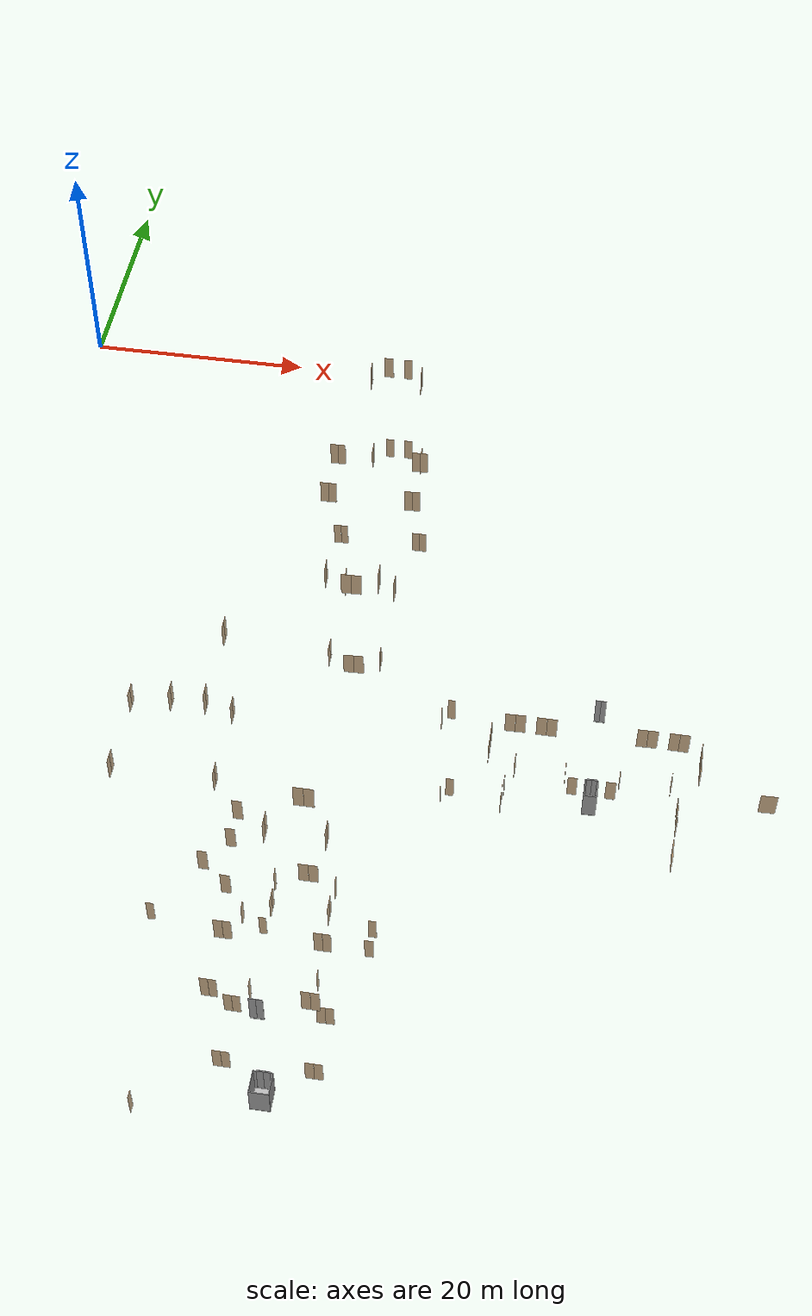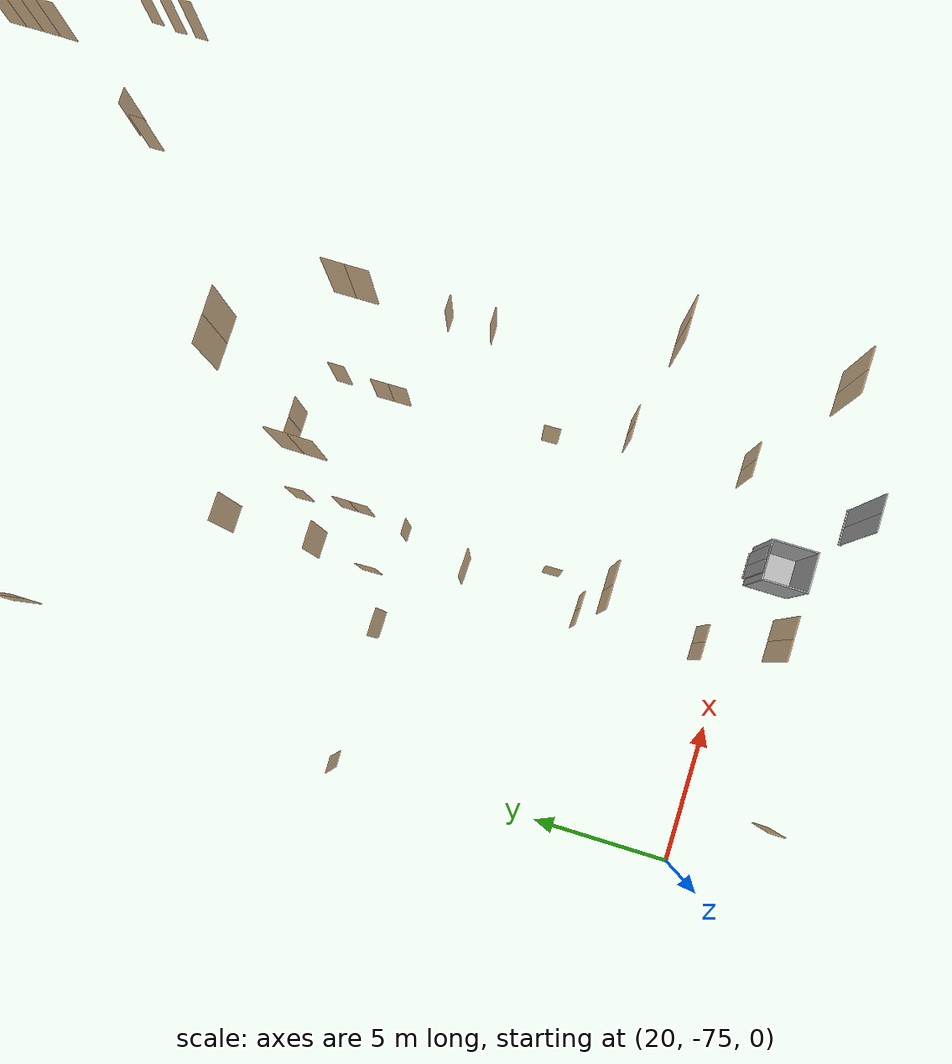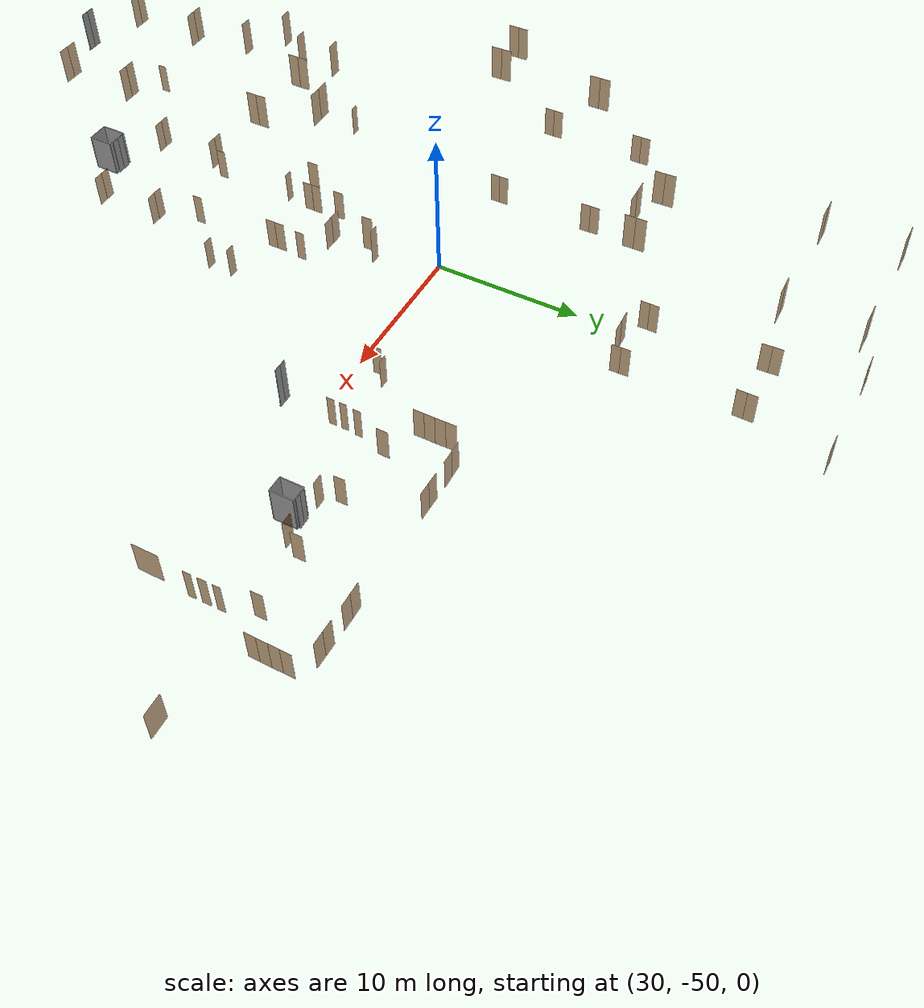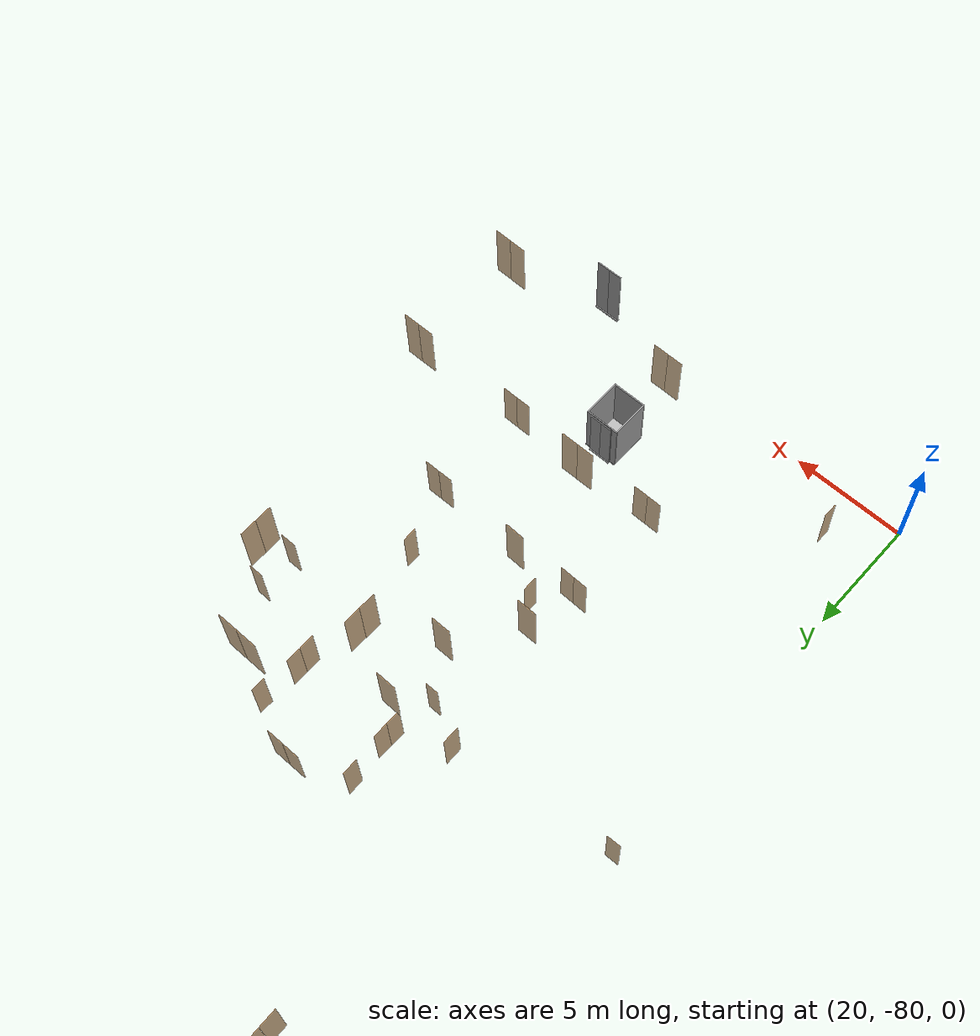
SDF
<sdf version="1.7">
 <world name="sim_world">
  <physics name="10ms" type="ode">
   <max_step_size>0.01</max_step_size>
   <real_time_factor>1.0</real_time_factor>
  </physics>
  <plugin filename="libgz-sim-physics-system.so" name="gz::sim::systems::Physics"/>
  <plugin filename="libgz-sim-user-commands-system.so" name="gz::sim::systems::UserCommands"/>
  <plugin filename="libgz-sim-scene-broadcaster-system.so" name="gz::sim::systems::SceneBroadcaster"/>
  <plugin filename="libdoor.so" name="door"/>
  <plugin filename="liblift.so" name="lift"/>
  <scene><ambient>1 1 1</ambient><background>0.8 0.8 0.8</background><grid>false</grid></scene>
  <light type="directional" name="sun">
   <pose>0 0 10 0 0 0</pose>
   <diffuse>1 1 1 1</diffuse>
   <specular>0.2 0.2 0.2 1</specular>
   <attenuation>
    <range>1000</range>
    <constant>0.09</constant>
    <linear>0.001</linear>
    <quadratic>0.001</quadratic>
   </attenuation>
   <direction>-0.5 0.1 -0.9</direction>
  </light>
  <model name="door3">
   <pose>27.847318445650217 -73.7472066650835 0.0 0 0 3.1348896198746576</pose>
   <link name="right">
    <pose>0.3232117227131276 0 1.11 0 0 0</pose>
    <visual name="right_visual">
     <geometry><box><size>0.6364234454262552 0.03 2.2</size></box></geometry>
     <material>
      <ambient>0.5 0.25 0 0.6</ambient>
      <diffuse>0.5 0.25 0 0.6</diffuse>
      <pbr><metal><metalness>0.0</metalness></metal></pbr>
     </material>
    </visual>
    <collision name="right_collision">
     <geometry><box><size>0.6364234454262552 0.03 2.2</size></box></geometry>
     <surface><contact><collide_bitmask>0x02</collide_bitmask></contact></surface>
    </collision>
    <inertial>
     <mass>50.0</mass>
     <inertia><ixx>20.17041666666667</ixx><iyy>21.85431167453428</iyy><izz>1.6913950078676068</izz></inertia>
    </inertial>
   </link>
   <joint name="right_joint" type="revolute">
    <parent>world</parent>
    <child>right</child>
    <axis><xyz>0 0 1</xyz><limit><lower>0</lower><upper>1.57</upper></limit></axis>
    <pose>0.3232117227131276 0 0 0 0 0</pose>
   </joint>
   <link name="left">
    <pose>-0.3232117227131276 0 1.11 0 0 0</pose>
    <visual name="left_visual">
     <geometry><box><size>0.6364234454262552 0.03 2.2</size></box></geometry>
     <material>
      <ambient>0.5 0.25 0 0.6</ambient>
      <diffuse>0.5 0.25 0 0.6</diffuse>
      <pbr><metal><metalness>0.0</metalness></metal></pbr>
     </material>
    </visual>
    <collision name="left_collision">
     <geometry><box><size>0.6364234454262552 0.03 2.2</size></box></geometry>
     <surface><contact><collide_bitmask>0x02</collide_bitmask></contact></surface>
    </collision>
    <inertial>
     <mass>50.0</mass>
     <inertia><ixx>20.17041666666667</ixx><iyy>21.85431167453428</iyy><izz>1.6913950078676068</izz></inertia>
    </inertial>
   </link>
   <joint name="left_joint" type="revolute">
    <parent>world</parent>
    <child>left</child>
    <axis><xyz>0 0 1</xyz><limit><lower>-1.57</lower><upper>0</upper></limit></axis>
    <pose>-0.3232117227131276 0 0 0 0 0</pose>
   </joint>
   <plugin name="register_component" filename="libregister_component.so">
    <component name="Door">
     <v_max_door>0.5</v_max_door>
     <a_max_door>0.3</a_max_door>
     <a_nom_door>0.15</a_nom_door>
     <dx_min_door>0.01</dx_min_door>
     <f_max_door>500.0</f_max_door>
     <ros_interface>true</ros_interface>
     <door name="door3" type="DoubleSwingDoor" left_joint_name="left_joint" right_joint_name="right_joint"/>
    </component>
   </plugin>
  </model>
  <model name="door2">
   <pose>22.211782101604086 -77.9055350099353 0.0 0 0 1.5613574322392048</pose>
   <link name="right">
    <pose>0 0 1.11 0 0 0</pose>
    <visual name="right_visual">
     <geometry><box><size>0.6194818811056692 0.03 2.2</size></box></geometry>
     <material>
      <ambient>0.5 0.25 0 0.6</ambient>
      <diffuse>0.5 0.25 0 0.6</diffuse>
      <pbr><metal><metalness>0.0</metalness></metal></pbr>
     </material>
    </visual>
    <collision name="right_collision">
     <geometry><box><size>0.6194818811056692 0.03 2.2</size></box></geometry>
     <surface><contact><collide_bitmask>0x02</collide_bitmask></contact></surface>
    </collision>
    <inertial>
     <mass>50.0</mass>
     <inertia><ixx>20.17041666666667</ixx><iyy>21.76565750424258</iyy><izz>1.6027408375759102</izz></inertia>
    </inertial>
   </link>
   <joint name="right_joint" type="revolute">
    <parent>world</parent>
    <child>right</child>
    <axis><xyz>0 0 -1</xyz><limit><lower>0</lower><upper>1.57</upper></limit></axis>
    <pose>0.3147409405528346 0 0 0 0 0</pose>
   </joint>
   <plugin name="register_component" filename="libregister_component.so">
    <component name="Door">
     <v_max_door>0.5</v_max_door>
     <a_max_door>0.3</a_max_door>
     <a_nom_door>0.15</a_nom_door>
     <dx_min_door>0.01</dx_min_door>
     <f_max_door>500.0</f_max_door>
     <ros_interface>true</ros_interface>
     <door name="door2" type="SwingDoor" left_joint_name="empty_joint" right_joint_name="right_joint"/>
    </component>
   </plugin>
  </model>
  <model name="door4">
   <pose>27.7079244754704 -69.25606597808076 0.0 0 0 3.119050205000111</pose>
   <link name="right">
    <pose>0.3175972304814701 0 1.11 0 0 0</pose>
    <visual name="right_visual">
     <geometry><box><size>0.6251944609629402 0.03 2.2</size></box></geometry>
     <material>
      <ambient>0.5 0.25 0 0.6</ambient>
      <diffuse>0.5 0.25 0 0.6</diffuse>
      <pbr><metal><metalness>0.0</metalness></metal></pbr>
     </material>
    </visual>
    <collision name="right_collision">
     <geometry><box><size>0.6251944609629402 0.03 2.2</size></box></geometry>
     <surface><contact><collide_bitmask>0x02</collide_bitmask></contact></surface>
    </collision>
    <inertial>
     <mass>50.0</mass>
     <inertia><ixx>20.17041666666667</ixx><iyy>21.795283808411426</iyy><izz>1.6323671417447556</izz></inertia>
    </inertial>
   </link>
   <joint name="right_joint" type="revolute">
    <parent>world</parent>
    <child>right</child>
    <axis><xyz>0 0 -1</xyz><limit><lower>0</lower><upper>1.57</upper></limit></axis>
    <pose>0.3175972304814701 0 0 0 0 0</pose>
   </joint>
   <link name="left">
    <pose>-0.3175972304814701 0 1.11 0 0 0</pose>
    <visual name="left_visual">
     <geometry><box><size>0.6251944609629402 0.03 2.2</size></box></geometry>
     <material>
      <ambient>0.5 0.25 0 0.6</ambient>
      <diffuse>0.5 0.25 0 0.6</diffuse>
      <pbr><metal><metalness>0.0</metalness></metal></pbr>
     </material>
    </visual>
    <collision name="left_collision">
     <geometry><box><size>0.6251944609629402 0.03 2.2</size></box></geometry>
     <surface><contact><collide_bitmask>0x02</collide_bitmask></contact></surface>
    </collision>
    <inertial>
     <mass>50.0</mass>
     <inertia><ixx>20.17041666666667</ixx><iyy>21.795283808411426</iyy><izz>1.6323671417447556</izz></inertia>
    </inertial>
   </link>
   <joint name="left_joint" type="revolute">
    <parent>world</parent>
    <child>left</child>
    <axis><xyz>0 0 -1</xyz><limit><lower>-1.57</lower><upper>0</upper></limit></axis>
    <pose>-0.3175972304814701 0 0 0 0 0</pose>
   </joint>
   <plugin name="register_component" filename="libregister_component.so">
    <component name="Door">
     <v_max_door>0.5</v_max_door>
     <a_max_door>0.3</a_max_door>
     <a_nom_door>0.15</a_nom_door>
     <dx_min_door>0.01</dx_min_door>
     <f_max_door>500.0</f_max_door>
     <ros_interface>true</ros_interface>
     <door name="door4" type="DoubleSwingDoor" left_joint_name="left_joint" right_joint_name="right_joint"/>
    </component>
   </plugin>
  </model>
  <model name="door6">
   <pose>28.772399377181465 -67.984536180234 0.0 0 0 1.589006458082369</pose>
   <link name="right">
    <pose>0 0 1.11 0 0 0</pose>
    <visual name="right_visual">
     <geometry><box><size>0.633037573122654 0.03 2.2</size></box></geometry>
     <material>
      <ambient>0.5 0.25 0 0.6</ambient>
      <diffuse>0.5 0.25 0 0.6</diffuse>
      <pbr><metal><metalness>0.0</metalness></metal></pbr>
     </material>
    </visual>
    <collision name="right_collision">
     <geometry><box><size>0.633037573122654 0.03 2.2</size></box></geometry>
     <surface><contact><collide_bitmask>0x02</collide_bitmask></contact></surface>
    </collision>
    <inertial>
     <mass>50.0</mass>
     <inertia><ixx>20.17041666666667</ixx><iyy>21.83640237077092</iyy><izz>1.673485704104248</izz></inertia>
    </inertial>
   </link>
   <joint name="right_joint" type="revolute">
    <parent>world</parent>
    <child>right</child>
    <axis><xyz>0 0 -1</xyz><limit><lower>0</lower><upper>1.57</upper></limit></axis>
    <pose>0.321518786561327 0 0 0 0 0</pose>
   </joint>
   <plugin name="register_component" filename="libregister_component.so">
    <component name="Door">
     <v_max_door>0.5</v_max_door>
     <a_max_door>0.3</a_max_door>
     <a_nom_door>0.15</a_nom_door>
     <dx_min_door>0.01</dx_min_door>
     <f_max_door>500.0</f_max_door>
     <ros_interface>true</ros_interface>
     <door name="door6" type="SwingDoor" left_joint_name="empty_joint" right_joint_name="right_joint"/>
    </component>
   </plugin>
  </model>
  <model name="door7">
   <pose>20.006505440822856 -62.49707422929499 0.0 0 0 -3.117601081888637</pose>
   <link name="right">
    <pose>0 0 1.11 0 0 0</pose>
    <visual name="right_visual">
     <geometry><box><size>0.5964999086840153 0.03 2.2</size></box></geometry>
     <material>
      <ambient>0.5 0.25 0 0.6</ambient>
      <diffuse>0.5 0.25 0 0.6</diffuse>
      <pbr><metal><metalness>0.0</metalness></metal></pbr>
     </material>
    </visual>
    <collision name="right_collision">
     <geometry><box><size>0.5964999086840153 0.03 2.2</size></box></geometry>
     <surface><contact><collide_bitmask>0x02</collide_bitmask></contact></surface>
    </collision>
    <inertial>
     <mass>50.0</mass>
     <inertia><ixx>20.17041666666667</ixx><iyy>21.649217254416833</iyy><izz>1.4863005877501607</izz></inertia>
    </inertial>
   </link>
   <joint name="right_joint" type="revolute">
    <parent>world</parent>
    <child>right</child>
    <axis><xyz>0 0 -1</xyz><limit><lower>0</lower><upper>1.57</upper></limit></axis>
    <pose>0.30324995434200763 0 0 0 0 0</pose>
   </joint>
   <plugin name="register_component" filename="libregister_component.so">
    <component name="Door">
     <v_max_door>0.5</v_max_door>
     <a_max_door>0.3</a_max_door>
     <a_nom_door>0.15</a_nom_door>
     <dx_min_door>0.01</dx_min_door>
     <f_max_door>500.0</f_max_door>
     <ros_interface>true</ros_interface>
     <door name="door7" type="SwingDoor" left_joint_name="empty_joint" right_joint_name="right_joint"/>
    </component>
   </plugin>
  </model>
  <model name="door8">
   <pose>28.657583031850905 -62.48891550123477 0.0 0 0 -3.138557686043698</pose>
   <link name="right">
    <pose>0 0 1.11 0 0 0</pose>
    <visual name="right_visual">
     <geometry><box><size>0.5725329680564498 0.03 2.2</size></box></geometry>
     <material>
      <ambient>0.5 0.25 0 0.6</ambient>
      <diffuse>0.5 0.25 0 0.6</diffuse>
      <pbr><metal><metalness>0.0</metalness></metal></pbr>
     </material>
    </visual>
    <collision name="right_collision">
     <geometry><box><size>0.5725329680564498 0.03 2.2</size></box></geometry>
     <surface><contact><collide_bitmask>0x02</collide_bitmask></contact></surface>
    </collision>
    <inertial>
     <mass>50.0</mass>
     <inertia><ixx>20.17041666666667</ixx><iyy>21.5324749979647</iyy><izz>1.3695583312980326</izz></inertia>
    </inertial>
   </link>
   <joint name="right_joint" type="revolute">
    <parent>world</parent>
    <child>right</child>
    <axis><xyz>0 0 1</xyz><limit><lower>0</lower><upper>1.57</upper></limit></axis>
    <pose>0.2912664840282249 0 0 0 0 0</pose>
   </joint>
   <plugin name="register_component" filename="libregister_component.so">
    <component name="Door">
     <v_max_door>0.5</v_max_door>
     <a_max_door>0.3</a_max_door>
     <a_nom_door>0.15</a_nom_door>
     <dx_min_door>0.01</dx_min_door>
     <f_max_door>500.0</f_max_door>
     <ros_interface>true</ros_interface>
     <door name="door8" type="SwingDoor" left_joint_name="empty_joint" right_joint_name="right_joint"/>
    </component>
   </plugin>
  </model>
  <model name="door11">
   <pose>26.91586124352129 -61.62542354706751 0.0 0 0 1.590140119046647</pose>
   <link name="right">
    <pose>0 0 1.11 0 0 0</pose>
    <visual name="right_visual">
     <geometry><box><size>0.748193471785033 0.03 2.2</size></box></geometry>
     <material>
      <ambient>0.5 0.25 0 0.6</ambient>
      <diffuse>0.5 0.25 0 0.6</diffuse>
      <pbr><metal><metalness>0.0</metalness></metal></pbr>
     </material>
    </visual>
    <collision name="right_collision">
     <geometry><box><size>0.748193471785033 0.03 2.2</size></box></geometry>
     <surface><contact><collide_bitmask>0x02</collide_bitmask></contact></surface>
    </collision>
    <inertial>
     <mass>50.0</mass>
     <inertia><ixx>20.17041666666667</ixx><iyy>22.499139463423923</iyy><izz>2.3362227967572546</izz></inertia>
    </inertial>
   </link>
   <joint name="right_joint" type="revolute">
    <parent>world</parent>
    <child>right</child>
    <axis><xyz>0 0 1</xyz><limit><lower>0</lower><upper>1.57</upper></limit></axis>
    <pose>0.3790967358925165 0 0 0 0 0</pose>
   </joint>
   <plugin name="register_component" filename="libregister_component.so">
    <component name="Door">
     <v_max_door>0.5</v_max_door>
     <a_max_door>0.3</a_max_door>
     <a_nom_door>0.15</a_nom_door>
     <dx_min_door>0.01</dx_min_door>
     <f_max_door>500.0</f_max_door>
     <ros_interface>true</ros_interface>
     <door name="door11" type="SwingDoor" left_joint_name="empty_joint" right_joint_name="right_joint"/>
    </component>
   </plugin>
  </model>
  <model name="door12">
   <pose>28.935081226566922 -60.41372925217037 0.0 0 0 1.569960739769453</pose>
   <link name="right">
    <pose>0.3295156354562787 0 1.11 0 0 0</pose>
    <visual name="right_visual">
     <geometry><box><size>0.6490312709125574 0.03 2.2</size></box></geometry>
     <material>
      <ambient>0.5 0.25 0 0.6</ambient>
      <diffuse>0.5 0.25 0 0.6</diffuse>
      <pbr><metal><metalness>0.0</metalness></metal></pbr>
     </material>
    </visual>
    <collision name="right_collision">
     <geometry><box><size>0.6490312709125574 0.03 2.2</size></box></geometry>
     <surface><contact><collide_bitmask>0x02</collide_bitmask></contact></surface>
    </collision>
    <inertial>
     <mass>50.0</mass>
     <inertia><ixx>20.17041666666667</ixx><iyy>21.921839960926548</iyy><izz>1.7589232942598731</izz></inertia>
    </inertial>
   </link>
   <joint name="right_joint" type="revolute">
    <parent>world</parent>
    <child>right</child>
    <axis><xyz>0 0 1</xyz><limit><lower>0</lower><upper>1.57</upper></limit></axis>
    <pose>0.3295156354562787 0 0 0 0 0</pose>
   </joint>
   <link name="left">
    <pose>-0.3295156354562787 0 1.11 0 0 0</pose>
    <visual name="left_visual">
     <geometry><box><size>0.6490312709125574 0.03 2.2</size></box></geometry>
     <material>
      <ambient>0.5 0.25 0 0.6</ambient>
      <diffuse>0.5 0.25 0 0.6</diffuse>
      <pbr><metal><metalness>0.0</metalness></metal></pbr>
     </material>
    </visual>
    <collision name="left_collision">
     <geometry><box><size>0.6490312709125574 0.03 2.2</size></box></geometry>
     <surface><contact><collide_bitmask>0x02</collide_bitmask></contact></surface>
    </collision>
    <inertial>
     <mass>50.0</mass>
     <inertia><ixx>20.17041666666667</ixx><iyy>21.921839960926548</iyy><izz>1.7589232942598731</izz></inertia>
    </inertial>
   </link>
   <joint name="left_joint" type="revolute">
    <parent>world</parent>
    <child>left</child>
    <axis><xyz>0 0 1</xyz><limit><lower>-1.57</lower><upper>0</upper></limit></axis>
    <pose>-0.3295156354562787 0 0 0 0 0</pose>
   </joint>
   <plugin name="register_component" filename="libregister_component.so">
    <component name="Door">
     <v_max_door>0.5</v_max_door>
     <a_max_door>0.3</a_max_door>
     <a_nom_door>0.15</a_nom_door>
     <dx_min_door>0.01</dx_min_door>
     <f_max_door>500.0</f_max_door>
     <ros_interface>true</ros_interface>
     <door name="door12" type="DoubleSwingDoor" left_joint_name="left_joint" right_joint_name="right_joint"/>
    </component>
   </plugin>
  </model>
  <model name="door14">
   <pose>28.795455392001728 -58.3927413031863 0.0 0 0 1.6107948883778462</pose>
   <link name="right">
    <pose>0 0 1.11 0 0 0</pose>
    <visual name="right_visual">
     <geometry><box><size>0.6894276678556776 0.03 2.2</size></box></geometry>
     <material>
      <ambient>0.5 0.25 0 0.6</ambient>
      <diffuse>0.5 0.25 0 0.6</diffuse>
      <pbr><metal><metalness>0.0</metalness></metal></pbr>
     </material>
    </visual>
    <collision name="right_collision">
     <geometry><box><size>0.6894276678556776 0.03 2.2</size></box></geometry>
     <surface><contact><collide_bitmask>0x02</collide_bitmask></contact></surface>
    </collision>
    <inertial>
     <mass>50.0</mass>
     <inertia><ixx>20.17041666666667</ixx><iyy>22.147127121687166</iyy><izz>1.9842104550204938</izz></inertia>
    </inertial>
   </link>
   <joint name="right_joint" type="revolute">
    <parent>world</parent>
    <child>right</child>
    <axis><xyz>0 0 1</xyz><limit><lower>0</lower><upper>1.57</upper></limit></axis>
    <pose>0.3497138339278388 0 0 0 0 0</pose>
   </joint>
   <plugin name="register_component" filename="libregister_component.so">
    <component name="Door">
     <v_max_door>0.5</v_max_door>
     <a_max_door>0.3</a_max_door>
     <a_nom_door>0.15</a_nom_door>
     <dx_min_door>0.01</dx_min_door>
     <f_max_door>500.0</f_max_door>
     <ros_interface>true</ros_interface>
     <door name="door14" type="SwingDoor" left_joint_name="empty_joint" right_joint_name="right_joint"/>
    </component>
   </plugin>
  </model>
  <model name="door15">
   <pose>33.50102716089975 -58.43092646915197 0.0 0 0 1.5700952612900068</pose>
   <link name="right">
    <pose>0 0 1.11 0 0 0</pose>
    <visual name="right_visual">
     <geometry><box><size>0.6101214510655555 0.03 2.2</size></box></geometry>
     <material>
      <ambient>0.5 0.25 0 0.6</ambient>
      <diffuse>0.5 0.25 0 0.6</diffuse>
      <pbr><metal><metalness>0.0</metalness></metal></pbr>
     </material>
    </visual>
    <collision name="right_collision">
     <geometry><box><size>0.6101214510655555 0.03 2.2</size></box></geometry>
     <surface><contact><collide_bitmask>0x02</collide_bitmask></contact></surface>
    </collision>
    <inertial>
     <mass>50.0</mass>
     <inertia><ixx>20.17041666666667</ixx><iyy>21.717700771043084</iyy><izz>1.5547841043764128</izz></inertia>
    </inertial>
   </link>
   <joint name="right_joint" type="revolute">
    <parent>world</parent>
    <child>right</child>
    <axis><xyz>0 0 -1</xyz><limit><lower>0</lower><upper>1.57</upper></limit></axis>
    <pose>0.31006072553277775 0 0 0 0 0</pose>
   </joint>
   <plugin name="register_component" filename="libregister_component.so">
    <component name="Door">
     <v_max_door>0.5</v_max_door>
     <a_max_door>0.3</a_max_door>
     <a_nom_door>0.15</a_nom_door>
     <dx_min_door>0.01</dx_min_door>
     <f_max_door>500.0</f_max_door>
     <ros_interface>true</ros_interface>
     <door name="door15" type="SwingDoor" left_joint_name="empty_joint" right_joint_name="right_joint"/>
    </component>
   </plugin>
  </model>
  <model name="door13">
   <pose>33.36353158037515 -60.44103128354773 0.0 0 0 1.5796133810395057</pose>
   <link name="right">
    <pose>0.3377598348170645 0 1.11 0 0 0</pose>
    <visual name="right_visual">
     <geometry><box><size>0.665519669634129 0.03 2.2</size></box></geometry>
     <material>
      <ambient>0.5 0.25 0 0.6</ambient>
      <diffuse>0.5 0.25 0 0.6</diffuse>
      <pbr><metal><metalness>0.0</metalness></metal></pbr>
     </material>
    </visual>
    <collision name="right_collision">
     <geometry><box><size>0.665519669634129 0.03 2.2</size></box></geometry>
     <surface><contact><collide_bitmask>0x02</collide_bitmask></contact></surface>
    </collision>
    <inertial>
     <mass>50.0</mass>
     <inertia><ixx>20.17041666666667</ixx><iyy>22.012151794458006</iyy><izz>1.8492351277913344</izz></inertia>
    </inertial>
   </link>
   <joint name="right_joint" type="revolute">
    <parent>world</parent>
    <child>right</child>
    <axis><xyz>0 0 -1</xyz><limit><lower>0</lower><upper>1.57</upper></limit></axis>
    <pose>0.3377598348170645 0 0 0 0 0</pose>
   </joint>
   <link name="left">
    <pose>-0.3377598348170645 0 1.11 0 0 0</pose>
    <visual name="left_visual">
     <geometry><box><size>0.665519669634129 0.03 2.2</size></box></geometry>
     <material>
      <ambient>0.5 0.25 0 0.6</ambient>
      <diffuse>0.5 0.25 0 0.6</diffuse>
      <pbr><metal><metalness>0.0</metalness></metal></pbr>
     </material>
    </visual>
    <collision name="left_collision">
     <geometry><box><size>0.665519669634129 0.03 2.2</size></box></geometry>
     <surface><contact><collide_bitmask>0x02</collide_bitmask></contact></surface>
    </collision>
    <inertial>
     <mass>50.0</mass>
     <inertia><ixx>20.17041666666667</ixx><iyy>22.012151794458006</iyy><izz>1.8492351277913344</izz></inertia>
    </inertial>
   </link>
   <joint name="left_joint" type="revolute">
    <parent>world</parent>
    <child>left</child>
    <axis><xyz>0 0 -1</xyz><limit><lower>-1.57</lower><upper>0</upper></limit></axis>
    <pose>-0.3377598348170645 0 0 0 0 0</pose>
   </joint>
   <plugin name="register_component" filename="libregister_component.so">
    <component name="Door">
     <v_max_door>0.5</v_max_door>
     <a_max_door>0.3</a_max_door>
     <a_nom_door>0.15</a_nom_door>
     <dx_min_door>0.01</dx_min_door>
     <f_max_door>500.0</f_max_door>
     <ros_interface>true</ros_interface>
     <door name="door13" type="DoubleSwingDoor" left_joint_name="left_joint" right_joint_name="right_joint"/>
    </component>
   </plugin>
  </model>
  <model name="door10">
   <pose>36.85043863129084 -61.591093126508625 0.0 0 0 3.113555789147109</pose>
   <link name="right">
    <pose>0 0 1.11 0 0 0</pose>
    <visual name="right_visual">
     <geometry><box><size>0.6248043392992916 0.03 2.2</size></box></geometry>
     <material>
      <ambient>0.5 0.25 0 0.6</ambient>
      <diffuse>0.5 0.25 0 0.6</diffuse>
      <pbr><metal><metalness>0.0</metalness></metal></pbr>
     </material>
    </visual>
    <collision name="right_collision">
     <geometry><box><size>0.6248043392992916 0.03 2.2</size></box></geometry>
     <surface><contact><collide_bitmask>0x02</collide_bitmask></contact></surface>
    </collision>
    <inertial>
     <mass>50.0</mass>
     <inertia><ixx>20.17041666666667</ixx><iyy>21.793251926696772</iyy><izz>1.6303352600301013</izz></inertia>
    </inertial>
   </link>
   <joint name="right_joint" type="revolute">
    <parent>world</parent>
    <child>right</child>
    <axis><xyz>0 0 -1</xyz><limit><lower>0</lower><upper>1.57</upper></limit></axis>
    <pose>0.3174021696496458 0 0 0 0 0</pose>
   </joint>
   <plugin name="register_component" filename="libregister_component.so">
    <component name="Door">
     <v_max_door>0.5</v_max_door>
     <a_max_door>0.3</a_max_door>
     <a_nom_door>0.15</a_nom_door>
     <dx_min_door>0.01</dx_min_door>
     <f_max_door>500.0</f_max_door>
     <ros_interface>true</ros_interface>
     <door name="door10" type="SwingDoor" left_joint_name="empty_joint" right_joint_name="right_joint"/>
    </component>
   </plugin>
  </model>
  <model name="door9">
   <pose>36.86804583305491 -63.29764398588237 0.0 0 0 -3.137951533307667</pose>
   <link name="right">
    <pose>0 0 1.11 0 0 0</pose>
    <visual name="right_visual">
     <geometry><box><size>0.6745551525855924 0.03 2.2</size></box></geometry>
     <material>
      <ambient>0.5 0.25 0 0.6</ambient>
      <diffuse>0.5 0.25 0 0.6</diffuse>
      <pbr><metal><metalness>0.0</metalness></metal></pbr>
     </material>
    </visual>
    <collision name="right_collision">
     <geometry><box><size>0.6745551525855924 0.03 2.2</size></box></geometry>
     <surface><contact><collide_bitmask>0x02</collide_bitmask></contact></surface>
    </collision>
    <inertial>
     <mass>50.0</mass>
     <inertia><ixx>20.17041666666667</ixx><iyy>22.06260272449905</iyy><izz>1.8996860578323829</izz></inertia>
    </inertial>
   </link>
   <joint name="right_joint" type="revolute">
    <parent>world</parent>
    <child>right</child>
    <axis><xyz>0 0 1</xyz><limit><lower>0</lower><upper>1.57</upper></limit></axis>
    <pose>0.3422775762927962 0 0 0 0 0</pose>
   </joint>
   <plugin name="register_component" filename="libregister_component.so">
    <component name="Door">
     <v_max_door>0.5</v_max_door>
     <a_max_door>0.3</a_max_door>
     <a_nom_door>0.15</a_nom_door>
     <dx_min_door>0.01</dx_min_door>
     <f_max_door>500.0</f_max_door>
     <ros_interface>true</ros_interface>
     <door name="door9" type="SwingDoor" left_joint_name="empty_joint" right_joint_name="right_joint"/>
    </component>
   </plugin>
  </model>
  <model name="door5">
   <pose>34.623163836947604 -69.26018157092108 0.0 0 0 -3.1335801828914733</pose>
   <link name="right">
    <pose>0.3255552930399749 0 1.11 0 0 0</pose>
    <visual name="right_visual">
     <geometry><box><size>0.6411105860799498 0.03 2.2</size></box></geometry>
     <material>
      <ambient>0.5 0.25 0 0.6</ambient>
      <diffuse>0.5 0.25 0 0.6</diffuse>
      <pbr><metal><metalness>0.0</metalness></metal></pbr>
     </material>
    </visual>
    <collision name="right_collision">
     <geometry><box><size>0.6411105860799498 0.03 2.2</size></box></geometry>
     <surface><contact><collide_bitmask>0x02</collide_bitmask></contact></surface>
    </collision>
    <inertial>
     <mass>50.0</mass>
     <inertia><ixx>20.17041666666667</ixx><iyy>21.87926159826574</iyy><izz>1.7163449315990695</izz></inertia>
    </inertial>
   </link>
   <joint name="right_joint" type="revolute">
    <parent>world</parent>
    <child>right</child>
    <axis><xyz>0 0 -1</xyz><limit><lower>0</lower><upper>1.57</upper></limit></axis>
    <pose>0.3255552930399749 0 0 0 0 0</pose>
   </joint>
   <link name="left">
    <pose>-0.3255552930399749 0 1.11 0 0 0</pose>
    <visual name="left_visual">
     <geometry><box><size>0.6411105860799498 0.03 2.2</size></box></geometry>
     <material>
      <ambient>0.5 0.25 0 0.6</ambient>
      <diffuse>0.5 0.25 0 0.6</diffuse>
      <pbr><metal><metalness>0.0</metalness></metal></pbr>
     </material>
    </visual>
    <collision name="left_collision">
     <geometry><box><size>0.6411105860799498 0.03 2.2</size></box></geometry>
     <surface><contact><collide_bitmask>0x02</collide_bitmask></contact></surface>
    </collision>
    <inertial>
     <mass>50.0</mass>
     <inertia><ixx>20.17041666666667</ixx><iyy>21.87926159826574</iyy><izz>1.7163449315990695</izz></inertia>
    </inertial>
   </link>
   <joint name="left_joint" type="revolute">
    <parent>world</parent>
    <child>left</child>
    <axis><xyz>0 0 -1</xyz><limit><lower>-1.57</lower><upper>0</upper></limit></axis>
    <pose>-0.3255552930399749 0 0 0 0 0</pose>
   </joint>
   <plugin name="register_component" filename="libregister_component.so">
    <component name="Door">
     <v_max_door>0.5</v_max_door>
     <a_max_door>0.3</a_max_door>
     <a_nom_door>0.15</a_nom_door>
     <dx_min_door>0.01</dx_min_door>
     <f_max_door>500.0</f_max_door>
     <ros_interface>true</ros_interface>
     <door name="door5" type="DoubleSwingDoor" left_joint_name="left_joint" right_joint_name="right_joint"/>
    </component>
   </plugin>
  </model>
  <model name="door1">
   <pose>34.58638434881824 -73.73664234402506 0.0 0 0 3.135840957718924</pose>
   <link name="right">
    <pose>0.3325787331740694 0 1.11 0 0 0</pose>
    <visual name="right_visual">
     <geometry><box><size>0.6551574663481388 0.03 2.2</size></box></geometry>
     <material>
      <ambient>0.5 0.25 0 0.6</ambient>
      <diffuse>0.5 0.25 0 0.6</diffuse>
      <pbr><metal><metalness>0.0</metalness></metal></pbr>
     </material>
    </visual>
    <collision name="right_collision">
     <geometry><box><size>0.6551574663481388 0.03 2.2</size></box></geometry>
     <surface><contact><collide_bitmask>0x02</collide_bitmask></contact></surface>
    </collision>
    <inertial>
     <mass>50.0</mass>
     <inertia><ixx>20.17041666666667</ixx><iyy>21.955130440465474</iyy><izz>1.7922137737988026</izz></inertia>
    </inertial>
   </link>
   <joint name="right_joint" type="revolute">
    <parent>world</parent>
    <child>right</child>
    <axis><xyz>0 0 1</xyz><limit><lower>0</lower><upper>1.57</upper></limit></axis>
    <pose>0.3325787331740694 0 0 0 0 0</pose>
   </joint>
   <link name="left">
    <pose>-0.3325787331740694 0 1.11 0 0 0</pose>
    <visual name="left_visual">
     <geometry><box><size>0.6551574663481388 0.03 2.2</size></box></geometry>
     <material>
      <ambient>0.5 0.25 0 0.6</ambient>
      <diffuse>0.5 0.25 0 0.6</diffuse>
      <pbr><metal><metalness>0.0</metalness></metal></pbr>
     </material>
    </visual>
    <collision name="left_collision">
     <geometry><box><size>0.6551574663481388 0.03 2.2</size></box></geometry>
     <surface><contact><collide_bitmask>0x02</collide_bitmask></contact></surface>
    </collision>
    <inertial>
     <mass>50.0</mass>
     <inertia><ixx>20.17041666666667</ixx><iyy>21.955130440465474</iyy><izz>1.7922137737988026</izz></inertia>
    </inertial>
   </link>
   <joint name="left_joint" type="revolute">
    <parent>world</parent>
    <child>left</child>
    <axis><xyz>0 0 1</xyz><limit><lower>-1.57</lower><upper>0</upper></limit></axis>
    <pose>-0.3325787331740694 0 0 0 0 0</pose>
   </joint>
   <plugin name="register_component" filename="libregister_component.so">
    <component name="Door">
     <v_max_door>0.5</v_max_door>
     <a_max_door>0.3</a_max_door>
     <a_nom_door>0.15</a_nom_door>
     <dx_min_door>0.01</dx_min_door>
     <f_max_door>500.0</f_max_door>
     <ros_interface>true</ros_interface>
     <door name="door1" type="DoubleSwingDoor" left_joint_name="left_joint" right_joint_name="right_joint"/>
    </component>
   </plugin>
  </model>
  <model name="door16">
   <pose>33.572832662744126 -66.50612538454055 0.0 0 0 1.5991199512423215</pose>
   <link name="right">
    <pose>0 0 1.11 0 0 0</pose>
    <visual name="right_visual">
     <geometry><box><size>0.6245195237357324 0.03 2.2</size></box></geometry>
     <material>
      <ambient>0.5 0.25 0 0.6</ambient>
      <diffuse>0.5 0.25 0 0.6</diffuse>
      <pbr><metal><metalness>0.0</metalness></metal></pbr>
     </material>
    </visual>
    <collision name="right_collision">
     <geometry><box><size>0.6245195237357324 0.03 2.2</size></box></geometry>
     <surface><contact><collide_bitmask>0x02</collide_bitmask></contact></surface>
    </collision>
    <inertial>
     <mass>50.0</mass>
     <inertia><ixx>20.17041666666667</ixx><iyy>21.79176931469628</iyy><izz>1.6288526480296084</izz></inertia>
    </inertial>
   </link>
   <joint name="right_joint" type="revolute">
    <parent>world</parent>
    <child>right</child>
    <axis><xyz>0 0 1</xyz><limit><lower>0</lower><upper>1.57</upper></limit></axis>
    <pose>0.3172597618678662 0 0 0 0 0</pose>
   </joint>
   <plugin name="register_component" filename="libregister_component.so">
    <component name="Door">
     <v_max_door>0.5</v_max_door>
     <a_max_door>0.3</a_max_door>
     <a_nom_door>0.15</a_nom_door>
     <dx_min_door>0.01</dx_min_door>
     <f_max_door>500.0</f_max_door>
     <ros_interface>true</ros_interface>
     <door name="door16" type="SwingDoor" left_joint_name="empty_joint" right_joint_name="right_joint"/>
    </component>
   </plugin>
  </model>
  <model name="door20">
   <pose>22.196594984362328 -42.79629647210699 0.0 0 0 1.5841898704715496</pose>
   <link name="right">
    <pose>0.3262262213419995 0 1.11 0 0 0</pose>
    <visual name="right_visual">
     <geometry><box><size>0.642452442683999 0.03 2.2</size></box></geometry>
     <material>
      <ambient>0.5 0.25 0 0.6</ambient>
      <diffuse>0.5 0.25 0 0.6</diffuse>
      <pbr><metal><metalness>0.0</metalness></metal></pbr>
     </material>
    </visual>
    <collision name="right_collision">
     <geometry><box><size>0.642452442683999 0.03 2.2</size></box></geometry>
     <surface><contact><collide_bitmask>0x02</collide_bitmask></contact></surface>
    </collision>
    <inertial>
     <mass>50.0</mass>
     <inertia><ixx>20.17041666666667</ixx><iyy>21.886438087960993</iyy><izz>1.7235214212943213</izz></inertia>
    </inertial>
   </link>
   <joint name="right_joint" type="revolute">
    <parent>world</parent>
    <child>right</child>
    <axis><xyz>0 0 -1</xyz><limit><lower>0</lower><upper>1.57</upper></limit></axis>
    <pose>0.3262262213419995 0 0 0 0 0</pose>
   </joint>
   <link name="left">
    <pose>-0.3262262213419995 0 1.11 0 0 0</pose>
    <visual name="left_visual">
     <geometry><box><size>0.642452442683999 0.03 2.2</size></box></geometry>
     <material>
      <ambient>0.5 0.25 0 0.6</ambient>
      <diffuse>0.5 0.25 0 0.6</diffuse>
      <pbr><metal><metalness>0.0</metalness></metal></pbr>
     </material>
    </visual>
    <collision name="left_collision">
     <geometry><box><size>0.642452442683999 0.03 2.2</size></box></geometry>
     <surface><contact><collide_bitmask>0x02</collide_bitmask></contact></surface>
    </collision>
    <inertial>
     <mass>50.0</mass>
     <inertia><ixx>20.17041666666667</ixx><iyy>21.886438087960993</iyy><izz>1.7235214212943213</izz></inertia>
    </inertial>
   </link>
   <joint name="left_joint" type="revolute">
    <parent>world</parent>
    <child>left</child>
    <axis><xyz>0 0 -1</xyz><limit><lower>-1.57</lower><upper>0</upper></limit></axis>
    <pose>-0.3262262213419995 0 0 0 0 0</pose>
   </joint>
   <plugin name="register_component" filename="libregister_component.so">
    <component name="Door">
     <v_max_door>0.5</v_max_door>
     <a_max_door>0.3</a_max_door>
     <a_nom_door>0.15</a_nom_door>
     <dx_min_door>0.01</dx_min_door>
     <f_max_door>500.0</f_max_door>
     <ros_interface>true</ros_interface>
     <door name="door20" type="DoubleSwingDoor" left_joint_name="left_joint" right_joint_name="right_joint"/>
    </component>
   </plugin>
  </model>
  <model name="door21_end">
   <pose>22.19549362853182 -49.59114025148065 0.0 0 0 1.5724148541161638</pose>
   <link name="right">
    <pose>0.3178502598575547 0 1.11 0 0 0</pose>
    <visual name="right_visual">
     <geometry><box><size>0.6257005197151094 0.03 2.2</size></box></geometry>
     <material>
      <ambient>0.5 0.25 0 0.6</ambient>
      <diffuse>0.5 0.25 0 0.6</diffuse>
      <pbr><metal><metalness>0.0</metalness></metal></pbr>
     </material>
    </visual>
    <collision name="right_collision">
     <geometry><box><size>0.6257005197151094 0.03 2.2</size></box></geometry>
     <surface><contact><collide_bitmask>0x02</collide_bitmask></contact></surface>
    </collision>
    <inertial>
     <mass>50.0</mass>
     <inertia><ixx>20.17041666666667</ixx><iyy>21.79792141821566</iyy><izz>1.635004751548992</izz></inertia>
    </inertial>
   </link>
   <joint name="right_joint" type="revolute">
    <parent>world</parent>
    <child>right</child>
    <axis><xyz>0 0 -1</xyz><limit><lower>0</lower><upper>1.57</upper></limit></axis>
    <pose>0.3178502598575547 0 0 0 0 0</pose>
   </joint>
   <link name="left">
    <pose>-0.3178502598575547 0 1.11 0 0 0</pose>
    <visual name="left_visual">
     <geometry><box><size>0.6257005197151094 0.03 2.2</size></box></geometry>
     <material>
      <ambient>0.5 0.25 0 0.6</ambient>
      <diffuse>0.5 0.25 0 0.6</diffuse>
      <pbr><metal><metalness>0.0</metalness></metal></pbr>
     </material>
    </visual>
    <collision name="left_collision">
     <geometry><box><size>0.6257005197151094 0.03 2.2</size></box></geometry>
     <surface><contact><collide_bitmask>0x02</collide_bitmask></contact></surface>
    </collision>
    <inertial>
     <mass>50.0</mass>
     <inertia><ixx>20.17041666666667</ixx><iyy>21.79792141821566</iyy><izz>1.635004751548992</izz></inertia>
    </inertial>
   </link>
   <joint name="left_joint" type="revolute">
    <parent>world</parent>
    <child>left</child>
    <axis><xyz>0 0 -1</xyz><limit><lower>-1.57</lower><upper>0</upper></limit></axis>
    <pose>-0.3178502598575547 0 0 0 0 0</pose>
   </joint>
   <plugin name="register_component" filename="libregister_component.so">
    <component name="Door">
     <v_max_door>0.5</v_max_door>
     <a_max_door>0.3</a_max_door>
     <a_nom_door>0.15</a_nom_door>
     <dx_min_door>0.01</dx_min_door>
     <f_max_door>500.0</f_max_door>
     <ros_interface>true</ros_interface>
     <door name="door21_end" type="DoubleSwingDoor" left_joint_name="left_joint" right_joint_name="right_joint"/>
    </component>
   </plugin>
  </model>
  <model name="door19">
   <pose>13.633176622528351 -49.584706014786626 0.0 0 0 1.5709468288255375</pose>
   <link name="right">
    <pose>0.3370076421904802 0 1.11 0 0 0</pose>
    <visual name="right_visual">
     <geometry><box><size>0.6640152843809604 0.03 2.2</size></box></geometry>
     <material>
      <ambient>0.5 0.25 0 0.6</ambient>
      <diffuse>0.5 0.25 0 0.6</diffuse>
      <pbr><metal><metalness>0.0</metalness></metal></pbr>
     </material>
    </visual>
    <collision name="right_collision">
     <geometry><box><size>0.6640152843809604 0.03 2.2</size></box></geometry>
     <surface><contact><collide_bitmask>0x02</collide_bitmask></contact></surface>
    </collision>
    <inertial>
     <mass>50.0</mass>
     <inertia><ixx>20.17041666666667</ixx><iyy>22.00381790788137</iyy><izz>1.8409012412146988</izz></inertia>
    </inertial>
   </link>
   <joint name="right_joint" type="revolute">
    <parent>world</parent>
    <child>right</child>
    <axis><xyz>0 0 -1</xyz><limit><lower>0</lower><upper>1.57</upper></limit></axis>
    <pose>0.3370076421904802 0 0 0 0 0</pose>
   </joint>
   <link name="left">
    <pose>-0.3370076421904802 0 1.11 0 0 0</pose>
    <visual name="left_visual">
     <geometry><box><size>0.6640152843809604 0.03 2.2</size></box></geometry>
     <material>
      <ambient>0.5 0.25 0 0.6</ambient>
      <diffuse>0.5 0.25 0 0.6</diffuse>
      <pbr><metal><metalness>0.0</metalness></metal></pbr>
     </material>
    </visual>
    <collision name="left_collision">
     <geometry><box><size>0.6640152843809604 0.03 2.2</size></box></geometry>
     <surface><contact><collide_bitmask>0x02</collide_bitmask></contact></surface>
    </collision>
    <inertial>
     <mass>50.0</mass>
     <inertia><ixx>20.17041666666667</ixx><iyy>22.00381790788137</iyy><izz>1.8409012412146988</izz></inertia>
    </inertial>
   </link>
   <joint name="left_joint" type="revolute">
    <parent>world</parent>
    <child>left</child>
    <axis><xyz>0 0 -1</xyz><limit><lower>-1.57</lower><upper>0</upper></limit></axis>
    <pose>-0.3370076421904802 0 0 0 0 0</pose>
   </joint>
   <plugin name="register_component" filename="libregister_component.so">
    <component name="Door">
     <v_max_door>0.5</v_max_door>
     <a_max_door>0.3</a_max_door>
     <a_nom_door>0.15</a_nom_door>
     <dx_min_door>0.01</dx_min_door>
     <f_max_door>500.0</f_max_door>
     <ros_interface>true</ros_interface>
     <door name="door19" type="DoubleSwingDoor" left_joint_name="left_joint" right_joint_name="right_joint"/>
    </component>
   </plugin>
  </model>
  <model name="door18">
   <pose>13.645016197706322 -42.78745664241474 0.0 0 0 1.5759858748518023</pose>
   <link name="right">
    <pose>0.3323023677213366 0 1.11 0 0 0</pose>
    <visual name="right_visual">
     <geometry><box><size>0.6546047354426732 0.03 2.2</size></box></geometry>
     <material>
      <ambient>0.5 0.25 0 0.6</ambient>
      <diffuse>0.5 0.25 0 0.6</diffuse>
      <pbr><metal><metalness>0.0</metalness></metal></pbr>
     </material>
    </visual>
    <collision name="right_collision">
     <geometry><box><size>0.6546047354426732 0.03 2.2</size></box></geometry>
     <surface><contact><collide_bitmask>0x02</collide_bitmask></contact></surface>
    </collision>
    <inertial>
     <mass>50.0</mass>
     <inertia><ixx>20.17041666666667</ixx><iyy>21.952113998599888</iyy><izz>1.7891973319332173</izz></inertia>
    </inertial>
   </link>
   <joint name="right_joint" type="revolute">
    <parent>world</parent>
    <child>right</child>
    <axis><xyz>0 0 -1</xyz><limit><lower>0</lower><upper>1.57</upper></limit></axis>
    <pose>0.3323023677213366 0 0 0 0 0</pose>
   </joint>
   <link name="left">
    <pose>-0.3323023677213366 0 1.11 0 0 0</pose>
    <visual name="left_visual">
     <geometry><box><size>0.6546047354426732 0.03 2.2</size></box></geometry>
     <material>
      <ambient>0.5 0.25 0 0.6</ambient>
      <diffuse>0.5 0.25 0 0.6</diffuse>
      <pbr><metal><metalness>0.0</metalness></metal></pbr>
     </material>
    </visual>
    <collision name="left_collision">
     <geometry><box><size>0.6546047354426732 0.03 2.2</size></box></geometry>
     <surface><contact><collide_bitmask>0x02</collide_bitmask></contact></surface>
    </collision>
    <inertial>
     <mass>50.0</mass>
     <inertia><ixx>20.17041666666667</ixx><iyy>21.952113998599888</iyy><izz>1.7891973319332173</izz></inertia>
    </inertial>
   </link>
   <joint name="left_joint" type="revolute">
    <parent>world</parent>
    <child>left</child>
    <axis><xyz>0 0 -1</xyz><limit><lower>-1.57</lower><upper>0</upper></limit></axis>
    <pose>-0.3323023677213366 0 0 0 0 0</pose>
   </joint>
   <plugin name="register_component" filename="libregister_component.so">
    <component name="Door">
     <v_max_door>0.5</v_max_door>
     <a_max_door>0.3</a_max_door>
     <a_nom_door>0.15</a_nom_door>
     <dx_min_door>0.01</dx_min_door>
     <f_max_door>500.0</f_max_door>
     <ros_interface>true</ros_interface>
     <door name="door18" type="DoubleSwingDoor" left_joint_name="left_joint" right_joint_name="right_joint"/>
    </component>
   </plugin>
  </model>
  <model name="door22">
   <pose>40.84886749938164 -47.81650821195254 0.0 0 0 3.127897356564713</pose>
   <link name="right">
    <pose>0 0 1.11 0 0 0</pose>
    <visual name="right_visual">
     <geometry><box><size>0.631252110748588 0.03 2.2</size></box></geometry>
     <material>
      <ambient>0.5 0.25 0 0.6</ambient>
      <diffuse>0.5 0.25 0 0.6</diffuse>
      <pbr><metal><metalness>0.0</metalness></metal></pbr>
     </material>
    </visual>
    <collision name="right_collision">
     <geometry><box><size>0.631252110748588 0.03 2.2</size></box></geometry>
     <surface><contact><collide_bitmask>0x02</collide_bitmask></contact></surface>
    </collision>
    <inertial>
     <mass>50.0</mass>
     <inertia><ixx>20.17041666666667</ixx><iyy>21.826996780518954</iyy><izz>1.6640801138522818</izz></inertia>
    </inertial>
   </link>
   <joint name="right_joint" type="revolute">
    <parent>world</parent>
    <child>right</child>
    <axis><xyz>0 0 1</xyz><limit><lower>0</lower><upper>1.57</upper></limit></axis>
    <pose>0.320626055374294 0 0 0 0 0</pose>
   </joint>
   <plugin name="register_component" filename="libregister_component.so">
    <component name="Door">
     <v_max_door>0.5</v_max_door>
     <a_max_door>0.3</a_max_door>
     <a_nom_door>0.15</a_nom_door>
     <dx_min_door>0.01</dx_min_door>
     <f_max_door>500.0</f_max_door>
     <ros_interface>true</ros_interface>
     <door name="door22" type="SwingDoor" left_joint_name="empty_joint" right_joint_name="right_joint"/>
    </component>
   </plugin>
  </model>
  <model name="door23_end">
   <pose>40.216500862856336 -48.60354288504393 0.0 0 0 1.5856953258611415</pose>
   <link name="right">
    <pose>0 0 1.11 0 0 0</pose>
    <visual name="right_visual">
     <geometry><box><size>0.5891750900136934 0.03 2.2</size></box></geometry>
     <material>
      <ambient>0.5 0.25 0 0.6</ambient>
      <diffuse>0.5 0.25 0 0.6</diffuse>
      <pbr><metal><metalness>0.0</metalness></metal></pbr>
     </material>
    </visual>
    <collision name="right_collision">
     <geometry><box><size>0.5891750900136934 0.03 2.2</size></box></geometry>
     <surface><contact><collide_bitmask>0x02</collide_bitmask></contact></surface>
    </collision>
    <inertial>
     <mass>50.0</mass>
     <inertia><ixx>20.17041666666667</ixx><iyy>21.61303036121935</iyy><izz>1.4501136945526822</izz></inertia>
    </inertial>
   </link>
   <joint name="right_joint" type="revolute">
    <parent>world</parent>
    <child>right</child>
    <axis><xyz>0 0 1</xyz><limit><lower>0</lower><upper>1.57</upper></limit></axis>
    <pose>0.2995875450068467 0 0 0 0 0</pose>
   </joint>
   <plugin name="register_component" filename="libregister_component.so">
    <component name="Door">
     <v_max_door>0.5</v_max_door>
     <a_max_door>0.3</a_max_door>
     <a_nom_door>0.15</a_nom_door>
     <dx_min_door>0.01</dx_min_door>
     <f_max_door>500.0</f_max_door>
     <ros_interface>true</ros_interface>
     <door name="door23_end" type="SwingDoor" left_joint_name="empty_joint" right_joint_name="right_joint"/>
    </component>
   </plugin>
  </model>
  <model name="door24">
   <pose>30.37290126329647 -10.758362565942143 0.0 0 0 3.141592653589793</pose>
   <link name="right">
    <pose>0 0 1.11 0 0 0</pose>
    <visual name="right_visual">
     <geometry><box><size>0.7199090851457741 0.03 2.2</size></box></geometry>
     <material>
      <ambient>0.5 0.25 0 0.6</ambient>
      <diffuse>0.5 0.25 0 0.6</diffuse>
      <pbr><metal><metalness>0.0</metalness></metal></pbr>
     </material>
    </visual>
    <collision name="right_collision">
     <geometry><box><size>0.7199090851457741 0.03 2.2</size></box></geometry>
     <surface><contact><collide_bitmask>0x02</collide_bitmask></contact></surface>
    </collision>
    <inertial>
     <mass>50.0</mass>
     <inertia><ixx>20.17041666666667</ixx><iyy>22.326121211980944</iyy><izz>2.163204545314273</izz></inertia>
    </inertial>
   </link>
   <joint name="right_joint" type="revolute">
    <parent>world</parent>
    <child>right</child>
    <axis><xyz>0 0 1</xyz><limit><lower>0</lower><upper>1.57</upper></limit></axis>
    <pose>0.36495454257288706 0 0 0 0 0</pose>
   </joint>
   <plugin name="register_component" filename="libregister_component.so">
    <component name="Door">
     <v_max_door>0.5</v_max_door>
     <a_max_door>0.3</a_max_door>
     <a_nom_door>0.15</a_nom_door>
     <dx_min_door>0.01</dx_min_door>
     <f_max_door>500.0</f_max_door>
     <ros_interface>true</ros_interface>
     <door name="door24" type="SwingDoor" left_joint_name="empty_joint" right_joint_name="right_joint"/>
    </component>
   </plugin>
  </model>
  <model name="door25">
   <pose>32.063772293609546 -10.714148925956838 0.0 0 0 -3.136152313331386</pose>
   <link name="right">
    <pose>0 0 1.11 0 0 0</pose>
    <visual name="right_visual">
     <geometry><box><size>0.719861919994674 0.03 2.2</size></box></geometry>
     <material>
      <ambient>0.5 0.25 0 0.6</ambient>
      <diffuse>0.5 0.25 0 0.6</diffuse>
      <pbr><metal><metalness>0.0</metalness></metal></pbr>
     </material>
    </visual>
    <collision name="right_collision">
     <geometry><box><size>0.719861919994674 0.03 2.2</size></box></geometry>
     <surface><contact><collide_bitmask>0x02</collide_bitmask></contact></surface>
    </collision>
    <inertial>
     <mass>50.0</mass>
     <inertia><ixx>20.17041666666667</ixx><iyy>22.325838266076747</iyy><izz>2.162921599410077</izz></inertia>
    </inertial>
   </link>
   <joint name="right_joint" type="revolute">
    <parent>world</parent>
    <child>right</child>
    <axis><xyz>0 0 -1</xyz><limit><lower>0</lower><upper>1.57</upper></limit></axis>
    <pose>0.364930959997337 0 0 0 0 0</pose>
   </joint>
   <plugin name="register_component" filename="libregister_component.so">
    <component name="Door">
     <v_max_door>0.5</v_max_door>
     <a_max_door>0.3</a_max_door>
     <a_nom_door>0.15</a_nom_door>
     <dx_min_door>0.01</dx_min_door>
     <f_max_door>500.0</f_max_door>
     <ros_interface>true</ros_interface>
     <door name="door25" type="SwingDoor" left_joint_name="empty_joint" right_joint_name="right_joint"/>
    </component>
   </plugin>
  </model>
  <model name="door26">
   <pose>28.98413503559683 -12.066034224858509 0.0 0 0 1.599630185866512</pose>
   <link name="right">
    <pose>0.30787722562131326 0 1.11 0 0 0</pose>
    <visual name="right_visual">
     <geometry><box><size>0.6057544512426265 0.03 2.2</size></box></geometry>
     <material>
      <ambient>0.5 0.25 0 0.6</ambient>
      <diffuse>0.5 0.25 0 0.6</diffuse>
      <pbr><metal><metalness>0.0</metalness></metal></pbr>
     </material>
    </visual>
    <collision name="right_collision">
     <geometry><box><size>0.6057544512426265 0.03 2.2</size></box></geometry>
     <surface><contact><collide_bitmask>0x02</collide_bitmask></contact></surface>
    </collision>
    <inertial>
     <mass>50.0</mass>
     <inertia><ixx>20.17041666666667</ixx><iyy>21.695576896667735</iyy><izz>1.532660230001065</izz></inertia>
    </inertial>
   </link>
   <joint name="right_joint" type="revolute">
    <parent>world</parent>
    <child>right</child>
    <axis><xyz>0 0 1</xyz><limit><lower>0</lower><upper>1.57</upper></limit></axis>
    <pose>0.30787722562131326 0 0 0 0 0</pose>
   </joint>
   <link name="left">
    <pose>-0.30787722562131326 0 1.11 0 0 0</pose>
    <visual name="left_visual">
     <geometry><box><size>0.6057544512426265 0.03 2.2</size></box></geometry>
     <material>
      <ambient>0.5 0.25 0 0.6</ambient>
      <diffuse>0.5 0.25 0 0.6</diffuse>
      <pbr><metal><metalness>0.0</metalness></metal></pbr>
     </material>
    </visual>
    <collision name="left_collision">
     <geometry><box><size>0.6057544512426265 0.03 2.2</size></box></geometry>
     <surface><contact><collide_bitmask>0x02</collide_bitmask></contact></surface>
    </collision>
    <inertial>
     <mass>50.0</mass>
     <inertia><ixx>20.17041666666667</ixx><iyy>21.695576896667735</iyy><izz>1.532660230001065</izz></inertia>
    </inertial>
   </link>
   <joint name="left_joint" type="revolute">
    <parent>world</parent>
    <child>left</child>
    <axis><xyz>0 0 1</xyz><limit><lower>-1.57</lower><upper>0</upper></limit></axis>
    <pose>-0.30787722562131326 0 0 0 0 0</pose>
   </joint>
   <plugin name="register_component" filename="libregister_component.so">
    <component name="Door">
     <v_max_door>0.5</v_max_door>
     <a_max_door>0.3</a_max_door>
     <a_nom_door>0.15</a_nom_door>
     <dx_min_door>0.01</dx_min_door>
     <f_max_door>500.0</f_max_door>
     <ros_interface>true</ros_interface>
     <door name="door26" type="DoubleSwingDoor" left_joint_name="left_joint" right_joint_name="right_joint"/>
    </component>
   </plugin>
  </model>
  <model name="door27">
   <pose>33.441785810437636 -12.070729478662258 0.0 0 0 1.587504132487737</pose>
   <link name="right">
    <pose>0.3083574587941471 0 1.11 0 0 0</pose>
    <visual name="right_visual">
     <geometry><box><size>0.6067149175882942 0.03 2.2</size></box></geometry>
     <material>
      <ambient>0.5 0.25 0 0.6</ambient>
      <diffuse>0.5 0.25 0 0.6</diffuse>
      <pbr><metal><metalness>0.0</metalness></metal></pbr>
     </material>
    </visual>
    <collision name="right_collision">
     <geometry><box><size>0.6067149175882942 0.03 2.2</size></box></geometry>
     <surface><contact><collide_bitmask>0x02</collide_bitmask></contact></surface>
    </collision>
    <inertial>
     <mass>50.0</mass>
     <inertia><ixx>20.17041666666667</ixx><iyy>21.700429130100716</iyy><izz>1.5375124634340445</izz></inertia>
    </inertial>
   </link>
   <joint name="right_joint" type="revolute">
    <parent>world</parent>
    <child>right</child>
    <axis><xyz>0 0 -1</xyz><limit><lower>0</lower><upper>1.57</upper></limit></axis>
    <pose>0.3083574587941471 0 0 0 0 0</pose>
   </joint>
   <link name="left">
    <pose>-0.3083574587941471 0 1.11 0 0 0</pose>
    <visual name="left_visual">
     <geometry><box><size>0.6067149175882942 0.03 2.2</size></box></geometry>
     <material>
      <ambient>0.5 0.25 0 0.6</ambient>
      <diffuse>0.5 0.25 0 0.6</diffuse>
      <pbr><metal><metalness>0.0</metalness></metal></pbr>
     </material>
    </visual>
    <collision name="left_collision">
     <geometry><box><size>0.6067149175882942 0.03 2.2</size></box></geometry>
     <surface><contact><collide_bitmask>0x02</collide_bitmask></contact></surface>
    </collision>
    <inertial>
     <mass>50.0</mass>
     <inertia><ixx>20.17041666666667</ixx><iyy>21.700429130100716</iyy><izz>1.5375124634340445</izz></inertia>
    </inertial>
   </link>
   <joint name="left_joint" type="revolute">
    <parent>world</parent>
    <child>left</child>
    <axis><xyz>0 0 -1</xyz><limit><lower>-1.57</lower><upper>0</upper></limit></axis>
    <pose>-0.3083574587941471 0 0 0 0 0</pose>
   </joint>
   <plugin name="register_component" filename="libregister_component.so">
    <component name="Door">
     <v_max_door>0.5</v_max_door>
     <a_max_door>0.3</a_max_door>
     <a_nom_door>0.15</a_nom_door>
     <dx_min_door>0.01</dx_min_door>
     <f_max_door>500.0</f_max_door>
     <ros_interface>true</ros_interface>
     <door name="door27" type="DoubleSwingDoor" left_joint_name="left_joint" right_joint_name="right_joint"/>
    </component>
   </plugin>
  </model>
  <model name="door28">
   <pose>27.71038803456496 -22.081068554351567 0.0 0 0 -3.1111233363854818</pose>
   <link name="right">
    <pose>0.30752970420335624 0 1.11 0 0 0</pose>
    <visual name="right_visual">
     <geometry><box><size>0.6050594084067125 0.03 2.2</size></box></geometry>
     <material>
      <ambient>0.5 0.25 0 0.6</ambient>
      <diffuse>0.5 0.25 0 0.6</diffuse>
      <pbr><metal><metalness>0.0</metalness></metal></pbr>
     </material>
    </visual>
    <collision name="right_collision">
     <geometry><box><size>0.6050594084067125 0.03 2.2</size></box></geometry>
     <surface><contact><collide_bitmask>0x02</collide_bitmask></contact></surface>
    </collision>
    <inertial>
     <mass>50.0</mass>
     <inertia><ixx>20.17041666666667</ixx><iyy>21.692070365422843</iyy><izz>1.5291536987561705</izz></inertia>
    </inertial>
   </link>
   <joint name="right_joint" type="revolute">
    <parent>world</parent>
    <child>right</child>
    <axis><xyz>0 0 -1</xyz><limit><lower>0</lower><upper>1.57</upper></limit></axis>
    <pose>0.30752970420335624 0 0 0 0 0</pose>
   </joint>
   <link name="left">
    <pose>-0.30752970420335624 0 1.11 0 0 0</pose>
    <visual name="left_visual">
     <geometry><box><size>0.6050594084067125 0.03 2.2</size></box></geometry>
     <material>
      <ambient>0.5 0.25 0 0.6</ambient>
      <diffuse>0.5 0.25 0 0.6</diffuse>
      <pbr><metal><metalness>0.0</metalness></metal></pbr>
     </material>
    </visual>
    <collision name="left_collision">
     <geometry><box><size>0.6050594084067125 0.03 2.2</size></box></geometry>
     <surface><contact><collide_bitmask>0x02</collide_bitmask></contact></surface>
    </collision>
    <inertial>
     <mass>50.0</mass>
     <inertia><ixx>20.17041666666667</ixx><iyy>21.692070365422843</iyy><izz>1.5291536987561705</izz></inertia>
    </inertial>
   </link>
   <joint name="left_joint" type="revolute">
    <parent>world</parent>
    <child>left</child>
    <axis><xyz>0 0 -1</xyz><limit><lower>-1.57</lower><upper>0</upper></limit></axis>
    <pose>-0.30752970420335624 0 0 0 0 0</pose>
   </joint>
   <plugin name="register_component" filename="libregister_component.so">
    <component name="Door">
     <v_max_door>0.5</v_max_door>
     <a_max_door>0.3</a_max_door>
     <a_nom_door>0.15</a_nom_door>
     <dx_min_door>0.01</dx_min_door>
     <f_max_door>500.0</f_max_door>
     <ros_interface>true</ros_interface>
     <door name="door28" type="DoubleSwingDoor" left_joint_name="left_joint" right_joint_name="right_joint"/>
    </component>
   </plugin>
  </model>
  <model name="door29">
   <pose>34.68749171236378 -22.057737200573676 0.0 0 0 -3.131959881835861</pose>
   <link name="right">
    <pose>0.3151762883514032 0 1.11 0 0 0</pose>
    <visual name="right_visual">
     <geometry><box><size>0.6203525767028064 0.03 2.2</size></box></geometry>
     <material>
      <ambient>0.5 0.25 0 0.6</ambient>
      <diffuse>0.5 0.25 0 0.6</diffuse>
      <pbr><metal><metalness>0.0</metalness></metal></pbr>
     </material>
    </visual>
    <collision name="right_collision">
     <geometry><box><size>0.6203525767028064 0.03 2.2</size></box></geometry>
     <surface><contact><collide_bitmask>0x02</collide_bitmask></contact></surface>
    </collision>
    <inertial>
     <mass>50.0</mass>
     <inertia><ixx>20.17041666666667</ixx><iyy>21.77015549759089</iyy><izz>1.607238830924214</izz></inertia>
    </inertial>
   </link>
   <joint name="right_joint" type="revolute">
    <parent>world</parent>
    <child>right</child>
    <axis><xyz>0 0 -1</xyz><limit><lower>0</lower><upper>1.57</upper></limit></axis>
    <pose>0.3151762883514032 0 0 0 0 0</pose>
   </joint>
   <link name="left">
    <pose>-0.3151762883514032 0 1.11 0 0 0</pose>
    <visual name="left_visual">
     <geometry><box><size>0.6203525767028064 0.03 2.2</size></box></geometry>
     <material>
      <ambient>0.5 0.25 0 0.6</ambient>
      <diffuse>0.5 0.25 0 0.6</diffuse>
      <pbr><metal><metalness>0.0</metalness></metal></pbr>
     </material>
    </visual>
    <collision name="left_collision">
     <geometry><box><size>0.6203525767028064 0.03 2.2</size></box></geometry>
     <surface><contact><collide_bitmask>0x02</collide_bitmask></contact></surface>
    </collision>
    <inertial>
     <mass>50.0</mass>
     <inertia><ixx>20.17041666666667</ixx><iyy>21.77015549759089</iyy><izz>1.607238830924214</izz></inertia>
    </inertial>
   </link>
   <joint name="left_joint" type="revolute">
    <parent>world</parent>
    <child>left</child>
    <axis><xyz>0 0 -1</xyz><limit><lower>-1.57</lower><upper>0</upper></limit></axis>
    <pose>-0.3151762883514032 0 0 0 0 0</pose>
   </joint>
   <plugin name="register_component" filename="libregister_component.so">
    <component name="Door">
     <v_max_door>0.5</v_max_door>
     <a_max_door>0.3</a_max_door>
     <a_nom_door>0.15</a_nom_door>
     <dx_min_door>0.01</dx_min_door>
     <f_max_door>500.0</f_max_door>
     <ros_interface>true</ros_interface>
     <door name="door29" type="DoubleSwingDoor" left_joint_name="left_joint" right_joint_name="right_joint"/>
    </component>
   </plugin>
  </model>
  <model name="door30">
   <pose>29.077387993087957 -27.64226337983834 0.0 0 0 1.6121950248561212</pose>
   <link name="right">
    <pose>0.34384516931874454 0 1.11 0 0 0</pose>
    <visual name="right_visual">
     <geometry><box><size>0.6776903386374891 0.03 2.2</size></box></geometry>
     <material>
      <ambient>0.5 0.25 0 0.6</ambient>
      <diffuse>0.5 0.25 0 0.6</diffuse>
      <pbr><metal><metalness>0.0</metalness></metal></pbr>
     </material>
    </visual>
    <collision name="right_collision">
     <geometry><box><size>0.6776903386374891 0.03 2.2</size></box></geometry>
     <surface><contact><collide_bitmask>0x02</collide_bitmask></contact></surface>
    </collision>
    <inertial>
     <mass>50.0</mass>
     <inertia><ixx>20.17041666666667</ixx><iyy>22.080267479510816</iyy><izz>1.9173508128441443</izz></inertia>
    </inertial>
   </link>
   <joint name="right_joint" type="revolute">
    <parent>world</parent>
    <child>right</child>
    <axis><xyz>0 0 1</xyz><limit><lower>0</lower><upper>1.57</upper></limit></axis>
    <pose>0.34384516931874454 0 0 0 0 0</pose>
   </joint>
   <link name="left">
    <pose>-0.34384516931874454 0 1.11 0 0 0</pose>
    <visual name="left_visual">
     <geometry><box><size>0.6776903386374891 0.03 2.2</size></box></geometry>
     <material>
      <ambient>0.5 0.25 0 0.6</ambient>
      <diffuse>0.5 0.25 0 0.6</diffuse>
      <pbr><metal><metalness>0.0</metalness></metal></pbr>
     </material>
    </visual>
    <collision name="left_collision">
     <geometry><box><size>0.6776903386374891 0.03 2.2</size></box></geometry>
     <surface><contact><collide_bitmask>0x02</collide_bitmask></contact></surface>
    </collision>
    <inertial>
     <mass>50.0</mass>
     <inertia><ixx>20.17041666666667</ixx><iyy>22.080267479510816</iyy><izz>1.9173508128441443</izz></inertia>
    </inertial>
   </link>
   <joint name="left_joint" type="revolute">
    <parent>world</parent>
    <child>left</child>
    <axis><xyz>0 0 1</xyz><limit><lower>-1.57</lower><upper>0</upper></limit></axis>
    <pose>-0.34384516931874454 0 0 0 0 0</pose>
   </joint>
   <plugin name="register_component" filename="libregister_component.so">
    <component name="Door">
     <v_max_door>0.5</v_max_door>
     <a_max_door>0.3</a_max_door>
     <a_nom_door>0.15</a_nom_door>
     <dx_min_door>0.01</dx_min_door>
     <f_max_door>500.0</f_max_door>
     <ros_interface>true</ros_interface>
     <door name="door30" type="DoubleSwingDoor" left_joint_name="left_joint" right_joint_name="right_joint"/>
    </component>
   </plugin>
  </model>
  <model name="door31">
   <pose>33.37429878277079 -27.67185507202123 0.0 0 0 1.5524595629320217</pose>
   <link name="right">
    <pose>0.3390572231146725 0 1.11 0 0 0</pose>
    <visual name="right_visual">
     <geometry><box><size>0.668114446229345 0.03 2.2</size></box></geometry>
     <material>
      <ambient>0.5 0.25 0 0.6</ambient>
      <diffuse>0.5 0.25 0 0.6</diffuse>
      <pbr><metal><metalness>0.0</metalness></metal></pbr>
     </material>
    </visual>
    <collision name="right_collision">
     <geometry><box><size>0.668114446229345 0.03 2.2</size></box></geometry>
     <surface><contact><collide_bitmask>0x02</collide_bitmask></contact></surface>
    </collision>
    <inertial>
     <mass>50.0</mass>
     <inertia><ixx>20.17041666666667</ixx><iyy>22.026570471918106</iyy><izz>1.8636538052514349</izz></inertia>
    </inertial>
   </link>
   <joint name="right_joint" type="revolute">
    <parent>world</parent>
    <child>right</child>
    <axis><xyz>0 0 -1</xyz><limit><lower>0</lower><upper>1.57</upper></limit></axis>
    <pose>0.3390572231146725 0 0 0 0 0</pose>
   </joint>
   <link name="left">
    <pose>-0.3390572231146725 0 1.11 0 0 0</pose>
    <visual name="left_visual">
     <geometry><box><size>0.668114446229345 0.03 2.2</size></box></geometry>
     <material>
      <ambient>0.5 0.25 0 0.6</ambient>
      <diffuse>0.5 0.25 0 0.6</diffuse>
      <pbr><metal><metalness>0.0</metalness></metal></pbr>
     </material>
    </visual>
    <collision name="left_collision">
     <geometry><box><size>0.668114446229345 0.03 2.2</size></box></geometry>
     <surface><contact><collide_bitmask>0x02</collide_bitmask></contact></surface>
    </collision>
    <inertial>
     <mass>50.0</mass>
     <inertia><ixx>20.17041666666667</ixx><iyy>22.026570471918106</iyy><izz>1.8636538052514349</izz></inertia>
    </inertial>
   </link>
   <joint name="left_joint" type="revolute">
    <parent>world</parent>
    <child>left</child>
    <axis><xyz>0 0 -1</xyz><limit><lower>-1.57</lower><upper>0</upper></limit></axis>
    <pose>-0.3390572231146725 0 0 0 0 0</pose>
   </joint>
   <plugin name="register_component" filename="libregister_component.so">
    <component name="Door">
     <v_max_door>0.5</v_max_door>
     <a_max_door>0.3</a_max_door>
     <a_nom_door>0.15</a_nom_door>
     <dx_min_door>0.01</dx_min_door>
     <f_max_door>500.0</f_max_door>
     <ros_interface>true</ros_interface>
     <door name="door31" type="DoubleSwingDoor" left_joint_name="left_joint" right_joint_name="right_joint"/>
    </component>
   </plugin>
  </model>
  <model name="door33">
   <pose>29.060751723437633 -35.60632679701412 0.0 0 0 1.5595276240747098</pose>
   <link name="right">
    <pose>0.31121799356818586 0 1.11 0 0 0</pose>
    <visual name="right_visual">
     <geometry><box><size>0.6124359871363717 0.03 2.2</size></box></geometry>
     <material>
      <ambient>0.5 0.25 0 0.6</ambient>
      <diffuse>0.5 0.25 0 0.6</diffuse>
      <pbr><metal><metalness>0.0</metalness></metal></pbr>
     </material>
    </visual>
    <collision name="right_collision">
     <geometry><box><size>0.6124359871363717 0.03 2.2</size></box></geometry>
     <surface><contact><collide_bitmask>0x02</collide_bitmask></contact></surface>
    </collision>
    <inertial>
     <mass>50.0</mass>
     <inertia><ixx>20.17041666666667</ixx><iyy>21.729490993082095</iyy><izz>1.5665743264154253</izz></inertia>
    </inertial>
   </link>
   <joint name="right_joint" type="revolute">
    <parent>world</parent>
    <child>right</child>
    <axis><xyz>0 0 1</xyz><limit><lower>0</lower><upper>1.57</upper></limit></axis>
    <pose>0.31121799356818586 0 0 0 0 0</pose>
   </joint>
   <link name="left">
    <pose>-0.31121799356818586 0 1.11 0 0 0</pose>
    <visual name="left_visual">
     <geometry><box><size>0.6124359871363717 0.03 2.2</size></box></geometry>
     <material>
      <ambient>0.5 0.25 0 0.6</ambient>
      <diffuse>0.5 0.25 0 0.6</diffuse>
      <pbr><metal><metalness>0.0</metalness></metal></pbr>
     </material>
    </visual>
    <collision name="left_collision">
     <geometry><box><size>0.6124359871363717 0.03 2.2</size></box></geometry>
     <surface><contact><collide_bitmask>0x02</collide_bitmask></contact></surface>
    </collision>
    <inertial>
     <mass>50.0</mass>
     <inertia><ixx>20.17041666666667</ixx><iyy>21.729490993082095</iyy><izz>1.5665743264154253</izz></inertia>
    </inertial>
   </link>
   <joint name="left_joint" type="revolute">
    <parent>world</parent>
    <child>left</child>
    <axis><xyz>0 0 1</xyz><limit><lower>-1.57</lower><upper>0</upper></limit></axis>
    <pose>-0.31121799356818586 0 0 0 0 0</pose>
   </joint>
   <plugin name="register_component" filename="libregister_component.so">
    <component name="Door">
     <v_max_door>0.5</v_max_door>
     <a_max_door>0.3</a_max_door>
     <a_nom_door>0.15</a_nom_door>
     <dx_min_door>0.01</dx_min_door>
     <f_max_door>500.0</f_max_door>
     <ros_interface>true</ros_interface>
     <door name="door33" type="DoubleSwingDoor" left_joint_name="left_joint" right_joint_name="right_joint"/>
    </component>
   </plugin>
  </model>
  <model name="door32">
   <pose>33.37790717226811 -35.65114908101101 0.0 0 0 1.5830044547429667</pose>
   <link name="right">
    <pose>0.3116054796662517 0 1.11 0 0 0</pose>
    <visual name="right_visual">
     <geometry><box><size>0.6132109593325034 0.03 2.2</size></box></geometry>
     <material>
      <ambient>0.5 0.25 0 0.6</ambient>
      <diffuse>0.5 0.25 0 0.6</diffuse>
      <pbr><metal><metalness>0.0</metalness></metal></pbr>
     </material>
    </visual>
    <collision name="right_collision">
     <geometry><box><size>0.6132109593325034 0.03 2.2</size></box></geometry>
     <surface><contact><collide_bitmask>0x02</collide_bitmask></contact></surface>
    </collision>
    <inertial>
     <mass>50.0</mass>
     <inertia><ixx>20.17041666666667</ixx><iyy>21.733448669356207</iyy><izz>1.570532002689538</izz></inertia>
    </inertial>
   </link>
   <joint name="right_joint" type="revolute">
    <parent>world</parent>
    <child>right</child>
    <axis><xyz>0 0 -1</xyz><limit><lower>0</lower><upper>1.57</upper></limit></axis>
    <pose>0.3116054796662517 0 0 0 0 0</pose>
   </joint>
   <link name="left">
    <pose>-0.3116054796662517 0 1.11 0 0 0</pose>
    <visual name="left_visual">
     <geometry><box><size>0.6132109593325034 0.03 2.2</size></box></geometry>
     <material>
      <ambient>0.5 0.25 0 0.6</ambient>
      <diffuse>0.5 0.25 0 0.6</diffuse>
      <pbr><metal><metalness>0.0</metalness></metal></pbr>
     </material>
    </visual>
    <collision name="left_collision">
     <geometry><box><size>0.6132109593325034 0.03 2.2</size></box></geometry>
     <surface><contact><collide_bitmask>0x02</collide_bitmask></contact></surface>
    </collision>
    <inertial>
     <mass>50.0</mass>
     <inertia><ixx>20.17041666666667</ixx><iyy>21.733448669356207</iyy><izz>1.570532002689538</izz></inertia>
    </inertial>
   </link>
   <joint name="left_joint" type="revolute">
    <parent>world</parent>
    <child>left</child>
    <axis><xyz>0 0 -1</xyz><limit><lower>-1.57</lower><upper>0</upper></limit></axis>
    <pose>-0.3116054796662517 0 0 0 0 0</pose>
   </joint>
   <plugin name="register_component" filename="libregister_component.so">
    <component name="Door">
     <v_max_door>0.5</v_max_door>
     <a_max_door>0.3</a_max_door>
     <a_nom_door>0.15</a_nom_door>
     <dx_min_door>0.01</dx_min_door>
     <f_max_door>500.0</f_max_door>
     <ros_interface>true</ros_interface>
     <door name="door32" type="DoubleSwingDoor" left_joint_name="left_joint" right_joint_name="right_joint"/>
    </component>
   </plugin>
  </model>
  <model name="door34_end">
   <pose>31.24236372538701 -36.553971031546716 0.0 0 0 -3.1073071053219823</pose>
   <link name="right">
    <pose>0.4244453360944399 0 1.11 0 0 0</pose>
    <visual name="right_visual">
     <geometry><box><size>0.8388906721888798 0.03 2.2</size></box></geometry>
     <material>
      <ambient>0.5 0.25 0 0.6</ambient>
      <diffuse>0.5 0.25 0 0.6</diffuse>
      <pbr><metal><metalness>0.0</metalness></metal></pbr>
     </material>
    </visual>
    <collision name="right_collision">
     <geometry><box><size>0.8388906721888798 0.03 2.2</size></box></geometry>
     <surface><contact><collide_bitmask>0x02</collide_bitmask></contact></surface>
    </collision>
    <inertial>
     <mass>50.0</mass>
     <inertia><ixx>20.17041666666667</ixx><iyy>23.098906499522965</iyy><izz>2.9359898328562943</izz></inertia>
    </inertial>
   </link>
   <joint name="right_joint" type="revolute">
    <parent>world</parent>
    <child>right</child>
    <axis><xyz>0 0 -1</xyz><limit><lower>0</lower><upper>1.57</upper></limit></axis>
    <pose>0.4244453360944399 0 0 0 0 0</pose>
   </joint>
   <link name="left">
    <pose>-0.4244453360944399 0 1.11 0 0 0</pose>
    <visual name="left_visual">
     <geometry><box><size>0.8388906721888798 0.03 2.2</size></box></geometry>
     <material>
      <ambient>0.5 0.25 0 0.6</ambient>
      <diffuse>0.5 0.25 0 0.6</diffuse>
      <pbr><metal><metalness>0.0</metalness></metal></pbr>
     </material>
    </visual>
    <collision name="left_collision">
     <geometry><box><size>0.8388906721888798 0.03 2.2</size></box></geometry>
     <surface><contact><collide_bitmask>0x02</collide_bitmask></contact></surface>
    </collision>
    <inertial>
     <mass>50.0</mass>
     <inertia><ixx>20.17041666666667</ixx><iyy>23.098906499522965</iyy><izz>2.9359898328562943</izz></inertia>
    </inertial>
   </link>
   <joint name="left_joint" type="revolute">
    <parent>world</parent>
    <child>left</child>
    <axis><xyz>0 0 -1</xyz><limit><lower>-1.57</lower><upper>0</upper></limit></axis>
    <pose>-0.4244453360944399 0 0 0 0 0</pose>
   </joint>
   <plugin name="register_component" filename="libregister_component.so">
    <component name="Door">
     <v_max_door>0.5</v_max_door>
     <a_max_door>0.3</a_max_door>
     <a_nom_door>0.15</a_nom_door>
     <dx_min_door>0.01</dx_min_door>
     <f_max_door>500.0</f_max_door>
     <ros_interface>true</ros_interface>
     <door name="door34_end" type="DoubleSwingDoor" left_joint_name="left_joint" right_joint_name="right_joint"/>
    </component>
   </plugin>
  </model>
  <model name="door35">
   <pose>43.50659852516488 -42.08299467356336 0.0 0 0 1.5807739370104015</pose>
   <link name="right">
    <pose>0.35148767504057044 0 1.11 0 0 0</pose>
    <visual name="right_visual">
     <geometry><box><size>0.6929753500811409 0.03 2.2</size></box></geometry>
     <material>
      <ambient>0.5 0.25 0 0.6</ambient>
      <diffuse>0.5 0.25 0 0.6</diffuse>
      <pbr><metal><metalness>0.0</metalness></metal></pbr>
     </material>
    </visual>
    <collision name="right_collision">
     <geometry><box><size>0.6929753500811409 0.03 2.2</size></box></geometry>
     <surface><contact><collide_bitmask>0x02</collide_bitmask></contact></surface>
    </collision>
    <inertial>
     <mass>50.0</mass>
     <inertia><ixx>20.17041666666667</ixx><iyy>22.167561815917004</iyy><izz>2.0046451492503325</izz></inertia>
    </inertial>
   </link>
   <joint name="right_joint" type="revolute">
    <parent>world</parent>
    <child>right</child>
    <axis><xyz>0 0 1</xyz><limit><lower>0</lower><upper>1.57</upper></limit></axis>
    <pose>0.35148767504057044 0 0 0 0 0</pose>
   </joint>
   <link name="left">
    <pose>-0.35148767504057044 0 1.11 0 0 0</pose>
    <visual name="left_visual">
     <geometry><box><size>0.6929753500811409 0.03 2.2</size></box></geometry>
     <material>
      <ambient>0.5 0.25 0 0.6</ambient>
      <diffuse>0.5 0.25 0 0.6</diffuse>
      <pbr><metal><metalness>0.0</metalness></metal></pbr>
     </material>
    </visual>
    <collision name="left_collision">
     <geometry><box><size>0.6929753500811409 0.03 2.2</size></box></geometry>
     <surface><contact><collide_bitmask>0x02</collide_bitmask></contact></surface>
    </collision>
    <inertial>
     <mass>50.0</mass>
     <inertia><ixx>20.17041666666667</ixx><iyy>22.167561815917004</iyy><izz>2.0046451492503325</izz></inertia>
    </inertial>
   </link>
   <joint name="left_joint" type="revolute">
    <parent>world</parent>
    <child>left</child>
    <axis><xyz>0 0 1</xyz><limit><lower>-1.57</lower><upper>0</upper></limit></axis>
    <pose>-0.35148767504057044 0 0 0 0 0</pose>
   </joint>
   <plugin name="register_component" filename="libregister_component.so">
    <component name="Door">
     <v_max_door>0.5</v_max_door>
     <a_max_door>0.3</a_max_door>
     <a_nom_door>0.15</a_nom_door>
     <dx_min_door>0.01</dx_min_door>
     <f_max_door>500.0</f_max_door>
     <ros_interface>true</ros_interface>
     <door name="door35" type="DoubleSwingDoor" left_joint_name="left_joint" right_joint_name="right_joint"/>
    </component>
   </plugin>
  </model>
  <model name="door36_end">
   <pose>43.51075759257746 -43.49472996693875 0.0 0 0 1.5667686247497805</pose>
   <link name="right">
    <pose>0.3544003418817871 0 1.11 0 0 0</pose>
    <visual name="right_visual">
     <geometry><box><size>0.6988006837635742 0.03 2.2</size></box></geometry>
     <material>
      <ambient>0.5 0.25 0 0.6</ambient>
      <diffuse>0.5 0.25 0 0.6</diffuse>
      <pbr><metal><metalness>0.0</metalness></metal></pbr>
     </material>
    </visual>
    <collision name="right_collision">
     <geometry><box><size>0.6988006837635742 0.03 2.2</size></box></geometry>
     <surface><contact><collide_bitmask>0x02</collide_bitmask></contact></surface>
    </collision>
    <inertial>
     <mass>50.0</mass>
     <inertia><ixx>20.17041666666667</ixx><iyy>22.2013433151185</iyy><izz>2.0384266484518285</izz></inertia>
    </inertial>
   </link>
   <joint name="right_joint" type="revolute">
    <parent>world</parent>
    <child>right</child>
    <axis><xyz>0 0 1</xyz><limit><lower>0</lower><upper>1.57</upper></limit></axis>
    <pose>0.3544003418817871 0 0 0 0 0</pose>
   </joint>
   <link name="left">
    <pose>-0.3544003418817871 0 1.11 0 0 0</pose>
    <visual name="left_visual">
     <geometry><box><size>0.6988006837635742 0.03 2.2</size></box></geometry>
     <material>
      <ambient>0.5 0.25 0 0.6</ambient>
      <diffuse>0.5 0.25 0 0.6</diffuse>
      <pbr><metal><metalness>0.0</metalness></metal></pbr>
     </material>
    </visual>
    <collision name="left_collision">
     <geometry><box><size>0.6988006837635742 0.03 2.2</size></box></geometry>
     <surface><contact><collide_bitmask>0x02</collide_bitmask></contact></surface>
    </collision>
    <inertial>
     <mass>50.0</mass>
     <inertia><ixx>20.17041666666667</ixx><iyy>22.2013433151185</iyy><izz>2.0384266484518285</izz></inertia>
    </inertial>
   </link>
   <joint name="left_joint" type="revolute">
    <parent>world</parent>
    <child>left</child>
    <axis><xyz>0 0 1</xyz><limit><lower>-1.57</lower><upper>0</upper></limit></axis>
    <pose>-0.3544003418817871 0 0 0 0 0</pose>
   </joint>
   <plugin name="register_component" filename="libregister_component.so">
    <component name="Door">
     <v_max_door>0.5</v_max_door>
     <a_max_door>0.3</a_max_door>
     <a_nom_door>0.15</a_nom_door>
     <dx_min_door>0.01</dx_min_door>
     <f_max_door>500.0</f_max_door>
     <ros_interface>true</ros_interface>
     <door name="door36_end" type="DoubleSwingDoor" left_joint_name="left_joint" right_joint_name="right_joint"/>
    </component>
   </plugin>
  </model>
  <model name="door49_end">
   <pose>45.31493784971621 -40.709386580057306 0.0 0 0 -3.1202652108266626</pose>
   <link name="right">
    <pose>0.42198770969334765 0 1.11 0 0 0</pose>
    <visual name="right_visual">
     <geometry><box><size>0.8339754193866953 0.03 2.2</size></box></geometry>
     <material>
      <ambient>0.5 0.25 0 0.6</ambient>
      <diffuse>0.5 0.25 0 0.6</diffuse>
      <pbr><metal><metalness>0.0</metalness></metal></pbr>
     </material>
    </visual>
    <collision name="right_collision">
     <geometry><box><size>0.8339754193866953 0.03 2.2</size></box></geometry>
     <surface><contact><collide_bitmask>0x02</collide_bitmask></contact></surface>
    </collision>
    <inertial>
     <mass>50.0</mass>
     <inertia><ixx>20.17041666666667</ixx><iyy>23.06464583392173</iyy><izz>2.9017291672550596</izz></inertia>
    </inertial>
   </link>
   <joint name="right_joint" type="revolute">
    <parent>world</parent>
    <child>right</child>
    <axis><xyz>0 0 1</xyz><limit><lower>0</lower><upper>1.57</upper></limit></axis>
    <pose>0.42198770969334765 0 0 0 0 0</pose>
   </joint>
   <link name="left">
    <pose>-0.42198770969334765 0 1.11 0 0 0</pose>
    <visual name="left_visual">
     <geometry><box><size>0.8339754193866953 0.03 2.2</size></box></geometry>
     <material>
      <ambient>0.5 0.25 0 0.6</ambient>
      <diffuse>0.5 0.25 0 0.6</diffuse>
      <pbr><metal><metalness>0.0</metalness></metal></pbr>
     </material>
    </visual>
    <collision name="left_collision">
     <geometry><box><size>0.8339754193866953 0.03 2.2</size></box></geometry>
     <surface><contact><collide_bitmask>0x02</collide_bitmask></contact></surface>
    </collision>
    <inertial>
     <mass>50.0</mass>
     <inertia><ixx>20.17041666666667</ixx><iyy>23.06464583392173</iyy><izz>2.9017291672550596</izz></inertia>
    </inertial>
   </link>
   <joint name="left_joint" type="revolute">
    <parent>world</parent>
    <child>left</child>
    <axis><xyz>0 0 1</xyz><limit><lower>-1.57</lower><upper>0</upper></limit></axis>
    <pose>-0.42198770969334765 0 0 0 0 0</pose>
   </joint>
   <plugin name="register_component" filename="libregister_component.so">
    <component name="Door">
     <v_max_door>0.5</v_max_door>
     <a_max_door>0.3</a_max_door>
     <a_nom_door>0.15</a_nom_door>
     <dx_min_door>0.01</dx_min_door>
     <f_max_door>500.0</f_max_door>
     <ros_interface>true</ros_interface>
     <door name="door49_end" type="DoubleSwingDoor" left_joint_name="left_joint" right_joint_name="right_joint"/>
    </component>
   </plugin>
  </model>
  <model name="door50_end">
   <pose>47.890299052596646 -40.72851539185036 0.0 0 0 3.129558129345192</pose>
   <link name="right">
    <pose>0.42026289412022444 0 1.11 0 0 0</pose>
    <visual name="right_visual">
     <geometry><box><size>0.8305257882404489 0.03 2.2</size></box></geometry>
     <material>
      <ambient>0.5 0.25 0 0.6</ambient>
      <diffuse>0.5 0.25 0 0.6</diffuse>
      <pbr><metal><metalness>0.0</metalness></metal></pbr>
     </material>
    </visual>
    <collision name="right_collision">
     <geometry><box><size>0.8305257882404489 0.03 2.2</size></box></geometry>
     <surface><contact><collide_bitmask>0x02</collide_bitmask></contact></surface>
    </collision>
    <inertial>
     <mass>50.0</mass>
     <inertia><ixx>20.17041666666667</ixx><iyy>23.040721187218416</iyy><izz>2.877804520551746</izz></inertia>
    </inertial>
   </link>
   <joint name="right_joint" type="revolute">
    <parent>world</parent>
    <child>right</child>
    <axis><xyz>0 0 1</xyz><limit><lower>0</lower><upper>1.57</upper></limit></axis>
    <pose>0.42026289412022444 0 0 0 0 0</pose>
   </joint>
   <link name="left">
    <pose>-0.42026289412022444 0 1.11 0 0 0</pose>
    <visual name="left_visual">
     <geometry><box><size>0.8305257882404489 0.03 2.2</size></box></geometry>
     <material>
      <ambient>0.5 0.25 0 0.6</ambient>
      <diffuse>0.5 0.25 0 0.6</diffuse>
      <pbr><metal><metalness>0.0</metalness></metal></pbr>
     </material>
    </visual>
    <collision name="left_collision">
     <geometry><box><size>0.8305257882404489 0.03 2.2</size></box></geometry>
     <surface><contact><collide_bitmask>0x02</collide_bitmask></contact></surface>
    </collision>
    <inertial>
     <mass>50.0</mass>
     <inertia><ixx>20.17041666666667</ixx><iyy>23.040721187218416</iyy><izz>2.877804520551746</izz></inertia>
    </inertial>
   </link>
   <joint name="left_joint" type="revolute">
    <parent>world</parent>
    <child>left</child>
    <axis><xyz>0 0 1</xyz><limit><lower>-1.57</lower><upper>0</upper></limit></axis>
    <pose>-0.42026289412022444 0 0 0 0 0</pose>
   </joint>
   <plugin name="register_component" filename="libregister_component.so">
    <component name="Door">
     <v_max_door>0.5</v_max_door>
     <a_max_door>0.3</a_max_door>
     <a_nom_door>0.15</a_nom_door>
     <dx_min_door>0.01</dx_min_door>
     <f_max_door>500.0</f_max_door>
     <ros_interface>true</ros_interface>
     <door name="door50_end" type="DoubleSwingDoor" left_joint_name="left_joint" right_joint_name="right_joint"/>
    </component>
   </plugin>
  </model>
  <model name="door37">
   <pose>45.75023425020082 -44.9492007648427 0.0 0 0 1.535102477328866</pose>
   <link name="right">
    <pose>0 0 1.11 0 0 0</pose>
    <visual name="right_visual">
     <geometry><box><size>0.7761732290088359 0.03 2.2</size></box></geometry>
     <material>
      <ambient>0.5 0.25 0 0.6</ambient>
      <diffuse>0.5 0.25 0 0.6</diffuse>
      <pbr><metal><metalness>0.0</metalness></metal></pbr>
     </material>
    </visual>
    <collision name="right_collision">
     <geometry><box><size>0.7761732290088359 0.03 2.2</size></box></geometry>
     <surface><contact><collide_bitmask>0x02</collide_bitmask></contact></surface>
    </collision>
    <inertial>
     <mass>50.0</mass>
     <inertia><ixx>20.17041666666667</ixx><iyy>22.67685367262502</iyy><izz>2.5139370059583452</izz></inertia>
    </inertial>
   </link>
   <joint name="right_joint" type="revolute">
    <parent>world</parent>
    <child>right</child>
    <axis><xyz>0 0 -1</xyz><limit><lower>0</lower><upper>1.57</upper></limit></axis>
    <pose>0.39308661450441795 0 0 0 0 0</pose>
   </joint>
   <plugin name="register_component" filename="libregister_component.so">
    <component name="Door">
     <v_max_door>0.5</v_max_door>
     <a_max_door>0.3</a_max_door>
     <a_nom_door>0.15</a_nom_door>
     <dx_min_door>0.01</dx_min_door>
     <f_max_door>500.0</f_max_door>
     <ros_interface>true</ros_interface>
     <door name="door37" type="SwingDoor" left_joint_name="empty_joint" right_joint_name="right_joint"/>
    </component>
   </plugin>
  </model>
  <model name="door38">
   <pose>45.11608515621298 -46.994259135333024 0.0 0 0 1.5707963267948966</pose>
   <link name="right">
    <pose>0 0 1.11 0 0 0</pose>
    <visual name="right_visual">
     <geometry><box><size>0.48633469993334955 0.03 2.2</size></box></geometry>
     <material>
      <ambient>0.5 0.25 0 0.6</ambient>
      <diffuse>0.5 0.25 0 0.6</diffuse>
      <pbr><metal><metalness>0.0</metalness></metal></pbr>
     </material>
    </visual>
    <collision name="right_collision">
     <geometry><box><size>0.48633469993334955 0.03 2.2</size></box></geometry>
     <surface><contact><collide_bitmask>0x02</collide_bitmask></contact></surface>
    </collision>
    <inertial>
     <mass>50.0</mass>
     <inertia><ixx>20.17041666666667</ixx><iyy>21.15217266816359</iyy><izz>0.9892560014969216</izz></inertia>
    </inertial>
   </link>
   <joint name="right_joint" type="revolute">
    <parent>world</parent>
    <child>right</child>
    <axis><xyz>0 0 -1</xyz><limit><lower>0</lower><upper>1.57</upper></limit></axis>
    <pose>0.24816734996667478 0 0 0 0 0</pose>
   </joint>
   <plugin name="register_component" filename="libregister_component.so">
    <component name="Door">
     <v_max_door>0.5</v_max_door>
     <a_max_door>0.3</a_max_door>
     <a_nom_door>0.15</a_nom_door>
     <dx_min_door>0.01</dx_min_door>
     <f_max_door>500.0</f_max_door>
     <ros_interface>true</ros_interface>
     <door name="door38" type="SwingDoor" left_joint_name="empty_joint" right_joint_name="right_joint"/>
    </component>
   </plugin>
  </model>
  <model name="door39">
   <pose>45.0316720284141 -47.97852345123005 0.0 0 0 1.6144533395293716</pose>
   <link name="right">
    <pose>0 0 1.11 0 0 0</pose>
    <visual name="right_visual">
     <geometry><box><size>0.4542000510396327 0.03 2.2</size></box></geometry>
     <material>
      <ambient>0.5 0.25 0 0.6</ambient>
      <diffuse>0.5 0.25 0 0.6</diffuse>
      <pbr><metal><metalness>0.0</metalness></metal></pbr>
     </material>
    </visual>
    <collision name="right_collision">
     <geometry><box><size>0.4542000510396327 0.03 2.2</size></box></geometry>
     <surface><contact><collide_bitmask>0x02</collide_bitmask></contact></surface>
    </collision>
    <inertial>
     <mass>50.0</mass>
     <inertia><ixx>20.17041666666667</ixx><iyy>21.02624035985169</iyy><izz>0.8633236931850207</izz></inertia>
    </inertial>
   </link>
   <joint name="right_joint" type="revolute">
    <parent>world</parent>
    <child>right</child>
    <axis><xyz>0 0 -1</xyz><limit><lower>0</lower><upper>1.57</upper></limit></axis>
    <pose>0.23210002551981634 0 0 0 0 0</pose>
   </joint>
   <plugin name="register_component" filename="libregister_component.so">
    <component name="Door">
     <v_max_door>0.5</v_max_door>
     <a_max_door>0.3</a_max_door>
     <a_nom_door>0.15</a_nom_door>
     <dx_min_door>0.01</dx_min_door>
     <f_max_door>500.0</f_max_door>
     <ros_interface>true</ros_interface>
     <door name="door39" type="SwingDoor" left_joint_name="empty_joint" right_joint_name="right_joint"/>
    </component>
   </plugin>
  </model>
  <model name="door40">
   <pose>45.02812160501311 -48.830335236984276 0.0 0 0 1.565711337570364</pose>
   <link name="right">
    <pose>0 0 1.11 0 0 0</pose>
    <visual name="right_visual">
     <geometry><box><size>0.5029776016298969 0.03 2.2</size></box></geometry>
     <material>
      <ambient>0.5 0.25 0 0.6</ambient>
      <diffuse>0.5 0.25 0 0.6</diffuse>
      <pbr><metal><metalness>0.0</metalness></metal></pbr>
     </material>
    </visual>
    <collision name="right_collision">
     <geometry><box><size>0.5029776016298969 0.03 2.2</size></box></geometry>
     <surface><contact><collide_bitmask>0x02</collide_bitmask></contact></surface>
    </collision>
    <inertial>
     <mass>50.0</mass>
     <inertia><ixx>20.17041666666667</ixx><iyy>21.22077694892235</iyy><izz>1.0578602822556806</izz></inertia>
    </inertial>
   </link>
   <joint name="right_joint" type="revolute">
    <parent>world</parent>
    <child>right</child>
    <axis><xyz>0 0 -1</xyz><limit><lower>0</lower><upper>1.57</upper></limit></axis>
    <pose>0.25648880081494846 0 0 0 0 0</pose>
   </joint>
   <plugin name="register_component" filename="libregister_component.so">
    <component name="Door">
     <v_max_door>0.5</v_max_door>
     <a_max_door>0.3</a_max_door>
     <a_nom_door>0.15</a_nom_door>
     <dx_min_door>0.01</dx_min_door>
     <f_max_door>500.0</f_max_door>
     <ros_interface>true</ros_interface>
     <door name="door40" type="SwingDoor" left_joint_name="empty_joint" right_joint_name="right_joint"/>
    </component>
   </plugin>
  </model>
  <model name="door41_end">
   <pose>49.82349734866989 -45.25743548214437 0.0 0 0 1.5823498506551816</pose>
   <link name="right">
    <pose>0 0 1.11 0 0 0</pose>
    <visual name="right_visual">
     <geometry><box><size>0.7200157733813548 0.03 2.2</size></box></geometry>
     <material>
      <ambient>0.5 0.25 0 0.6</ambient>
      <diffuse>0.5 0.25 0 0.6</diffuse>
      <pbr><metal><metalness>0.0</metalness></metal></pbr>
     </material>
    </visual>
    <collision name="right_collision">
     <geometry><box><size>0.7200157733813548 0.03 2.2</size></box></geometry>
     <surface><contact><collide_bitmask>0x02</collide_bitmask></contact></surface>
    </collision>
    <inertial>
     <mass>50.0</mass>
     <inertia><ixx>20.17041666666667</ixx><iyy>22.326761307991465</iyy><izz>2.163844641324794</izz></inertia>
    </inertial>
   </link>
   <joint name="right_joint" type="revolute">
    <parent>world</parent>
    <child>right</child>
    <axis><xyz>0 0 -1</xyz><limit><lower>0</lower><upper>1.57</upper></limit></axis>
    <pose>0.3650078866906774 0 0 0 0 0</pose>
   </joint>
   <plugin name="register_component" filename="libregister_component.so">
    <component name="Door">
     <v_max_door>0.5</v_max_door>
     <a_max_door>0.3</a_max_door>
     <a_nom_door>0.15</a_nom_door>
     <dx_min_door>0.01</dx_min_door>
     <f_max_door>500.0</f_max_door>
     <ros_interface>true</ros_interface>
     <door name="door41_end" type="SwingDoor" left_joint_name="empty_joint" right_joint_name="right_joint"/>
    </component>
   </plugin>
  </model>
  <model name="door48_end">
   <pose>54.16727372724569 -45.25126209288388 0.0 0 0 1.5833114573458777</pose>
   <link name="right">
    <pose>0 0 1.11 0 0 0</pose>
    <visual name="right_visual">
     <geometry><box><size>0.7704586752953649 0.03 2.2</size></box></geometry>
     <material>
      <ambient>0.5 0.25 0 0.6</ambient>
      <diffuse>0.5 0.25 0 0.6</diffuse>
      <pbr><metal><metalness>0.0</metalness></metal></pbr>
     </material>
    </visual>
    <collision name="right_collision">
     <geometry><box><size>0.7704586752953649 0.03 2.2</size></box></geometry>
     <surface><contact><collide_bitmask>0x02</collide_bitmask></contact></surface>
    </collision>
    <inertial>
     <mass>50.0</mass>
     <inertia><ixx>20.17041666666667</ixx><iyy>22.640027376407872</iyy><izz>2.4771107097412024</izz></inertia>
    </inertial>
   </link>
   <joint name="right_joint" type="revolute">
    <parent>world</parent>
    <child>right</child>
    <axis><xyz>0 0 1</xyz><limit><lower>0</lower><upper>1.57</upper></limit></axis>
    <pose>0.3902293376476825 0 0 0 0 0</pose>
   </joint>
   <plugin name="register_component" filename="libregister_component.so">
    <component name="Door">
     <v_max_door>0.5</v_max_door>
     <a_max_door>0.3</a_max_door>
     <a_nom_door>0.15</a_nom_door>
     <dx_min_door>0.01</dx_min_door>
     <f_max_door>500.0</f_max_door>
     <ros_interface>true</ros_interface>
     <door name="door48_end" type="SwingDoor" left_joint_name="empty_joint" right_joint_name="right_joint"/>
    </component>
   </plugin>
  </model>
  <model name="door47">
   <pose>58.26537529799756 -44.976357880979194 0.0 0 0 1.57327502040177</pose>
   <link name="right">
    <pose>0 0 1.11 0 0 0</pose>
    <visual name="right_visual">
     <geometry><box><size>0.7383446026669765 0.03 2.2</size></box></geometry>
     <material>
      <ambient>0.5 0.25 0 0.6</ambient>
      <diffuse>0.5 0.25 0 0.6</diffuse>
      <pbr><metal><metalness>0.0</metalness></metal></pbr>
     </material>
    </visual>
    <collision name="right_collision">
     <geometry><box><size>0.7383446026669765 0.03 2.2</size></box></geometry>
     <surface><contact><collide_bitmask>0x02</collide_bitmask></contact></surface>
    </collision>
    <inertial>
     <mass>50.0</mass>
     <inertia><ixx>20.17041666666667</ixx><iyy>22.438136467864403</iyy><izz>2.2752198011977316</izz></inertia>
    </inertial>
   </link>
   <joint name="right_joint" type="revolute">
    <parent>world</parent>
    <child>right</child>
    <axis><xyz>0 0 1</xyz><limit><lower>0</lower><upper>1.57</upper></limit></axis>
    <pose>0.3741723013334883 0 0 0 0 0</pose>
   </joint>
   <plugin name="register_component" filename="libregister_component.so">
    <component name="Door">
     <v_max_door>0.5</v_max_door>
     <a_max_door>0.3</a_max_door>
     <a_nom_door>0.15</a_nom_door>
     <dx_min_door>0.01</dx_min_door>
     <f_max_door>500.0</f_max_door>
     <ros_interface>true</ros_interface>
     <door name="door47" type="SwingDoor" left_joint_name="empty_joint" right_joint_name="right_joint"/>
    </component>
   </plugin>
  </model>
  <model name="door46">
   <pose>58.85664397221597 -47.03357464017739 0.0 0 0 1.59644527397621</pose>
   <link name="right">
    <pose>0 0 1.11 0 0 0</pose>
    <visual name="right_visual">
     <geometry><box><size>0.48385968100589 0.03 2.2</size></box></geometry>
     <material>
      <ambient>0.5 0.25 0 0.6</ambient>
      <diffuse>0.5 0.25 0 0.6</diffuse>
      <pbr><metal><metalness>0.0</metalness></metal></pbr>
     </material>
    </visual>
    <collision name="right_collision">
     <geometry><box><size>0.48385968100589 0.03 2.2</size></box></geometry>
     <surface><contact><collide_bitmask>0x02</collide_bitmask></contact></surface>
    </collision>
    <inertial>
     <mass>50.0</mass>
     <inertia><ixx>20.17041666666667</ixx><iyy>21.142167462096346</iyy><izz>0.9792507954296735</izz></inertia>
    </inertial>
   </link>
   <joint name="right_joint" type="revolute">
    <parent>world</parent>
    <child>right</child>
    <axis><xyz>0 0 1</xyz><limit><lower>0</lower><upper>1.57</upper></limit></axis>
    <pose>0.246929840502945 0 0 0 0 0</pose>
   </joint>
   <plugin name="register_component" filename="libregister_component.so">
    <component name="Door">
     <v_max_door>0.5</v_max_door>
     <a_max_door>0.3</a_max_door>
     <a_nom_door>0.15</a_nom_door>
     <dx_min_door>0.01</dx_min_door>
     <f_max_door>500.0</f_max_door>
     <ros_interface>true</ros_interface>
     <door name="door46" type="SwingDoor" left_joint_name="empty_joint" right_joint_name="right_joint"/>
    </component>
   </plugin>
  </model>
  <model name="door45">
   <pose>58.86732422546709 -47.953395148465546 0.0 0 0 1.5856034779132602</pose>
   <link name="right">
    <pose>0 0 1.11 0 0 0</pose>
    <visual name="right_visual">
     <geometry><box><size>0.5772319475344877 0.03 2.2</size></box></geometry>
     <material>
      <ambient>0.5 0.25 0 0.6</ambient>
      <diffuse>0.5 0.25 0 0.6</diffuse>
      <pbr><metal><metalness>0.0</metalness></metal></pbr>
     </material>
    </visual>
    <collision name="right_collision">
     <geometry><box><size>0.5772319475344877 0.03 2.2</size></box></geometry>
     <surface><contact><collide_bitmask>0x02</collide_bitmask></contact></surface>
    </collision>
    <inertial>
     <mass>50.0</mass>
     <inertia><ixx>20.17041666666667</ixx><iyy>21.554986338560244</iyy><izz>1.3920696718935732</izz></inertia>
    </inertial>
   </link>
   <joint name="right_joint" type="revolute">
    <parent>world</parent>
    <child>right</child>
    <axis><xyz>0 0 1</xyz><limit><lower>0</lower><upper>1.57</upper></limit></axis>
    <pose>0.29361597376724385 0 0 0 0 0</pose>
   </joint>
   <plugin name="register_component" filename="libregister_component.so">
    <component name="Door">
     <v_max_door>0.5</v_max_door>
     <a_max_door>0.3</a_max_door>
     <a_nom_door>0.15</a_nom_door>
     <dx_min_door>0.01</dx_min_door>
     <f_max_door>500.0</f_max_door>
     <ros_interface>true</ros_interface>
     <door name="door45" type="SwingDoor" left_joint_name="empty_joint" right_joint_name="right_joint"/>
    </component>
   </plugin>
  </model>
  <model name="door44">
   <pose>58.878308800724 -48.89718463759136 0.0 0 0 1.5971151132183814</pose>
   <link name="right">
    <pose>0 0 1.11 0 0 0</pose>
    <visual name="right_visual">
     <geometry><box><size>0.49442176305988383 0.03 2.2</size></box></geometry>
     <material>
      <ambient>0.5 0.25 0 0.6</ambient>
      <diffuse>0.5 0.25 0 0.6</diffuse>
      <pbr><metal><metalness>0.0</metalness></metal></pbr>
     </material>
    </visual>
    <collision name="right_collision">
     <geometry><box><size>0.49442176305988383 0.03 2.2</size></box></geometry>
     <surface><contact><collide_bitmask>0x02</collide_bitmask></contact></surface>
    </collision>
    <inertial>
     <mass>50.0</mass>
     <inertia><ixx>20.17041666666667</ixx><iyy>21.185220332446853</iyy><izz>1.0223036657801832</izz></inertia>
    </inertial>
   </link>
   <joint name="right_joint" type="revolute">
    <parent>world</parent>
    <child>right</child>
    <axis><xyz>0 0 1</xyz><limit><lower>0</lower><upper>1.57</upper></limit></axis>
    <pose>0.2522108815299419 0 0 0 0 0</pose>
   </joint>
   <plugin name="register_component" filename="libregister_component.so">
    <component name="Door">
     <v_max_door>0.5</v_max_door>
     <a_max_door>0.3</a_max_door>
     <a_nom_door>0.15</a_nom_door>
     <dx_min_door>0.01</dx_min_door>
     <f_max_door>500.0</f_max_door>
     <ros_interface>true</ros_interface>
     <door name="door44" type="SwingDoor" left_joint_name="empty_joint" right_joint_name="right_joint"/>
    </component>
   </plugin>
  </model>
  <model name="door55">
   <pose>58.725611611433564 -51.70116412444693 0.0 0 0 1.5712210850818773</pose>
   <link name="right">
    <pose>0 0 1.11 0 0 0</pose>
    <visual name="right_visual">
     <geometry><box><size>1.6958554201025156 0.03 2.2</size></box></geometry>
     <material>
      <ambient>0.5 0.25 0 0.6</ambient>
      <diffuse>0.5 0.25 0 0.6</diffuse>
      <pbr><metal><metalness>0.0</metalness></metal></pbr>
     </material>
    </visual>
    <collision name="right_collision">
     <geometry><box><size>1.6958554201025156 0.03 2.2</size></box></geometry>
     <surface><contact><collide_bitmask>0x02</collide_bitmask></contact></surface>
    </collision>
    <inertial>
     <mass>50.0</mass>
     <inertia><ixx>20.17041666666667</ixx><iyy>32.14969002454617</iyy><izz>11.9867733578795</izz></inertia>
    </inertial>
   </link>
   <joint name="right_joint" type="revolute">
    <parent>world</parent>
    <child>right</child>
    <axis><xyz>0 0 -1</xyz><limit><lower>0</lower><upper>1.57</upper></limit></axis>
    <pose>0.8529277100512578 0 0 0 0 0</pose>
   </joint>
   <plugin name="register_component" filename="libregister_component.so">
    <component name="Door">
     <v_max_door>0.5</v_max_door>
     <a_max_door>0.3</a_max_door>
     <a_nom_door>0.15</a_nom_door>
     <dx_min_door>0.01</dx_min_door>
     <f_max_door>500.0</f_max_door>
     <ros_interface>true</ros_interface>
     <door name="door55" type="SwingDoor" left_joint_name="empty_joint" right_joint_name="right_joint"/>
    </component>
   </plugin>
  </model>
  <model name="door56">
   <pose>65.9226821333284 -45.77079772287834 0.0 0 0 -3.11463371529568</pose>
   <link name="right">
    <pose>0 0 1.11 0 0 0</pose>
    <visual name="right_visual">
     <geometry><box><size>1.339390373147323 0.03 2.2</size></box></geometry>
     <material>
      <ambient>0.5 0.25 0 0.6</ambient>
      <diffuse>0.5 0.25 0 0.6</diffuse>
      <pbr><metal><metalness>0.0</metalness></metal></pbr>
     </material>
    </visual>
    <collision name="right_collision">
     <geometry><box><size>1.339390373147323 0.03 2.2</size></box></geometry>
     <surface><contact><collide_bitmask>0x02</collide_bitmask></contact></surface>
    </collision>
    <inertial>
     <mass>50.0</mass>
     <inertia><ixx>20.17041666666667</ixx><iyy>27.64152738199886</iyy><izz>7.478610715332187</izz></inertia>
    </inertial>
   </link>
   <joint name="right_joint" type="revolute">
    <parent>world</parent>
    <child>right</child>
    <axis><xyz>0 0 -1</xyz><limit><lower>0</lower><upper>1.57</upper></limit></axis>
    <pose>0.6746951865736615 0 0 0 0 0</pose>
   </joint>
   <plugin name="register_component" filename="libregister_component.so">
    <component name="Door">
     <v_max_door>0.5</v_max_door>
     <a_max_door>0.3</a_max_door>
     <a_nom_door>0.15</a_nom_door>
     <dx_min_door>0.01</dx_min_door>
     <f_max_door>500.0</f_max_door>
     <ros_interface>true</ros_interface>
     <door name="door56" type="SwingDoor" left_joint_name="empty_joint" right_joint_name="right_joint"/>
    </component>
   </plugin>
  </model>
  <model name="door53">
   <pose>60.49353407531002 -42.09518204531938 0.0 0 0 1.565200598498661</pose>
   <link name="right">
    <pose>0.3522075155548428 0 1.11 0 0 0</pose>
    <visual name="right_visual">
     <geometry><box><size>0.6944150311096856 0.03 2.2</size></box></geometry>
     <material>
      <ambient>0.5 0.25 0 0.6</ambient>
      <diffuse>0.5 0.25 0 0.6</diffuse>
      <pbr><metal><metalness>0.0</metalness></metal></pbr>
     </material>
    </visual>
    <collision name="right_collision">
     <geometry><box><size>0.6944150311096856 0.03 2.2</size></box></geometry>
     <surface><contact><collide_bitmask>0x02</collide_bitmask></contact></surface>
    </collision>
    <inertial>
     <mass>50.0</mass>
     <inertia><ixx>20.17041666666667</ixx><iyy>22.17588431429611</iyy><izz>2.0129676476294405</izz></inertia>
    </inertial>
   </link>
   <joint name="right_joint" type="revolute">
    <parent>world</parent>
    <child>right</child>
    <axis><xyz>0 0 -1</xyz><limit><lower>0</lower><upper>1.57</upper></limit></axis>
    <pose>0.3522075155548428 0 0 0 0 0</pose>
   </joint>
   <link name="left">
    <pose>-0.3522075155548428 0 1.11 0 0 0</pose>
    <visual name="left_visual">
     <geometry><box><size>0.6944150311096856 0.03 2.2</size></box></geometry>
     <material>
      <ambient>0.5 0.25 0 0.6</ambient>
      <diffuse>0.5 0.25 0 0.6</diffuse>
      <pbr><metal><metalness>0.0</metalness></metal></pbr>
     </material>
    </visual>
    <collision name="left_collision">
     <geometry><box><size>0.6944150311096856 0.03 2.2</size></box></geometry>
     <surface><contact><collide_bitmask>0x02</collide_bitmask></contact></surface>
    </collision>
    <inertial>
     <mass>50.0</mass>
     <inertia><ixx>20.17041666666667</ixx><iyy>22.17588431429611</iyy><izz>2.0129676476294405</izz></inertia>
    </inertial>
   </link>
   <joint name="left_joint" type="revolute">
    <parent>world</parent>
    <child>left</child>
    <axis><xyz>0 0 -1</xyz><limit><lower>-1.57</lower><upper>0</upper></limit></axis>
    <pose>-0.3522075155548428 0 0 0 0 0</pose>
   </joint>
   <plugin name="register_component" filename="libregister_component.so">
    <component name="Door">
     <v_max_door>0.5</v_max_door>
     <a_max_door>0.3</a_max_door>
     <a_nom_door>0.15</a_nom_door>
     <dx_min_door>0.01</dx_min_door>
     <f_max_door>500.0</f_max_door>
     <ros_interface>true</ros_interface>
     <door name="door53" type="DoubleSwingDoor" left_joint_name="left_joint" right_joint_name="right_joint"/>
    </component>
   </plugin>
  </model>
  <model name="door54_end">
   <pose>60.48821568597059 -43.51659767678398 0.0 0 0 1.5688762838817045</pose>
   <link name="right">
    <pose>0.35850647518324924 0 1.11 0 0 0</pose>
    <visual name="right_visual">
     <geometry><box><size>0.7070129503664985 0.03 2.2</size></box></geometry>
     <material>
      <ambient>0.5 0.25 0 0.6</ambient>
      <diffuse>0.5 0.25 0 0.6</diffuse>
      <pbr><metal><metalness>0.0</metalness></metal></pbr>
     </material>
    </visual>
    <collision name="right_collision">
     <geometry><box><size>0.7070129503664985 0.03 2.2</size></box></geometry>
     <surface><contact><collide_bitmask>0x02</collide_bitmask></contact></surface>
    </collision>
    <inertial>
     <mass>50.0</mass>
     <inertia><ixx>20.17041666666667</ixx><iyy>22.24944713327476</iyy><izz>2.086530466608087</izz></inertia>
    </inertial>
   </link>
   <joint name="right_joint" type="revolute">
    <parent>world</parent>
    <child>right</child>
    <axis><xyz>0 0 -1</xyz><limit><lower>0</lower><upper>1.57</upper></limit></axis>
    <pose>0.35850647518324924 0 0 0 0 0</pose>
   </joint>
   <link name="left">
    <pose>-0.35850647518324924 0 1.11 0 0 0</pose>
    <visual name="left_visual">
     <geometry><box><size>0.7070129503664985 0.03 2.2</size></box></geometry>
     <material>
      <ambient>0.5 0.25 0 0.6</ambient>
      <diffuse>0.5 0.25 0 0.6</diffuse>
      <pbr><metal><metalness>0.0</metalness></metal></pbr>
     </material>
    </visual>
    <collision name="left_collision">
     <geometry><box><size>0.7070129503664985 0.03 2.2</size></box></geometry>
     <surface><contact><collide_bitmask>0x02</collide_bitmask></contact></surface>
    </collision>
    <inertial>
     <mass>50.0</mass>
     <inertia><ixx>20.17041666666667</ixx><iyy>22.24944713327476</iyy><izz>2.086530466608087</izz></inertia>
    </inertial>
   </link>
   <joint name="left_joint" type="revolute">
    <parent>world</parent>
    <child>left</child>
    <axis><xyz>0 0 -1</xyz><limit><lower>-1.57</lower><upper>0</upper></limit></axis>
    <pose>-0.35850647518324924 0 0 0 0 0</pose>
   </joint>
   <plugin name="register_component" filename="libregister_component.so">
    <component name="Door">
     <v_max_door>0.5</v_max_door>
     <a_max_door>0.3</a_max_door>
     <a_nom_door>0.15</a_nom_door>
     <dx_min_door>0.01</dx_min_door>
     <f_max_door>500.0</f_max_door>
     <ros_interface>true</ros_interface>
     <door name="door54_end" type="DoubleSwingDoor" left_joint_name="left_joint" right_joint_name="right_joint"/>
    </component>
   </plugin>
  </model>
  <model name="door51_end">
   <pose>56.07999549978592 -40.72164640943376 0.0 0 0 -3.1276099595118416</pose>
   <link name="right">
    <pose>0.42078804497407885 0 1.11 0 0 0</pose>
    <visual name="right_visual">
     <geometry><box><size>0.8315760899481577 0.03 2.2</size></box></geometry>
     <material>
      <ambient>0.5 0.25 0 0.6</ambient>
      <diffuse>0.5 0.25 0 0.6</diffuse>
      <pbr><metal><metalness>0.0</metalness></metal></pbr>
     </material>
    </visual>
    <collision name="right_collision">
     <geometry><box><size>0.8315760899481577 0.03 2.2</size></box></geometry>
     <surface><contact><collide_bitmask>0x02</collide_bitmask></contact></surface>
    </collision>
    <inertial>
     <mass>50.0</mass>
     <inertia><ixx>20.17041666666667</ixx><iyy>23.04799497238945</iyy><izz>2.885078305722777</izz></inertia>
    </inertial>
   </link>
   <joint name="right_joint" type="revolute">
    <parent>world</parent>
    <child>right</child>
    <axis><xyz>0 0 1</xyz><limit><lower>0</lower><upper>1.57</upper></limit></axis>
    <pose>0.42078804497407885 0 0 0 0 0</pose>
   </joint>
   <link name="left">
    <pose>-0.42078804497407885 0 1.11 0 0 0</pose>
    <visual name="left_visual">
     <geometry><box><size>0.8315760899481577 0.03 2.2</size></box></geometry>
     <material>
      <ambient>0.5 0.25 0 0.6</ambient>
      <diffuse>0.5 0.25 0 0.6</diffuse>
      <pbr><metal><metalness>0.0</metalness></metal></pbr>
     </material>
    </visual>
    <collision name="left_collision">
     <geometry><box><size>0.8315760899481577 0.03 2.2</size></box></geometry>
     <surface><contact><collide_bitmask>0x02</collide_bitmask></contact></surface>
    </collision>
    <inertial>
     <mass>50.0</mass>
     <inertia><ixx>20.17041666666667</ixx><iyy>23.04799497238945</iyy><izz>2.885078305722777</izz></inertia>
    </inertial>
   </link>
   <joint name="left_joint" type="revolute">
    <parent>world</parent>
    <child>left</child>
    <axis><xyz>0 0 1</xyz><limit><lower>-1.57</lower><upper>0</upper></limit></axis>
    <pose>-0.42078804497407885 0 0 0 0 0</pose>
   </joint>
   <plugin name="register_component" filename="libregister_component.so">
    <component name="Door">
     <v_max_door>0.5</v_max_door>
     <a_max_door>0.3</a_max_door>
     <a_nom_door>0.15</a_nom_door>
     <dx_min_door>0.01</dx_min_door>
     <f_max_door>500.0</f_max_door>
     <ros_interface>true</ros_interface>
     <door name="door51_end" type="DoubleSwingDoor" left_joint_name="left_joint" right_joint_name="right_joint"/>
    </component>
   </plugin>
  </model>
  <model name="door52_end">
   <pose>58.65960271922345 -40.74315183117686 0.0 0 0 3.1332001126384115</pose>
   <link name="right">
    <pose>0.4126896651469919 0 1.11 0 0 0</pose>
    <visual name="right_visual">
     <geometry><box><size>0.8153793302939838 0.03 2.2</size></box></geometry>
     <material>
      <ambient>0.5 0.25 0 0.6</ambient>
      <diffuse>0.5 0.25 0 0.6</diffuse>
      <pbr><metal><metalness>0.0</metalness></metal></pbr>
     </material>
    </visual>
    <collision name="right_collision">
     <geometry><box><size>0.8153793302939838 0.03 2.2</size></box></geometry>
     <surface><contact><collide_bitmask>0x02</collide_bitmask></contact></surface>
    </collision>
    <inertial>
     <mass>50.0</mass>
     <inertia><ixx>20.17041666666667</ixx><iyy>22.936847717794446</iyy><izz>2.7739310511277733</izz></inertia>
    </inertial>
   </link>
   <joint name="right_joint" type="revolute">
    <parent>world</parent>
    <child>right</child>
    <axis><xyz>0 0 1</xyz><limit><lower>0</lower><upper>1.57</upper></limit></axis>
    <pose>0.4126896651469919 0 0 0 0 0</pose>
   </joint>
   <link name="left">
    <pose>-0.4126896651469919 0 1.11 0 0 0</pose>
    <visual name="left_visual">
     <geometry><box><size>0.8153793302939838 0.03 2.2</size></box></geometry>
     <material>
      <ambient>0.5 0.25 0 0.6</ambient>
      <diffuse>0.5 0.25 0 0.6</diffuse>
      <pbr><metal><metalness>0.0</metalness></metal></pbr>
     </material>
    </visual>
    <collision name="left_collision">
     <geometry><box><size>0.8153793302939838 0.03 2.2</size></box></geometry>
     <surface><contact><collide_bitmask>0x02</collide_bitmask></contact></surface>
    </collision>
    <inertial>
     <mass>50.0</mass>
     <inertia><ixx>20.17041666666667</ixx><iyy>22.936847717794446</iyy><izz>2.7739310511277733</izz></inertia>
    </inertial>
   </link>
   <joint name="left_joint" type="revolute">
    <parent>world</parent>
    <child>left</child>
    <axis><xyz>0 0 1</xyz><limit><lower>-1.57</lower><upper>0</upper></limit></axis>
    <pose>-0.4126896651469919 0 0 0 0 0</pose>
   </joint>
   <plugin name="register_component" filename="libregister_component.so">
    <component name="Door">
     <v_max_door>0.5</v_max_door>
     <a_max_door>0.3</a_max_door>
     <a_nom_door>0.15</a_nom_door>
     <dx_min_door>0.01</dx_min_door>
     <f_max_door>500.0</f_max_door>
     <ros_interface>true</ros_interface>
     <door name="door52_end" type="DoubleSwingDoor" left_joint_name="left_joint" right_joint_name="right_joint"/>
    </component>
   </plugin>
  </model>
  <model name="door42_end">
   <pose>50.46102296776968 -46.275899794883514 0.0 0 0 -3.1277409922275115</pose>
   <link name="right">
    <pose>0 0 1.11 0 0 0</pose>
    <visual name="right_visual">
     <geometry><box><size>0.7432837204372719 0.03 2.2</size></box></geometry>
     <material>
      <ambient>0.5 0.25 0 0.6</ambient>
      <diffuse>0.5 0.25 0 0.6</diffuse>
      <pbr><metal><metalness>0.0</metalness></metal></pbr>
     </material>
    </visual>
    <collision name="right_collision">
     <geometry><box><size>0.7432837204372719 0.03 2.2</size></box></geometry>
     <surface><contact><collide_bitmask>0x02</collide_bitmask></contact></surface>
    </collision>
    <inertial>
     <mass>50.0</mass>
     <inertia><ixx>20.17041666666667</ixx><iyy>22.468627871112805</iyy><izz>2.3057112044461356</izz></inertia>
    </inertial>
   </link>
   <joint name="right_joint" type="revolute">
    <parent>world</parent>
    <child>right</child>
    <axis><xyz>0 0 -1</xyz><limit><lower>0</lower><upper>1.57</upper></limit></axis>
    <pose>0.37664186021863594 0 0 0 0 0</pose>
   </joint>
   <plugin name="register_component" filename="libregister_component.so">
    <component name="Door">
     <v_max_door>0.5</v_max_door>
     <a_max_door>0.3</a_max_door>
     <a_nom_door>0.15</a_nom_door>
     <dx_min_door>0.01</dx_min_door>
     <f_max_door>500.0</f_max_door>
     <ros_interface>true</ros_interface>
     <door name="door42_end" type="SwingDoor" left_joint_name="empty_joint" right_joint_name="right_joint"/>
    </component>
   </plugin>
  </model>
  <model name="door43_end">
   <pose>53.52189370209148 -46.28747852262795 0.0 0 0 3.1257657631263567</pose>
   <link name="right">
    <pose>0 0 1.11 0 0 0</pose>
    <visual name="right_visual">
     <geometry><box><size>0.8012791589426598 0.03 2.2</size></box></geometry>
     <material>
      <ambient>0.5 0.25 0 0.6</ambient>
      <diffuse>0.5 0.25 0 0.6</diffuse>
      <pbr><metal><metalness>0.0</metalness></metal></pbr>
     </material>
    </visual>
    <collision name="right_collision">
     <geometry><box><size>0.8012791589426598 0.03 2.2</size></box></geometry>
     <surface><contact><collide_bitmask>0x02</collide_bitmask></contact></surface>
    </collision>
    <inertial>
     <mass>50.0</mass>
     <inertia><ixx>20.17041666666667</ixx><iyy>22.841867877316073</iyy><izz>2.678951210649401</izz></inertia>
    </inertial>
   </link>
   <joint name="right_joint" type="revolute">
    <parent>world</parent>
    <child>right</child>
    <axis><xyz>0 0 1</xyz><limit><lower>0</lower><upper>1.57</upper></limit></axis>
    <pose>0.4056395794713299 0 0 0 0 0</pose>
   </joint>
   <plugin name="register_component" filename="libregister_component.so">
    <component name="Door">
     <v_max_door>0.5</v_max_door>
     <a_max_door>0.3</a_max_door>
     <a_nom_door>0.15</a_nom_door>
     <dx_min_door>0.01</dx_min_door>
     <f_max_door>500.0</f_max_door>
     <ros_interface>true</ros_interface>
     <door name="door43_end" type="SwingDoor" left_joint_name="empty_joint" right_joint_name="right_joint"/>
    </component>
   </plugin>
  </model>
  <model name="puerta">
   <pose>31.205294406775927 -57.41643283401229 0.0 0 0 3.1406176295231623</pose>
   <link name="right">
    <pose>0.38643116495243063 0 1.11 0 0 0</pose>
    <visual name="right_visual">
     <geometry><box><size>0.7628623299048612 0.03 2.2</size></box></geometry>
     <material>
      <ambient>0.5 0.25 0 0.6</ambient>
      <diffuse>0.5 0.25 0 0.6</diffuse>
      <pbr><metal><metalness>0.0</metalness></metal></pbr>
     </material>
    </visual>
    <collision name="right_collision">
     <geometry><box><size>0.7628623299048612 0.03 2.2</size></box></geometry>
     <surface><contact><collide_bitmask>0x02</collide_bitmask></contact></surface>
    </collision>
    <inertial>
     <mass>50.0</mass>
     <inertia><ixx>20.17041666666667</ixx><iyy>22.591495559949475</iyy><izz>2.428578893282806</izz></inertia>
    </inertial>
   </link>
   <joint name="right_joint" type="revolute">
    <parent>world</parent>
    <child>right</child>
    <axis><xyz>0 0 1</xyz><limit><lower>0</lower><upper>1.57</upper></limit></axis>
    <pose>0.38643116495243063 0 0 0 0 0</pose>
   </joint>
   <link name="left">
    <pose>-0.38643116495243063 0 1.11 0 0 0</pose>
    <visual name="left_visual">
     <geometry><box><size>0.7628623299048612 0.03 2.2</size></box></geometry>
     <material>
      <ambient>0.5 0.25 0 0.6</ambient>
      <diffuse>0.5 0.25 0 0.6</diffuse>
      <pbr><metal><metalness>0.0</metalness></metal></pbr>
     </material>
    </visual>
    <collision name="left_collision">
     <geometry><box><size>0.7628623299048612 0.03 2.2</size></box></geometry>
     <surface><contact><collide_bitmask>0x02</collide_bitmask></contact></surface>
    </collision>
    <inertial>
     <mass>50.0</mass>
     <inertia><ixx>20.17041666666667</ixx><iyy>22.591495559949475</iyy><izz>2.428578893282806</izz></inertia>
    </inertial>
   </link>
   <joint name="left_joint" type="revolute">
    <parent>world</parent>
    <child>left</child>
    <axis><xyz>0 0 1</xyz><limit><lower>-1.57</lower><upper>0</upper></limit></axis>
    <pose>-0.38643116495243063 0 0 0 0 0</pose>
   </joint>
   <plugin name="register_component" filename="libregister_component.so">
    <component name="Door">
     <v_max_door>0.5</v_max_door>
     <a_max_door>0.3</a_max_door>
     <a_nom_door>0.15</a_nom_door>
     <dx_min_door>0.01</dx_min_door>
     <f_max_door>500.0</f_max_door>
     <ros_interface>true</ros_interface>
     <door name="puerta" type="DoubleSwingDoor" left_joint_name="left_joint" right_joint_name="right_joint"/>
    </component>
   </plugin>
  </model>
  <model name="N1_door1">
   <pose>34.693302458687725 -73.76318068442896 10.0 0 0 3.1172538458049273</pose>
   <link name="right">
    <pose>0.32443480926938967 0 1.11 0 0 0</pose>
    <visual name="right_visual">
     <geometry><box><size>0.6388696185387793 0.03 2.2</size></box></geometry>
     <material>
      <ambient>0.5 0.25 0 0.6</ambient>
      <diffuse>0.5 0.25 0 0.6</diffuse>
      <pbr><metal><metalness>0.0</metalness></metal></pbr>
     </material>
    </visual>
    <collision name="right_collision">
     <geometry><box><size>0.6388696185387793 0.03 2.2</size></box></geometry>
     <surface><contact><collide_bitmask>0x02</collide_bitmask></contact></surface>
    </collision>
    <inertial>
     <mass>50.0</mass>
     <inertia><ixx>20.17041666666667</ixx><iyy>21.867309956216193</iyy><izz>1.7043932895495228</izz></inertia>
    </inertial>
   </link>
   <joint name="right_joint" type="revolute">
    <parent>world</parent>
    <child>right</child>
    <axis><xyz>0 0 1</xyz><limit><lower>0</lower><upper>1.57</upper></limit></axis>
    <pose>0.32443480926938967 0 0 0 0 0</pose>
   </joint>
   <link name="left">
    <pose>-0.32443480926938967 0 1.11 0 0 0</pose>
    <visual name="left_visual">
     <geometry><box><size>0.6388696185387793 0.03 2.2</size></box></geometry>
     <material>
      <ambient>0.5 0.25 0 0.6</ambient>
      <diffuse>0.5 0.25 0 0.6</diffuse>
      <pbr><metal><metalness>0.0</metalness></metal></pbr>
     </material>
    </visual>
    <collision name="left_collision">
     <geometry><box><size>0.6388696185387793 0.03 2.2</size></box></geometry>
     <surface><contact><collide_bitmask>0x02</collide_bitmask></contact></surface>
    </collision>
    <inertial>
     <mass>50.0</mass>
     <inertia><ixx>20.17041666666667</ixx><iyy>21.867309956216193</iyy><izz>1.7043932895495228</izz></inertia>
    </inertial>
   </link>
   <joint name="left_joint" type="revolute">
    <parent>world</parent>
    <child>left</child>
    <axis><xyz>0 0 1</xyz><limit><lower>-1.57</lower><upper>0</upper></limit></axis>
    <pose>-0.32443480926938967 0 0 0 0 0</pose>
   </joint>
   <plugin name="register_component" filename="libregister_component.so">
    <component name="Door">
     <v_max_door>0.5</v_max_door>
     <a_max_door>0.3</a_max_door>
     <a_nom_door>0.15</a_nom_door>
     <dx_min_door>0.01</dx_min_door>
     <f_max_door>500.0</f_max_door>
     <ros_interface>true</ros_interface>
     <door name="N1_door1" type="DoubleSwingDoor" left_joint_name="left_joint" right_joint_name="right_joint"/>
    </component>
   </plugin>
  </model>
  <model name="N1_door2">
   <pose>27.66805272260334 -73.75293895608013 10.0 0 0 3.134782744586234</pose>
   <link name="right">
    <pose>0.293878937184789 0 1.11 0 0 0</pose>
    <visual name="right_visual">
     <geometry><box><size>0.577757874369578 0.03 2.2</size></box></geometry>
     <material>
      <ambient>0.5 0.25 0 0.6</ambient>
      <diffuse>0.5 0.25 0 0.6</diffuse>
      <pbr><metal><metalness>0.0</metalness></metal></pbr>
     </material>
    </visual>
    <collision name="right_collision">
     <geometry><box><size>0.577757874369578 0.03 2.2</size></box></geometry>
     <surface><contact><collide_bitmask>0x02</collide_bitmask></contact></surface>
    </collision>
    <inertial>
     <mass>50.0</mass>
     <inertia><ixx>20.17041666666667</ixx><iyy>21.557517339150223</iyy><izz>1.394600672483555</izz></inertia>
    </inertial>
   </link>
   <joint name="right_joint" type="revolute">
    <parent>world</parent>
    <child>right</child>
    <axis><xyz>0 0 1</xyz><limit><lower>0</lower><upper>1.57</upper></limit></axis>
    <pose>0.293878937184789 0 0 0 0 0</pose>
   </joint>
   <link name="left">
    <pose>-0.293878937184789 0 1.11 0 0 0</pose>
    <visual name="left_visual">
     <geometry><box><size>0.577757874369578 0.03 2.2</size></box></geometry>
     <material>
      <ambient>0.5 0.25 0 0.6</ambient>
      <diffuse>0.5 0.25 0 0.6</diffuse>
      <pbr><metal><metalness>0.0</metalness></metal></pbr>
     </material>
    </visual>
    <collision name="left_collision">
     <geometry><box><size>0.577757874369578 0.03 2.2</size></box></geometry>
     <surface><contact><collide_bitmask>0x02</collide_bitmask></contact></surface>
    </collision>
    <inertial>
     <mass>50.0</mass>
     <inertia><ixx>20.17041666666667</ixx><iyy>21.557517339150223</iyy><izz>1.394600672483555</izz></inertia>
    </inertial>
   </link>
   <joint name="left_joint" type="revolute">
    <parent>world</parent>
    <child>left</child>
    <axis><xyz>0 0 1</xyz><limit><lower>-1.57</lower><upper>0</upper></limit></axis>
    <pose>-0.293878937184789 0 0 0 0 0</pose>
   </joint>
   <plugin name="register_component" filename="libregister_component.so">
    <component name="Door">
     <v_max_door>0.5</v_max_door>
     <a_max_door>0.3</a_max_door>
     <a_nom_door>0.15</a_nom_door>
     <dx_min_door>0.01</dx_min_door>
     <f_max_door>500.0</f_max_door>
     <ros_interface>true</ros_interface>
     <door name="N1_door2" type="DoubleSwingDoor" left_joint_name="left_joint" right_joint_name="right_joint"/>
    </component>
   </plugin>
  </model>
  <model name="N1_door3">
   <pose>34.695093409288454 -69.17429453986352 10.0 0 0 -3.14074792259247</pose>
   <link name="right">
    <pose>0.30644622763470497 0 1.11 0 0 0</pose>
    <visual name="right_visual">
     <geometry><box><size>0.6028924552694099 0.03 2.2</size></box></geometry>
     <material>
      <ambient>0.5 0.25 0 0.6</ambient>
      <diffuse>0.5 0.25 0 0.6</diffuse>
      <pbr><metal><metalness>0.0</metalness></metal></pbr>
     </material>
    </visual>
    <collision name="right_collision">
     <geometry><box><size>0.6028924552694099 0.03 2.2</size></box></geometry>
     <surface><contact><collide_bitmask>0x02</collide_bitmask></contact></surface>
    </collision>
    <inertial>
     <mass>50.0</mass>
     <inertia><ixx>20.17041666666667</ixx><iyy>21.681163802586575</iyy><izz>1.5182471359199063</izz></inertia>
    </inertial>
   </link>
   <joint name="right_joint" type="revolute">
    <parent>world</parent>
    <child>right</child>
    <axis><xyz>0 0 -1</xyz><limit><lower>0</lower><upper>1.57</upper></limit></axis>
    <pose>0.30644622763470497 0 0 0 0 0</pose>
   </joint>
   <link name="left">
    <pose>-0.30644622763470497 0 1.11 0 0 0</pose>
    <visual name="left_visual">
     <geometry><box><size>0.6028924552694099 0.03 2.2</size></box></geometry>
     <material>
      <ambient>0.5 0.25 0 0.6</ambient>
      <diffuse>0.5 0.25 0 0.6</diffuse>
      <pbr><metal><metalness>0.0</metalness></metal></pbr>
     </material>
    </visual>
    <collision name="left_collision">
     <geometry><box><size>0.6028924552694099 0.03 2.2</size></box></geometry>
     <surface><contact><collide_bitmask>0x02</collide_bitmask></contact></surface>
    </collision>
    <inertial>
     <mass>50.0</mass>
     <inertia><ixx>20.17041666666667</ixx><iyy>21.681163802586575</iyy><izz>1.5182471359199063</izz></inertia>
    </inertial>
   </link>
   <joint name="left_joint" type="revolute">
    <parent>world</parent>
    <child>left</child>
    <axis><xyz>0 0 -1</xyz><limit><lower>-1.57</lower><upper>0</upper></limit></axis>
    <pose>-0.30644622763470497 0 0 0 0 0</pose>
   </joint>
   <plugin name="register_component" filename="libregister_component.so">
    <component name="Door">
     <v_max_door>0.5</v_max_door>
     <a_max_door>0.3</a_max_door>
     <a_nom_door>0.15</a_nom_door>
     <dx_min_door>0.01</dx_min_door>
     <f_max_door>500.0</f_max_door>
     <ros_interface>true</ros_interface>
     <door name="N1_door3" type="DoubleSwingDoor" left_joint_name="left_joint" right_joint_name="right_joint"/>
    </component>
   </plugin>
  </model>
  <model name="N1_door4">
   <pose>27.66901645585712 -69.17747448492554 10.0 0 0 -3.1410845969289958</pose>
   <link name="right">
    <pose>0.3217449040681913 0 1.11 0 0 0</pose>
    <visual name="right_visual">
     <geometry><box><size>0.6334898081363826 0.03 2.2</size></box></geometry>
     <material>
      <ambient>0.5 0.25 0 0.6</ambient>
      <diffuse>0.5 0.25 0 0.6</diffuse>
      <pbr><metal><metalness>0.0</metalness></metal></pbr>
     </material>
    </visual>
    <collision name="right_collision">
     <geometry><box><size>0.6334898081363826 0.03 2.2</size></box></geometry>
     <surface><contact><collide_bitmask>0x02</collide_bitmask></contact></surface>
    </collision>
    <inertial>
     <mass>50.0</mass>
     <inertia><ixx>20.17041666666667</ixx><iyy>21.838788904219467</iyy><izz>1.6758722375527952</izz></inertia>
    </inertial>
   </link>
   <joint name="right_joint" type="revolute">
    <parent>world</parent>
    <child>right</child>
    <axis><xyz>0 0 -1</xyz><limit><lower>0</lower><upper>1.57</upper></limit></axis>
    <pose>0.3217449040681913 0 0 0 0 0</pose>
   </joint>
   <link name="left">
    <pose>-0.3217449040681913 0 1.11 0 0 0</pose>
    <visual name="left_visual">
     <geometry><box><size>0.6334898081363826 0.03 2.2</size></box></geometry>
     <material>
      <ambient>0.5 0.25 0 0.6</ambient>
      <diffuse>0.5 0.25 0 0.6</diffuse>
      <pbr><metal><metalness>0.0</metalness></metal></pbr>
     </material>
    </visual>
    <collision name="left_collision">
     <geometry><box><size>0.6334898081363826 0.03 2.2</size></box></geometry>
     <surface><contact><collide_bitmask>0x02</collide_bitmask></contact></surface>
    </collision>
    <inertial>
     <mass>50.0</mass>
     <inertia><ixx>20.17041666666667</ixx><iyy>21.838788904219467</iyy><izz>1.6758722375527952</izz></inertia>
    </inertial>
   </link>
   <joint name="left_joint" type="revolute">
    <parent>world</parent>
    <child>left</child>
    <axis><xyz>0 0 -1</xyz><limit><lower>-1.57</lower><upper>0</upper></limit></axis>
    <pose>-0.3217449040681913 0 0 0 0 0</pose>
   </joint>
   <plugin name="register_component" filename="libregister_component.so">
    <component name="Door">
     <v_max_door>0.5</v_max_door>
     <a_max_door>0.3</a_max_door>
     <a_nom_door>0.15</a_nom_door>
     <dx_min_door>0.01</dx_min_door>
     <f_max_door>500.0</f_max_door>
     <ros_interface>true</ros_interface>
     <door name="N1_door4" type="DoubleSwingDoor" left_joint_name="left_joint" right_joint_name="right_joint"/>
    </component>
   </plugin>
  </model>
  <model name="N1_door5">
   <pose>27.111255211262197 -65.51093427778248 10.0 0 0 3.1066954294134708</pose>
   <link name="right">
    <pose>0 0 1.11 0 0 0</pose>
    <visual name="right_visual">
     <geometry><box><size>0.7252785671526952 0.03 2.2</size></box></geometry>
     <material>
      <ambient>0.5 0.25 0 0.6</ambient>
      <diffuse>0.5 0.25 0 0.6</diffuse>
      <pbr><metal><metalness>0.0</metalness></metal></pbr>
     </material>
    </visual>
    <collision name="right_collision">
     <geometry><box><size>0.7252785671526952 0.03 2.2</size></box></geometry>
     <surface><contact><collide_bitmask>0x02</collide_bitmask></contact></surface>
    </collision>
    <inertial>
     <mass>50.0</mass>
     <inertia><ixx>20.17041666666667</ixx><iyy>22.358454166546117</iyy><izz>2.195537499879445</izz></inertia>
    </inertial>
   </link>
   <joint name="right_joint" type="revolute">
    <parent>world</parent>
    <child>right</child>
    <axis><xyz>0 0 1</xyz><limit><lower>0</lower><upper>1.57</upper></limit></axis>
    <pose>0.3676392835763476 0 0 0 0 0</pose>
   </joint>
   <plugin name="register_component" filename="libregister_component.so">
    <component name="Door">
     <v_max_door>0.5</v_max_door>
     <a_max_door>0.3</a_max_door>
     <a_nom_door>0.15</a_nom_door>
     <dx_min_door>0.01</dx_min_door>
     <f_max_door>500.0</f_max_door>
     <ros_interface>true</ros_interface>
     <door name="N1_door5" type="SwingDoor" left_joint_name="empty_joint" right_joint_name="right_joint"/>
    </component>
   </plugin>
  </model>
  <model name="N1_door6">
   <pose>25.078748379190476 -63.800374709203716 10.0 0 0 3.139541598057543</pose>
   <link name="right">
    <pose>0 0 1.11 0 0 0</pose>
    <visual name="right_visual">
     <geometry><box><size>0.7244574615231434 0.03 2.2</size></box></geometry>
     <material>
      <ambient>0.5 0.25 0 0.6</ambient>
      <diffuse>0.5 0.25 0 0.6</diffuse>
      <pbr><metal><metalness>0.0</metalness></metal></pbr>
     </material>
    </visual>
    <collision name="right_collision">
     <geometry><box><size>0.7244574615231434 0.03 2.2</size></box></geometry>
     <surface><contact><collide_bitmask>0x02</collide_bitmask></contact></surface>
    </collision>
    <inertial>
     <mass>50.0</mass>
     <inertia><ixx>20.17041666666667</ixx><iyy>22.353494223152325</iyy><izz>2.1905775564856538</izz></inertia>
    </inertial>
   </link>
   <joint name="right_joint" type="revolute">
    <parent>world</parent>
    <child>right</child>
    <axis><xyz>0 0 1</xyz><limit><lower>0</lower><upper>1.57</upper></limit></axis>
    <pose>0.3672287307615717 0 0 0 0 0</pose>
   </joint>
   <plugin name="register_component" filename="libregister_component.so">
    <component name="Door">
     <v_max_door>0.5</v_max_door>
     <a_max_door>0.3</a_max_door>
     <a_nom_door>0.15</a_nom_door>
     <dx_min_door>0.01</dx_min_door>
     <f_max_door>500.0</f_max_door>
     <ros_interface>true</ros_interface>
     <door name="N1_door6" type="SwingDoor" left_joint_name="empty_joint" right_joint_name="right_joint"/>
    </component>
   </plugin>
  </model>
  <model name="N1_door7">
   <pose>26.658464187676415 -61.62692948139044 10.0 0 0 3.1415150719717517</pose>
   <link name="right">
    <pose>0 0 1.11 0 0 0</pose>
    <visual name="right_visual">
     <geometry><box><size>0.7269780424738533 0.03 2.2</size></box></geometry>
     <material>
      <ambient>0.5 0.25 0 0.6</ambient>
      <diffuse>0.5 0.25 0 0.6</diffuse>
      <pbr><metal><metalness>0.0</metalness></metal></pbr>
     </material>
    </visual>
    <collision name="right_collision">
     <geometry><box><size>0.7269780424738533 0.03 2.2</size></box></geometry>
     <surface><contact><collide_bitmask>0x02</collide_bitmask></contact></surface>
    </collision>
    <inertial>
     <mass>50.0</mass>
     <inertia><ixx>20.17041666666667</ixx><iyy>22.368737809329655</iyy><izz>2.2058211426629826</izz></inertia>
    </inertial>
   </link>
   <joint name="right_joint" type="revolute">
    <parent>world</parent>
    <child>right</child>
    <axis><xyz>0 0 -1</xyz><limit><lower>0</lower><upper>1.57</upper></limit></axis>
    <pose>0.3684890212369267 0 0 0 0 0</pose>
   </joint>
   <plugin name="register_component" filename="libregister_component.so">
    <component name="Door">
     <v_max_door>0.5</v_max_door>
     <a_max_door>0.3</a_max_door>
     <a_nom_door>0.15</a_nom_door>
     <dx_min_door>0.01</dx_min_door>
     <f_max_door>500.0</f_max_door>
     <ros_interface>true</ros_interface>
     <door name="N1_door7" type="SwingDoor" left_joint_name="empty_joint" right_joint_name="right_joint"/>
    </component>
   </plugin>
  </model>
  <model name="N1_door9">
   <pose>28.89946891818777 -60.385027336935984 10.0 0 0 1.5671725025709047</pose>
   <link name="right">
    <pose>0.3249356418013094 0 1.11 0 0 0</pose>
    <visual name="right_visual">
     <geometry><box><size>0.6398712836026188 0.03 2.2</size></box></geometry>
     <material>
      <ambient>0.5 0.25 0 0.6</ambient>
      <diffuse>0.5 0.25 0 0.6</diffuse>
      <pbr><metal><metalness>0.0</metalness></metal></pbr>
     </material>
    </visual>
    <collision name="right_collision">
     <geometry><box><size>0.6398712836026188 0.03 2.2</size></box></geometry>
     <surface><contact><collide_bitmask>0x02</collide_bitmask></contact></surface>
    </collision>
    <inertial>
     <mass>50.0</mass>
     <inertia><ixx>20.17041666666667</ixx><iyy>21.872646914913602</iyy><izz>1.7097302482469294</izz></inertia>
    </inertial>
   </link>
   <joint name="right_joint" type="revolute">
    <parent>world</parent>
    <child>right</child>
    <axis><xyz>0 0 1</xyz><limit><lower>0</lower><upper>1.57</upper></limit></axis>
    <pose>0.3249356418013094 0 0 0 0 0</pose>
   </joint>
   <link name="left">
    <pose>-0.3249356418013094 0 1.11 0 0 0</pose>
    <visual name="left_visual">
     <geometry><box><size>0.6398712836026188 0.03 2.2</size></box></geometry>
     <material>
      <ambient>0.5 0.25 0 0.6</ambient>
      <diffuse>0.5 0.25 0 0.6</diffuse>
      <pbr><metal><metalness>0.0</metalness></metal></pbr>
     </material>
    </visual>
    <collision name="left_collision">
     <geometry><box><size>0.6398712836026188 0.03 2.2</size></box></geometry>
     <surface><contact><collide_bitmask>0x02</collide_bitmask></contact></surface>
    </collision>
    <inertial>
     <mass>50.0</mass>
     <inertia><ixx>20.17041666666667</ixx><iyy>21.872646914913602</iyy><izz>1.7097302482469294</izz></inertia>
    </inertial>
   </link>
   <joint name="left_joint" type="revolute">
    <parent>world</parent>
    <child>left</child>
    <axis><xyz>0 0 1</xyz><limit><lower>-1.57</lower><upper>0</upper></limit></axis>
    <pose>-0.3249356418013094 0 0 0 0 0</pose>
   </joint>
   <plugin name="register_component" filename="libregister_component.so">
    <component name="Door">
     <v_max_door>0.5</v_max_door>
     <a_max_door>0.3</a_max_door>
     <a_nom_door>0.15</a_nom_door>
     <dx_min_door>0.01</dx_min_door>
     <f_max_door>500.0</f_max_door>
     <ros_interface>true</ros_interface>
     <door name="N1_door9" type="DoubleSwingDoor" left_joint_name="left_joint" right_joint_name="right_joint"/>
    </component>
   </plugin>
  </model>
  <model name="N1_door8">
   <pose>26.65343413402863 -59.2049577008368 10.0 0 0 3.1304192962431787</pose>
   <link name="right">
    <pose>0 0 1.11 0 0 0</pose>
    <visual name="right_visual">
     <geometry><box><size>0.7476645898188771 0.03 2.2</size></box></geometry>
     <material>
      <ambient>0.5 0.25 0 0.6</ambient>
      <diffuse>0.5 0.25 0 0.6</diffuse>
      <pbr><metal><metalness>0.0</metalness></metal></pbr>
     </material>
    </visual>
    <collision name="right_collision">
     <geometry><box><size>0.7476645898188771 0.03 2.2</size></box></geometry>
     <surface><contact><collide_bitmask>0x02</collide_bitmask></contact></surface>
    </collision>
    <inertial>
     <mass>50.0</mass>
     <inertia><ixx>20.17041666666667</ixx><iyy>22.49584307862096</iyy><izz>2.3329264119542907</izz></inertia>
    </inertial>
   </link>
   <joint name="right_joint" type="revolute">
    <parent>world</parent>
    <child>right</child>
    <axis><xyz>0 0 1</xyz><limit><lower>0</lower><upper>1.57</upper></limit></axis>
    <pose>0.37883229490943854 0 0 0 0 0</pose>
   </joint>
   <plugin name="register_component" filename="libregister_component.so">
    <component name="Door">
     <v_max_door>0.5</v_max_door>
     <a_max_door>0.3</a_max_door>
     <a_nom_door>0.15</a_nom_door>
     <dx_min_door>0.01</dx_min_door>
     <f_max_door>500.0</f_max_door>
     <ros_interface>true</ros_interface>
     <door name="N1_door8" type="SwingDoor" left_joint_name="empty_joint" right_joint_name="right_joint"/>
    </component>
   </plugin>
  </model>
  <model name="N1_door10">
   <pose>33.458639962145945 -60.40938363383698 10.0 0 0 1.5785026149649999</pose>
   <link name="right">
    <pose>0.32214595459413703 0 1.11 0 0 0</pose>
    <visual name="right_visual">
     <geometry><box><size>0.634291909188274 0.03 2.2</size></box></geometry>
     <material>
      <ambient>0.5 0.25 0 0.6</ambient>
      <diffuse>0.5 0.25 0 0.6</diffuse>
      <pbr><metal><metalness>0.0</metalness></metal></pbr>
     </material>
    </visual>
    <collision name="right_collision">
     <geometry><box><size>0.634291909188274 0.03 2.2</size></box></geometry>
     <surface><contact><collide_bitmask>0x02</collide_bitmask></contact></surface>
    </collision>
    <inertial>
     <mass>50.0</mass>
     <inertia><ixx>20.17041666666667</ixx><iyy>21.843025941923777</iyy><izz>1.6801092752571072</izz></inertia>
    </inertial>
   </link>
   <joint name="right_joint" type="revolute">
    <parent>world</parent>
    <child>right</child>
    <axis><xyz>0 0 -1</xyz><limit><lower>0</lower><upper>1.57</upper></limit></axis>
    <pose>0.32214595459413703 0 0 0 0 0</pose>
   </joint>
   <link name="left">
    <pose>-0.32214595459413703 0 1.11 0 0 0</pose>
    <visual name="left_visual">
     <geometry><box><size>0.634291909188274 0.03 2.2</size></box></geometry>
     <material>
      <ambient>0.5 0.25 0 0.6</ambient>
      <diffuse>0.5 0.25 0 0.6</diffuse>
      <pbr><metal><metalness>0.0</metalness></metal></pbr>
     </material>
    </visual>
    <collision name="left_collision">
     <geometry><box><size>0.634291909188274 0.03 2.2</size></box></geometry>
     <surface><contact><collide_bitmask>0x02</collide_bitmask></contact></surface>
    </collision>
    <inertial>
     <mass>50.0</mass>
     <inertia><ixx>20.17041666666667</ixx><iyy>21.843025941923777</iyy><izz>1.6801092752571072</izz></inertia>
    </inertial>
   </link>
   <joint name="left_joint" type="revolute">
    <parent>world</parent>
    <child>left</child>
    <axis><xyz>0 0 -1</xyz><limit><lower>-1.57</lower><upper>0</upper></limit></axis>
    <pose>-0.32214595459413703 0 0 0 0 0</pose>
   </joint>
   <plugin name="register_component" filename="libregister_component.so">
    <component name="Door">
     <v_max_door>0.5</v_max_door>
     <a_max_door>0.3</a_max_door>
     <a_nom_door>0.15</a_nom_door>
     <dx_min_door>0.01</dx_min_door>
     <f_max_door>500.0</f_max_door>
     <ros_interface>true</ros_interface>
     <door name="N1_door10" type="DoubleSwingDoor" left_joint_name="left_joint" right_joint_name="right_joint"/>
    </component>
   </plugin>
  </model>
  <model name="N1_door11_end">
   <pose>31.193165402796247 -57.39837586557639 10.0 0 0 3.1361201973711506</pose>
   <link name="right">
    <pose>0.39628764099233954 0 1.11 0 0 0</pose>
    <visual name="right_visual">
     <geometry><box><size>0.7825752819846791 0.03 2.2</size></box></geometry>
     <material>
      <ambient>0.5 0.25 0 0.6</ambient>
      <diffuse>0.5 0.25 0 0.6</diffuse>
      <pbr><metal><metalness>0.0</metalness></metal></pbr>
     </material>
    </visual>
    <collision name="right_collision">
     <geometry><box><size>0.7825752819846791 0.03 2.2</size></box></geometry>
     <surface><contact><collide_bitmask>0x02</collide_bitmask></contact></surface>
    </collision>
    <inertial>
     <mass>50.0</mass>
     <inertia><ixx>20.17041666666667</ixx><iyy>22.718433633222503</iyy><izz>2.5555169665558335</izz></inertia>
    </inertial>
   </link>
   <joint name="right_joint" type="revolute">
    <parent>world</parent>
    <child>right</child>
    <axis><xyz>0 0 1</xyz><limit><lower>0</lower><upper>1.57</upper></limit></axis>
    <pose>0.39628764099233954 0 0 0 0 0</pose>
   </joint>
   <link name="left">
    <pose>-0.39628764099233954 0 1.11 0 0 0</pose>
    <visual name="left_visual">
     <geometry><box><size>0.7825752819846791 0.03 2.2</size></box></geometry>
     <material>
      <ambient>0.5 0.25 0 0.6</ambient>
      <diffuse>0.5 0.25 0 0.6</diffuse>
      <pbr><metal><metalness>0.0</metalness></metal></pbr>
     </material>
    </visual>
    <collision name="left_collision">
     <geometry><box><size>0.7825752819846791 0.03 2.2</size></box></geometry>
     <surface><contact><collide_bitmask>0x02</collide_bitmask></contact></surface>
    </collision>
    <inertial>
     <mass>50.0</mass>
     <inertia><ixx>20.17041666666667</ixx><iyy>22.718433633222503</iyy><izz>2.5555169665558335</izz></inertia>
    </inertial>
   </link>
   <joint name="left_joint" type="revolute">
    <parent>world</parent>
    <child>left</child>
    <axis><xyz>0 0 1</xyz><limit><lower>-1.57</lower><upper>0</upper></limit></axis>
    <pose>-0.39628764099233954 0 0 0 0 0</pose>
   </joint>
   <plugin name="register_component" filename="libregister_component.so">
    <component name="Door">
     <v_max_door>0.5</v_max_door>
     <a_max_door>0.3</a_max_door>
     <a_nom_door>0.15</a_nom_door>
     <dx_min_door>0.01</dx_min_door>
     <f_max_door>500.0</f_max_door>
     <ros_interface>true</ros_interface>
     <door name="N1_door11_end" type="DoubleSwingDoor" left_joint_name="left_joint" right_joint_name="right_joint"/>
    </component>
   </plugin>
  </model>
  <model name="N1_door17">
   <pose>30.332936386621526 -10.766380634661903 10.0 0 0 -3.108248816697608</pose>
   <link name="right">
    <pose>0 0 1.11 0 0 0</pose>
    <visual name="right_visual">
     <geometry><box><size>0.7785833608534494 0.03 2.2</size></box></geometry>
     <material>
      <ambient>0.5 0.25 0 0.6</ambient>
      <diffuse>0.5 0.25 0 0.6</diffuse>
      <pbr><metal><metalness>0.0</metalness></metal></pbr>
     </material>
    </visual>
    <collision name="right_collision">
     <geometry><box><size>0.7785833608534494 0.03 2.2</size></box></geometry>
     <surface><contact><collide_bitmask>0x02</collide_bitmask></contact></surface>
    </collision>
    <inertial>
     <mass>50.0</mass>
     <inertia><ixx>20.17041666666667</ixx><iyy>22.692466874157724</iyy><izz>2.5295502074910527</izz></inertia>
    </inertial>
   </link>
   <joint name="right_joint" type="revolute">
    <parent>world</parent>
    <child>right</child>
    <axis><xyz>0 0 1</xyz><limit><lower>0</lower><upper>1.57</upper></limit></axis>
    <pose>0.3942916804267247 0 0 0 0 0</pose>
   </joint>
   <plugin name="register_component" filename="libregister_component.so">
    <component name="Door">
     <v_max_door>0.5</v_max_door>
     <a_max_door>0.3</a_max_door>
     <a_nom_door>0.15</a_nom_door>
     <dx_min_door>0.01</dx_min_door>
     <f_max_door>500.0</f_max_door>
     <ros_interface>true</ros_interface>
     <door name="N1_door17" type="SwingDoor" left_joint_name="empty_joint" right_joint_name="right_joint"/>
    </component>
   </plugin>
  </model>
  <model name="N1_door18">
   <pose>32.02164058884907 -10.762366272390462 10.0 0 0 3.1252456193026097</pose>
   <link name="right">
    <pose>0 0 1.11 0 0 0</pose>
    <visual name="right_visual">
     <geometry><box><size>0.7152176698242874 0.03 2.2</size></box></geometry>
     <material>
      <ambient>0.5 0.25 0 0.6</ambient>
      <diffuse>0.5 0.25 0 0.6</diffuse>
      <pbr><metal><metalness>0.0</metalness></metal></pbr>
     </material>
    </visual>
    <collision name="right_collision">
     <geometry><box><size>0.7152176698242874 0.03 2.2</size></box></geometry>
     <surface><contact><collide_bitmask>0x02</collide_bitmask></contact></surface>
    </collision>
    <inertial>
     <mass>50.0</mass>
     <inertia><ixx>20.17041666666667</ixx><iyy>22.29806798012035</iyy><izz>2.135151313453681</izz></inertia>
    </inertial>
   </link>
   <joint name="right_joint" type="revolute">
    <parent>world</parent>
    <child>right</child>
    <axis><xyz>0 0 -1</xyz><limit><lower>0</lower><upper>1.57</upper></limit></axis>
    <pose>0.3626088349121437 0 0 0 0 0</pose>
   </joint>
   <plugin name="register_component" filename="libregister_component.so">
    <component name="Door">
     <v_max_door>0.5</v_max_door>
     <a_max_door>0.3</a_max_door>
     <a_nom_door>0.15</a_nom_door>
     <dx_min_door>0.01</dx_min_door>
     <f_max_door>500.0</f_max_door>
     <ros_interface>true</ros_interface>
     <door name="N1_door18" type="SwingDoor" left_joint_name="empty_joint" right_joint_name="right_joint"/>
    </component>
   </plugin>
  </model>
  <model name="N1_door19">
   <pose>28.964532534399893 -12.01461202186986 10.0 0 0 1.6022838597441502</pose>
   <link name="right">
    <pose>0.3194181875019884 0 1.11 0 0 0</pose>
    <visual name="right_visual">
     <geometry><box><size>0.6288363750039768 0.03 2.2</size></box></geometry>
     <material>
      <ambient>0.5 0.25 0 0.6</ambient>
      <diffuse>0.5 0.25 0 0.6</diffuse>
      <pbr><metal><metalness>0.0</metalness></metal></pbr>
     </material>
    </visual>
    <collision name="right_collision">
     <geometry><box><size>0.6288363750039768 0.03 2.2</size></box></geometry>
     <surface><contact><collide_bitmask>0x02</collide_bitmask></contact></surface>
    </collision>
    <inertial>
     <mass>50.0</mass>
     <inertia><ixx>20.17041666666667</ixx><iyy>21.814313277200597</iyy><izz>1.651396610533926</izz></inertia>
    </inertial>
   </link>
   <joint name="right_joint" type="revolute">
    <parent>world</parent>
    <child>right</child>
    <axis><xyz>0 0 1</xyz><limit><lower>0</lower><upper>1.57</upper></limit></axis>
    <pose>0.3194181875019884 0 0 0 0 0</pose>
   </joint>
   <link name="left">
    <pose>-0.3194181875019884 0 1.11 0 0 0</pose>
    <visual name="left_visual">
     <geometry><box><size>0.6288363750039768 0.03 2.2</size></box></geometry>
     <material>
      <ambient>0.5 0.25 0 0.6</ambient>
      <diffuse>0.5 0.25 0 0.6</diffuse>
      <pbr><metal><metalness>0.0</metalness></metal></pbr>
     </material>
    </visual>
    <collision name="left_collision">
     <geometry><box><size>0.6288363750039768 0.03 2.2</size></box></geometry>
     <surface><contact><collide_bitmask>0x02</collide_bitmask></contact></surface>
    </collision>
    <inertial>
     <mass>50.0</mass>
     <inertia><ixx>20.17041666666667</ixx><iyy>21.814313277200597</iyy><izz>1.651396610533926</izz></inertia>
    </inertial>
   </link>
   <joint name="left_joint" type="revolute">
    <parent>world</parent>
    <child>left</child>
    <axis><xyz>0 0 1</xyz><limit><lower>-1.57</lower><upper>0</upper></limit></axis>
    <pose>-0.3194181875019884 0 0 0 0 0</pose>
   </joint>
   <plugin name="register_component" filename="libregister_component.so">
    <component name="Door">
     <v_max_door>0.5</v_max_door>
     <a_max_door>0.3</a_max_door>
     <a_nom_door>0.15</a_nom_door>
     <dx_min_door>0.01</dx_min_door>
     <f_max_door>500.0</f_max_door>
     <ros_interface>true</ros_interface>
     <door name="N1_door19" type="DoubleSwingDoor" left_joint_name="left_joint" right_joint_name="right_joint"/>
    </component>
   </plugin>
  </model>
  <model name="N1_door20">
   <pose>33.3910146342492 -11.954818514076322 10.0 0 0 1.5908324618208738</pose>
   <link name="right">
    <pose>0.3361912140977299 0 1.11 0 0 0</pose>
    <visual name="right_visual">
     <geometry><box><size>0.6623824281954598 0.03 2.2</size></box></geometry>
     <material>
      <ambient>0.5 0.25 0 0.6</ambient>
      <diffuse>0.5 0.25 0 0.6</diffuse>
      <pbr><metal><metalness>0.0</metalness></metal></pbr>
     </material>
    </visual>
    <collision name="right_collision">
     <geometry><box><size>0.6623824281954598 0.03 2.2</size></box></geometry>
     <surface><contact><collide_bitmask>0x02</collide_bitmask></contact></surface>
    </collision>
    <inertial>
     <mass>50.0</mass>
     <inertia><ixx>20.17041666666667</ixx><iyy>21.994793671592145</iyy><izz>1.831877004925473</izz></inertia>
    </inertial>
   </link>
   <joint name="right_joint" type="revolute">
    <parent>world</parent>
    <child>right</child>
    <axis><xyz>0 0 -1</xyz><limit><lower>0</lower><upper>1.57</upper></limit></axis>
    <pose>0.3361912140977299 0 0 0 0 0</pose>
   </joint>
   <link name="left">
    <pose>-0.3361912140977299 0 1.11 0 0 0</pose>
    <visual name="left_visual">
     <geometry><box><size>0.6623824281954598 0.03 2.2</size></box></geometry>
     <material>
      <ambient>0.5 0.25 0 0.6</ambient>
      <diffuse>0.5 0.25 0 0.6</diffuse>
      <pbr><metal><metalness>0.0</metalness></metal></pbr>
     </material>
    </visual>
    <collision name="left_collision">
     <geometry><box><size>0.6623824281954598 0.03 2.2</size></box></geometry>
     <surface><contact><collide_bitmask>0x02</collide_bitmask></contact></surface>
    </collision>
    <inertial>
     <mass>50.0</mass>
     <inertia><ixx>20.17041666666667</ixx><iyy>21.994793671592145</iyy><izz>1.831877004925473</izz></inertia>
    </inertial>
   </link>
   <joint name="left_joint" type="revolute">
    <parent>world</parent>
    <child>left</child>
    <axis><xyz>0 0 -1</xyz><limit><lower>-1.57</lower><upper>0</upper></limit></axis>
    <pose>-0.3361912140977299 0 0 0 0 0</pose>
   </joint>
   <plugin name="register_component" filename="libregister_component.so">
    <component name="Door">
     <v_max_door>0.5</v_max_door>
     <a_max_door>0.3</a_max_door>
     <a_nom_door>0.15</a_nom_door>
     <dx_min_door>0.01</dx_min_door>
     <f_max_door>500.0</f_max_door>
     <ros_interface>true</ros_interface>
     <door name="N1_door20" type="DoubleSwingDoor" left_joint_name="left_joint" right_joint_name="right_joint"/>
    </component>
   </plugin>
  </model>
  <model name="N1_door21">
   <pose>27.68916451550482 -22.084787710407113 10.0 0 0 -3.1315588302840696</pose>
   <link name="right">
    <pose>0.3203842667636665 0 1.11 0 0 0</pose>
    <visual name="right_visual">
     <geometry><box><size>0.630768533527333 0.03 2.2</size></box></geometry>
     <material>
      <ambient>0.5 0.25 0 0.6</ambient>
      <diffuse>0.5 0.25 0 0.6</diffuse>
      <pbr><metal><metalness>0.0</metalness></metal></pbr>
     </material>
    </visual>
    <collision name="right_collision">
     <geometry><box><size>0.630768533527333 0.03 2.2</size></box></geometry>
     <surface><contact><collide_bitmask>0x02</collide_bitmask></contact></surface>
    </collision>
    <inertial>
     <mass>50.0</mass>
     <inertia><ixx>20.17041666666667</ixx><iyy>21.824453928700933</iyy><izz>1.6615372620342592</izz></inertia>
    </inertial>
   </link>
   <joint name="right_joint" type="revolute">
    <parent>world</parent>
    <child>right</child>
    <axis><xyz>0 0 -1</xyz><limit><lower>0</lower><upper>1.57</upper></limit></axis>
    <pose>0.3203842667636665 0 0 0 0 0</pose>
   </joint>
   <link name="left">
    <pose>-0.3203842667636665 0 1.11 0 0 0</pose>
    <visual name="left_visual">
     <geometry><box><size>0.630768533527333 0.03 2.2</size></box></geometry>
     <material>
      <ambient>0.5 0.25 0 0.6</ambient>
      <diffuse>0.5 0.25 0 0.6</diffuse>
      <pbr><metal><metalness>0.0</metalness></metal></pbr>
     </material>
    </visual>
    <collision name="left_collision">
     <geometry><box><size>0.630768533527333 0.03 2.2</size></box></geometry>
     <surface><contact><collide_bitmask>0x02</collide_bitmask></contact></surface>
    </collision>
    <inertial>
     <mass>50.0</mass>
     <inertia><ixx>20.17041666666667</ixx><iyy>21.824453928700933</iyy><izz>1.6615372620342592</izz></inertia>
    </inertial>
   </link>
   <joint name="left_joint" type="revolute">
    <parent>world</parent>
    <child>left</child>
    <axis><xyz>0 0 -1</xyz><limit><lower>-1.57</lower><upper>0</upper></limit></axis>
    <pose>-0.3203842667636665 0 0 0 0 0</pose>
   </joint>
   <plugin name="register_component" filename="libregister_component.so">
    <component name="Door">
     <v_max_door>0.5</v_max_door>
     <a_max_door>0.3</a_max_door>
     <a_nom_door>0.15</a_nom_door>
     <dx_min_door>0.01</dx_min_door>
     <f_max_door>500.0</f_max_door>
     <ros_interface>true</ros_interface>
     <door name="N1_door21" type="DoubleSwingDoor" left_joint_name="left_joint" right_joint_name="right_joint"/>
    </component>
   </plugin>
  </model>
  <model name="N1_door22">
   <pose>34.687717486322796 -22.072256795493153 10.0 0 0 -3.1389810117286547</pose>
   <link name="right">
    <pose>0.33147173419256043 0 1.11 0 0 0</pose>
    <visual name="right_visual">
     <geometry><box><size>0.6529434683851209 0.03 2.2</size></box></geometry>
     <material>
      <ambient>0.5 0.25 0 0.6</ambient>
      <diffuse>0.5 0.25 0 0.6</diffuse>
      <pbr><metal><metalness>0.0</metalness></metal></pbr>
     </material>
    </visual>
    <collision name="right_collision">
     <geometry><box><size>0.6529434683851209 0.03 2.2</size></box></geometry>
     <surface><contact><collide_bitmask>0x02</collide_bitmask></contact></surface>
    </collision>
    <inertial>
     <mass>50.0</mass>
     <inertia><ixx>20.17041666666667</ixx><iyy>21.943063220444966</iyy><izz>1.7801465537782972</izz></inertia>
    </inertial>
   </link>
   <joint name="right_joint" type="revolute">
    <parent>world</parent>
    <child>right</child>
    <axis><xyz>0 0 -1</xyz><limit><lower>0</lower><upper>1.57</upper></limit></axis>
    <pose>0.33147173419256043 0 0 0 0 0</pose>
   </joint>
   <link name="left">
    <pose>-0.33147173419256043 0 1.11 0 0 0</pose>
    <visual name="left_visual">
     <geometry><box><size>0.6529434683851209 0.03 2.2</size></box></geometry>
     <material>
      <ambient>0.5 0.25 0 0.6</ambient>
      <diffuse>0.5 0.25 0 0.6</diffuse>
      <pbr><metal><metalness>0.0</metalness></metal></pbr>
     </material>
    </visual>
    <collision name="left_collision">
     <geometry><box><size>0.6529434683851209 0.03 2.2</size></box></geometry>
     <surface><contact><collide_bitmask>0x02</collide_bitmask></contact></surface>
    </collision>
    <inertial>
     <mass>50.0</mass>
     <inertia><ixx>20.17041666666667</ixx><iyy>21.943063220444966</iyy><izz>1.7801465537782972</izz></inertia>
    </inertial>
   </link>
   <joint name="left_joint" type="revolute">
    <parent>world</parent>
    <child>left</child>
    <axis><xyz>0 0 -1</xyz><limit><lower>-1.57</lower><upper>0</upper></limit></axis>
    <pose>-0.33147173419256043 0 0 0 0 0</pose>
   </joint>
   <plugin name="register_component" filename="libregister_component.so">
    <component name="Door">
     <v_max_door>0.5</v_max_door>
     <a_max_door>0.3</a_max_door>
     <a_nom_door>0.15</a_nom_door>
     <dx_min_door>0.01</dx_min_door>
     <f_max_door>500.0</f_max_door>
     <ros_interface>true</ros_interface>
     <door name="N1_door22" type="DoubleSwingDoor" left_joint_name="left_joint" right_joint_name="right_joint"/>
    </component>
   </plugin>
  </model>
  <model name="N1_door23">
   <pose>27.66559047091869 -26.64964058733704 10.0 0 0 -3.1280500448916233</pose>
   <link name="right">
    <pose>0.3352266684740085 0 1.11 0 0 0</pose>
    <visual name="right_visual">
     <geometry><box><size>0.660453336948017 0.03 2.2</size></box></geometry>
     <material>
      <ambient>0.5 0.25 0 0.6</ambient>
      <diffuse>0.5 0.25 0 0.6</diffuse>
      <pbr><metal><metalness>0.0</metalness></metal></pbr>
     </material>
    </visual>
    <collision name="right_collision">
     <geometry><box><size>0.660453336948017 0.03 2.2</size></box></geometry>
     <surface><contact><collide_bitmask>0x02</collide_bitmask></contact></surface>
    </collision>
    <inertial>
     <mass>50.0</mass>
     <inertia><ixx>20.17041666666667</ixx><iyy>21.984160876190714</iyy><izz>1.8212442095240455</izz></inertia>
    </inertial>
   </link>
   <joint name="right_joint" type="revolute">
    <parent>world</parent>
    <child>right</child>
    <axis><xyz>0 0 1</xyz><limit><lower>0</lower><upper>1.57</upper></limit></axis>
    <pose>0.3352266684740085 0 0 0 0 0</pose>
   </joint>
   <link name="left">
    <pose>-0.3352266684740085 0 1.11 0 0 0</pose>
    <visual name="left_visual">
     <geometry><box><size>0.660453336948017 0.03 2.2</size></box></geometry>
     <material>
      <ambient>0.5 0.25 0 0.6</ambient>
      <diffuse>0.5 0.25 0 0.6</diffuse>
      <pbr><metal><metalness>0.0</metalness></metal></pbr>
     </material>
    </visual>
    <collision name="left_collision">
     <geometry><box><size>0.660453336948017 0.03 2.2</size></box></geometry>
     <surface><contact><collide_bitmask>0x02</collide_bitmask></contact></surface>
    </collision>
    <inertial>
     <mass>50.0</mass>
     <inertia><ixx>20.17041666666667</ixx><iyy>21.984160876190714</iyy><izz>1.8212442095240455</izz></inertia>
    </inertial>
   </link>
   <joint name="left_joint" type="revolute">
    <parent>world</parent>
    <child>left</child>
    <axis><xyz>0 0 1</xyz><limit><lower>-1.57</lower><upper>0</upper></limit></axis>
    <pose>-0.3352266684740085 0 0 0 0 0</pose>
   </joint>
   <plugin name="register_component" filename="libregister_component.so">
    <component name="Door">
     <v_max_door>0.5</v_max_door>
     <a_max_door>0.3</a_max_door>
     <a_nom_door>0.15</a_nom_door>
     <dx_min_door>0.01</dx_min_door>
     <f_max_door>500.0</f_max_door>
     <ros_interface>true</ros_interface>
     <door name="N1_door23" type="DoubleSwingDoor" left_joint_name="left_joint" right_joint_name="right_joint"/>
    </component>
   </plugin>
  </model>
  <model name="N1_door24">
   <pose>34.69923306310737 -26.651548734513845 10.0 0 0 -3.1164281503540927</pose>
   <link name="right">
    <pose>0.3244644359665379 0 1.11 0 0 0</pose>
    <visual name="right_visual">
     <geometry><box><size>0.6389288719330758 0.03 2.2</size></box></geometry>
     <material>
      <ambient>0.5 0.25 0 0.6</ambient>
      <diffuse>0.5 0.25 0 0.6</diffuse>
      <pbr><metal><metalness>0.0</metalness></metal></pbr>
     </material>
    </visual>
    <collision name="right_collision">
     <geometry><box><size>0.6389288719330758 0.03 2.2</size></box></geometry>
     <surface><contact><collide_bitmask>0x02</collide_bitmask></contact></surface>
    </collision>
    <inertial>
     <mass>50.0</mass>
     <inertia><ixx>20.17041666666667</ixx><iyy>21.867625430790305</iyy><izz>1.7047087641236367</izz></inertia>
    </inertial>
   </link>
   <joint name="right_joint" type="revolute">
    <parent>world</parent>
    <child>right</child>
    <axis><xyz>0 0 1</xyz><limit><lower>0</lower><upper>1.57</upper></limit></axis>
    <pose>0.3244644359665379 0 0 0 0 0</pose>
   </joint>
   <link name="left">
    <pose>-0.3244644359665379 0 1.11 0 0 0</pose>
    <visual name="left_visual">
     <geometry><box><size>0.6389288719330758 0.03 2.2</size></box></geometry>
     <material>
      <ambient>0.5 0.25 0 0.6</ambient>
      <diffuse>0.5 0.25 0 0.6</diffuse>
      <pbr><metal><metalness>0.0</metalness></metal></pbr>
     </material>
    </visual>
    <collision name="left_collision">
     <geometry><box><size>0.6389288719330758 0.03 2.2</size></box></geometry>
     <surface><contact><collide_bitmask>0x02</collide_bitmask></contact></surface>
    </collision>
    <inertial>
     <mass>50.0</mass>
     <inertia><ixx>20.17041666666667</ixx><iyy>21.867625430790305</iyy><izz>1.7047087641236367</izz></inertia>
    </inertial>
   </link>
   <joint name="left_joint" type="revolute">
    <parent>world</parent>
    <child>left</child>
    <axis><xyz>0 0 1</xyz><limit><lower>-1.57</lower><upper>0</upper></limit></axis>
    <pose>-0.3244644359665379 0 0 0 0 0</pose>
   </joint>
   <plugin name="register_component" filename="libregister_component.so">
    <component name="Door">
     <v_max_door>0.5</v_max_door>
     <a_max_door>0.3</a_max_door>
     <a_nom_door>0.15</a_nom_door>
     <dx_min_door>0.01</dx_min_door>
     <f_max_door>500.0</f_max_door>
     <ros_interface>true</ros_interface>
     <door name="N1_door24" type="DoubleSwingDoor" left_joint_name="left_joint" right_joint_name="right_joint"/>
    </component>
   </plugin>
  </model>
  <model name="N1_door25">
   <pose>29.03334344268106 -35.659298223171604 10.0 0 0 1.59909431136708</pose>
   <link name="right">
    <pose>0.31801738144546654 0 1.11 0 0 0</pose>
    <visual name="right_visual">
     <geometry><box><size>0.6260347628909331 0.03 2.2</size></box></geometry>
     <material>
      <ambient>0.5 0.25 0 0.6</ambient>
      <diffuse>0.5 0.25 0 0.6</diffuse>
      <pbr><metal><metalness>0.0</metalness></metal></pbr>
     </material>
    </visual>
    <collision name="right_collision">
     <geometry><box><size>0.6260347628909331 0.03 2.2</size></box></geometry>
     <surface><contact><collide_bitmask>0x02</collide_bitmask></contact></surface>
    </collision>
    <inertial>
     <mass>50.0</mass>
     <inertia><ixx>20.17041666666667</ixx><iyy>21.79966468478295</iyy><izz>1.6367480181162783</izz></inertia>
    </inertial>
   </link>
   <joint name="right_joint" type="revolute">
    <parent>world</parent>
    <child>right</child>
    <axis><xyz>0 0 1</xyz><limit><lower>0</lower><upper>1.57</upper></limit></axis>
    <pose>0.31801738144546654 0 0 0 0 0</pose>
   </joint>
   <link name="left">
    <pose>-0.31801738144546654 0 1.11 0 0 0</pose>
    <visual name="left_visual">
     <geometry><box><size>0.6260347628909331 0.03 2.2</size></box></geometry>
     <material>
      <ambient>0.5 0.25 0 0.6</ambient>
      <diffuse>0.5 0.25 0 0.6</diffuse>
      <pbr><metal><metalness>0.0</metalness></metal></pbr>
     </material>
    </visual>
    <collision name="left_collision">
     <geometry><box><size>0.6260347628909331 0.03 2.2</size></box></geometry>
     <surface><contact><collide_bitmask>0x02</collide_bitmask></contact></surface>
    </collision>
    <inertial>
     <mass>50.0</mass>
     <inertia><ixx>20.17041666666667</ixx><iyy>21.79966468478295</iyy><izz>1.6367480181162783</izz></inertia>
    </inertial>
   </link>
   <joint name="left_joint" type="revolute">
    <parent>world</parent>
    <child>left</child>
    <axis><xyz>0 0 1</xyz><limit><lower>-1.57</lower><upper>0</upper></limit></axis>
    <pose>-0.31801738144546654 0 0 0 0 0</pose>
   </joint>
   <plugin name="register_component" filename="libregister_component.so">
    <component name="Door">
     <v_max_door>0.5</v_max_door>
     <a_max_door>0.3</a_max_door>
     <a_nom_door>0.15</a_nom_door>
     <dx_min_door>0.01</dx_min_door>
     <f_max_door>500.0</f_max_door>
     <ros_interface>true</ros_interface>
     <door name="N1_door25" type="DoubleSwingDoor" left_joint_name="left_joint" right_joint_name="right_joint"/>
    </component>
   </plugin>
  </model>
  <model name="N1_door26">
   <pose>33.34224610052984 -35.6193817963664 10.0 0 0 1.5777613576291543</pose>
   <link name="right">
    <pose>0.3220934529684108 0 1.11 0 0 0</pose>
    <visual name="right_visual">
     <geometry><box><size>0.6341869059368216 0.03 2.2</size></box></geometry>
     <material>
      <ambient>0.5 0.25 0 0.6</ambient>
      <diffuse>0.5 0.25 0 0.6</diffuse>
      <pbr><metal><metalness>0.0</metalness></metal></pbr>
     </material>
    </visual>
    <collision name="right_collision">
     <geometry><box><size>0.6341869059368216 0.03 2.2</size></box></geometry>
     <surface><contact><collide_bitmask>0x02</collide_bitmask></contact></surface>
    </collision>
    <inertial>
     <mass>50.0</mass>
     <inertia><ixx>20.17041666666667</ixx><iyy>21.842470965257167</iyy><izz>1.6795542985904959</izz></inertia>
    </inertial>
   </link>
   <joint name="right_joint" type="revolute">
    <parent>world</parent>
    <child>right</child>
    <axis><xyz>0 0 -1</xyz><limit><lower>0</lower><upper>1.57</upper></limit></axis>
    <pose>0.3220934529684108 0 0 0 0 0</pose>
   </joint>
   <link name="left">
    <pose>-0.3220934529684108 0 1.11 0 0 0</pose>
    <visual name="left_visual">
     <geometry><box><size>0.6341869059368216 0.03 2.2</size></box></geometry>
     <material>
      <ambient>0.5 0.25 0 0.6</ambient>
      <diffuse>0.5 0.25 0 0.6</diffuse>
      <pbr><metal><metalness>0.0</metalness></metal></pbr>
     </material>
    </visual>
    <collision name="left_collision">
     <geometry><box><size>0.6341869059368216 0.03 2.2</size></box></geometry>
     <surface><contact><collide_bitmask>0x02</collide_bitmask></contact></surface>
    </collision>
    <inertial>
     <mass>50.0</mass>
     <inertia><ixx>20.17041666666667</ixx><iyy>21.842470965257167</iyy><izz>1.6795542985904959</izz></inertia>
    </inertial>
   </link>
   <joint name="left_joint" type="revolute">
    <parent>world</parent>
    <child>left</child>
    <axis><xyz>0 0 -1</xyz><limit><lower>-1.57</lower><upper>0</upper></limit></axis>
    <pose>-0.3220934529684108 0 0 0 0 0</pose>
   </joint>
   <plugin name="register_component" filename="libregister_component.so">
    <component name="Door">
     <v_max_door>0.5</v_max_door>
     <a_max_door>0.3</a_max_door>
     <a_nom_door>0.15</a_nom_door>
     <dx_min_door>0.01</dx_min_door>
     <f_max_door>500.0</f_max_door>
     <ros_interface>true</ros_interface>
     <door name="N1_door26" type="DoubleSwingDoor" left_joint_name="left_joint" right_joint_name="right_joint"/>
    </component>
   </plugin>
  </model>
  <model name="N1_door27_end">
   <pose>31.21231308713694 -36.46487298664441 10.0 0 0 -3.118249667982511</pose>
   <link name="right">
    <pose>0.41189650831726277 0 1.11 0 0 0</pose>
    <visual name="right_visual">
     <geometry><box><size>0.8137930166345255 0.03 2.2</size></box></geometry>
     <material>
      <ambient>0.5 0.25 0 0.6</ambient>
      <diffuse>0.5 0.25 0 0.6</diffuse>
      <pbr><metal><metalness>0.0</metalness></metal></pbr>
     </material>
    </visual>
    <collision name="right_collision">
     <geometry><box><size>0.8137930166345255 0.03 2.2</size></box></geometry>
     <surface><contact><collide_bitmask>0x02</collide_bitmask></contact></surface>
    </collision>
    <inertial>
     <mass>50.0</mass>
     <inertia><ixx>20.17041666666667</ixx><iyy>22.92607947467968</iyy><izz>2.763162808013005</izz></inertia>
    </inertial>
   </link>
   <joint name="right_joint" type="revolute">
    <parent>world</parent>
    <child>right</child>
    <axis><xyz>0 0 -1</xyz><limit><lower>0</lower><upper>1.57</upper></limit></axis>
    <pose>0.41189650831726277 0 0 0 0 0</pose>
   </joint>
   <link name="left">
    <pose>-0.41189650831726277 0 1.11 0 0 0</pose>
    <visual name="left_visual">
     <geometry><box><size>0.8137930166345255 0.03 2.2</size></box></geometry>
     <material>
      <ambient>0.5 0.25 0 0.6</ambient>
      <diffuse>0.5 0.25 0 0.6</diffuse>
      <pbr><metal><metalness>0.0</metalness></metal></pbr>
     </material>
    </visual>
    <collision name="left_collision">
     <geometry><box><size>0.8137930166345255 0.03 2.2</size></box></geometry>
     <surface><contact><collide_bitmask>0x02</collide_bitmask></contact></surface>
    </collision>
    <inertial>
     <mass>50.0</mass>
     <inertia><ixx>20.17041666666667</ixx><iyy>22.92607947467968</iyy><izz>2.763162808013005</izz></inertia>
    </inertial>
   </link>
   <joint name="left_joint" type="revolute">
    <parent>world</parent>
    <child>left</child>
    <axis><xyz>0 0 -1</xyz><limit><lower>-1.57</lower><upper>0</upper></limit></axis>
    <pose>-0.41189650831726277 0 0 0 0 0</pose>
   </joint>
   <plugin name="register_component" filename="libregister_component.so">
    <component name="Door">
     <v_max_door>0.5</v_max_door>
     <a_max_door>0.3</a_max_door>
     <a_nom_door>0.15</a_nom_door>
     <dx_min_door>0.01</dx_min_door>
     <f_max_door>500.0</f_max_door>
     <ros_interface>true</ros_interface>
     <door name="N1_door27_end" type="DoubleSwingDoor" left_joint_name="left_joint" right_joint_name="right_joint"/>
    </component>
   </plugin>
  </model>
  <model name="N1_door16_end">
   <pose>22.202778413206865 -42.78662409793002 10.0 0 0 1.576424224856081</pose>
   <link name="right">
    <pose>0.33152666170970646 0 1.11 0 0 0</pose>
    <visual name="right_visual">
     <geometry><box><size>0.6530533234194129 0.03 2.2</size></box></geometry>
     <material>
      <ambient>0.5 0.25 0 0.6</ambient>
      <diffuse>0.5 0.25 0 0.6</diffuse>
      <pbr><metal><metalness>0.0</metalness></metal></pbr>
     </material>
    </visual>
    <collision name="right_collision">
     <geometry><box><size>0.6530533234194129 0.03 2.2</size></box></geometry>
     <surface><contact><collide_bitmask>0x02</collide_bitmask></contact></surface>
    </collision>
    <inertial>
     <mass>50.0</mass>
     <inertia><ixx>20.17041666666667</ixx><iyy>21.943661013454758</iyy><izz>1.7807443467880848</izz></inertia>
    </inertial>
   </link>
   <joint name="right_joint" type="revolute">
    <parent>world</parent>
    <child>right</child>
    <axis><xyz>0 0 -1</xyz><limit><lower>0</lower><upper>1.57</upper></limit></axis>
    <pose>0.33152666170970646 0 0 0 0 0</pose>
   </joint>
   <link name="left">
    <pose>-0.33152666170970646 0 1.11 0 0 0</pose>
    <visual name="left_visual">
     <geometry><box><size>0.6530533234194129 0.03 2.2</size></box></geometry>
     <material>
      <ambient>0.5 0.25 0 0.6</ambient>
      <diffuse>0.5 0.25 0 0.6</diffuse>
      <pbr><metal><metalness>0.0</metalness></metal></pbr>
     </material>
    </visual>
    <collision name="left_collision">
     <geometry><box><size>0.6530533234194129 0.03 2.2</size></box></geometry>
     <surface><contact><collide_bitmask>0x02</collide_bitmask></contact></surface>
    </collision>
    <inertial>
     <mass>50.0</mass>
     <inertia><ixx>20.17041666666667</ixx><iyy>21.943661013454758</iyy><izz>1.7807443467880848</izz></inertia>
    </inertial>
   </link>
   <joint name="left_joint" type="revolute">
    <parent>world</parent>
    <child>left</child>
    <axis><xyz>0 0 -1</xyz><limit><lower>-1.57</lower><upper>0</upper></limit></axis>
    <pose>-0.33152666170970646 0 0 0 0 0</pose>
   </joint>
   <plugin name="register_component" filename="libregister_component.so">
    <component name="Door">
     <v_max_door>0.5</v_max_door>
     <a_max_door>0.3</a_max_door>
     <a_nom_door>0.15</a_nom_door>
     <dx_min_door>0.01</dx_min_door>
     <f_max_door>500.0</f_max_door>
     <ros_interface>true</ros_interface>
     <door name="N1_door16_end" type="DoubleSwingDoor" left_joint_name="left_joint" right_joint_name="right_joint"/>
    </component>
   </plugin>
  </model>
  <model name="N1_door14">
   <pose>19.51158851930837 -49.71285808239192 10.0 0 0 1.5759770829311652</pose>
   <link name="right">
    <pose>0.3197490536856404 0 1.11 0 0 0</pose>
    <visual name="right_visual">
     <geometry><box><size>0.6294981073712808 0.03 2.2</size></box></geometry>
     <material>
      <ambient>0.5 0.25 0 0.6</ambient>
      <diffuse>0.5 0.25 0 0.6</diffuse>
      <pbr><metal><metalness>0.0</metalness></metal></pbr>
     </material>
    </visual>
    <collision name="right_collision">
     <geometry><box><size>0.6294981073712808 0.03 2.2</size></box></geometry>
     <surface><contact><collide_bitmask>0x02</collide_bitmask></contact></surface>
    </collision>
    <inertial>
     <mass>50.0</mass>
     <inertia><ixx>20.17041666666667</ixx><iyy>21.81778277993344</iyy><izz>1.654866113266769</izz></inertia>
    </inertial>
   </link>
   <joint name="right_joint" type="revolute">
    <parent>world</parent>
    <child>right</child>
    <axis><xyz>0 0 -1</xyz><limit><lower>0</lower><upper>1.57</upper></limit></axis>
    <pose>0.3197490536856404 0 0 0 0 0</pose>
   </joint>
   <link name="left">
    <pose>-0.3197490536856404 0 1.11 0 0 0</pose>
    <visual name="left_visual">
     <geometry><box><size>0.6294981073712808 0.03 2.2</size></box></geometry>
     <material>
      <ambient>0.5 0.25 0 0.6</ambient>
      <diffuse>0.5 0.25 0 0.6</diffuse>
      <pbr><metal><metalness>0.0</metalness></metal></pbr>
     </material>
    </visual>
    <collision name="left_collision">
     <geometry><box><size>0.6294981073712808 0.03 2.2</size></box></geometry>
     <surface><contact><collide_bitmask>0x02</collide_bitmask></contact></surface>
    </collision>
    <inertial>
     <mass>50.0</mass>
     <inertia><ixx>20.17041666666667</ixx><iyy>21.81778277993344</iyy><izz>1.654866113266769</izz></inertia>
    </inertial>
   </link>
   <joint name="left_joint" type="revolute">
    <parent>world</parent>
    <child>left</child>
    <axis><xyz>0 0 -1</xyz><limit><lower>-1.57</lower><upper>0</upper></limit></axis>
    <pose>-0.3197490536856404 0 0 0 0 0</pose>
   </joint>
   <plugin name="register_component" filename="libregister_component.so">
    <component name="Door">
     <v_max_door>0.5</v_max_door>
     <a_max_door>0.3</a_max_door>
     <a_nom_door>0.15</a_nom_door>
     <dx_min_door>0.01</dx_min_door>
     <f_max_door>500.0</f_max_door>
     <ros_interface>true</ros_interface>
     <door name="N1_door14" type="DoubleSwingDoor" left_joint_name="left_joint" right_joint_name="right_joint"/>
    </component>
   </plugin>
  </model>
  <model name="N1_door15">
   <pose>22.18606155783882 -49.575644952393105 10.0 0 0 1.5974154342430706</pose>
   <link name="right">
    <pose>0.3295950133997842 0 1.11 0 0 0</pose>
    <visual name="right_visual">
     <geometry><box><size>0.6491900267995684 0.03 2.2</size></box></geometry>
     <material>
      <ambient>0.5 0.25 0 0.6</ambient>
      <diffuse>0.5 0.25 0 0.6</diffuse>
      <pbr><metal><metalness>0.0</metalness></metal></pbr>
     </material>
    </visual>
    <collision name="right_collision">
     <geometry><box><size>0.6491900267995684 0.03 2.2</size></box></geometry>
     <surface><contact><collide_bitmask>0x02</collide_bitmask></contact></surface>
    </collision>
    <inertial>
     <mass>50.0</mass>
     <inertia><ixx>20.17041666666667</ixx><iyy>21.922698712066772</iyy><izz>1.7597820454001014</izz></inertia>
    </inertial>
   </link>
   <joint name="right_joint" type="revolute">
    <parent>world</parent>
    <child>right</child>
    <axis><xyz>0 0 -1</xyz><limit><lower>0</lower><upper>1.57</upper></limit></axis>
    <pose>0.3295950133997842 0 0 0 0 0</pose>
   </joint>
   <link name="left">
    <pose>-0.3295950133997842 0 1.11 0 0 0</pose>
    <visual name="left_visual">
     <geometry><box><size>0.6491900267995684 0.03 2.2</size></box></geometry>
     <material>
      <ambient>0.5 0.25 0 0.6</ambient>
      <diffuse>0.5 0.25 0 0.6</diffuse>
      <pbr><metal><metalness>0.0</metalness></metal></pbr>
     </material>
    </visual>
    <collision name="left_collision">
     <geometry><box><size>0.6491900267995684 0.03 2.2</size></box></geometry>
     <surface><contact><collide_bitmask>0x02</collide_bitmask></contact></surface>
    </collision>
    <inertial>
     <mass>50.0</mass>
     <inertia><ixx>20.17041666666667</ixx><iyy>21.922698712066772</iyy><izz>1.7597820454001014</izz></inertia>
    </inertial>
   </link>
   <joint name="left_joint" type="revolute">
    <parent>world</parent>
    <child>left</child>
    <axis><xyz>0 0 -1</xyz><limit><lower>-1.57</lower><upper>0</upper></limit></axis>
    <pose>-0.3295950133997842 0 0 0 0 0</pose>
   </joint>
   <plugin name="register_component" filename="libregister_component.so">
    <component name="Door">
     <v_max_door>0.5</v_max_door>
     <a_max_door>0.3</a_max_door>
     <a_nom_door>0.15</a_nom_door>
     <dx_min_door>0.01</dx_min_door>
     <f_max_door>500.0</f_max_door>
     <ros_interface>true</ros_interface>
     <door name="N1_door15" type="DoubleSwingDoor" left_joint_name="left_joint" right_joint_name="right_joint"/>
    </component>
   </plugin>
  </model>
  <model name="N1_door12">
   <pose>40.83631374547366 -47.783362157011254 10.0 0 0 -3.1286489684968375</pose>
   <link name="right">
    <pose>0 0 1.11 0 0 0</pose>
    <visual name="right_visual">
     <geometry><box><size>0.5710684518580249 0.03 2.2</size></box></geometry>
     <material>
      <ambient>0.5 0.25 0 0.6</ambient>
      <diffuse>0.5 0.25 0 0.6</diffuse>
      <pbr><metal><metalness>0.0</metalness></metal></pbr>
     </material>
    </visual>
    <collision name="right_collision">
     <geometry><box><size>0.5710684518580249 0.03 2.2</size></box></geometry>
     <surface><contact><collide_bitmask>0x02</collide_bitmask></contact></surface>
    </collision>
    <inertial>
     <mass>50.0</mass>
     <inertia><ixx>20.17041666666667</ixx><iyy>21.525496569614674</iyy><izz>1.3625799029480057</izz></inertia>
    </inertial>
   </link>
   <joint name="right_joint" type="revolute">
    <parent>world</parent>
    <child>right</child>
    <axis><xyz>0 0 1</xyz><limit><lower>0</lower><upper>1.57</upper></limit></axis>
    <pose>0.29053422592901246 0 0 0 0 0</pose>
   </joint>
   <plugin name="register_component" filename="libregister_component.so">
    <component name="Door">
     <v_max_door>0.5</v_max_door>
     <a_max_door>0.3</a_max_door>
     <a_nom_door>0.15</a_nom_door>
     <dx_min_door>0.01</dx_min_door>
     <f_max_door>500.0</f_max_door>
     <ros_interface>true</ros_interface>
     <door name="N1_door12" type="SwingDoor" left_joint_name="empty_joint" right_joint_name="right_joint"/>
    </component>
   </plugin>
  </model>
  <model name="N1_door13_end">
   <pose>40.1975593199231 -48.5869645045281 10.0 0 0 1.5893069165039657</pose>
   <link name="right">
    <pose>0 0 1.11 0 0 0</pose>
    <visual name="right_visual">
     <geometry><box><size>0.6107248989328073 0.03 2.2</size></box></geometry>
     <material>
      <ambient>0.5 0.25 0 0.6</ambient>
      <diffuse>0.5 0.25 0 0.6</diffuse>
      <pbr><metal><metalness>0.0</metalness></metal></pbr>
     </material>
    </visual>
    <collision name="right_collision">
     <geometry><box><size>0.6107248989328073 0.03 2.2</size></box></geometry>
     <surface><contact><collide_bitmask>0x02</collide_bitmask></contact></surface>
    </collision>
    <inertial>
     <mass>50.0</mass>
     <inertia><ixx>20.17041666666667</ixx><iyy>21.72077042573537</iyy><izz>1.5578537590686992</izz></inertia>
    </inertial>
   </link>
   <joint name="right_joint" type="revolute">
    <parent>world</parent>
    <child>right</child>
    <axis><xyz>0 0 1</xyz><limit><lower>0</lower><upper>1.57</upper></limit></axis>
    <pose>0.3103624494664037 0 0 0 0 0</pose>
   </joint>
   <plugin name="register_component" filename="libregister_component.so">
    <component name="Door">
     <v_max_door>0.5</v_max_door>
     <a_max_door>0.3</a_max_door>
     <a_nom_door>0.15</a_nom_door>
     <dx_min_door>0.01</dx_min_door>
     <f_max_door>500.0</f_max_door>
     <ros_interface>true</ros_interface>
     <door name="N1_door13_end" type="SwingDoor" left_joint_name="empty_joint" right_joint_name="right_joint"/>
    </component>
   </plugin>
  </model>
  <model name="ShaftDoor_lift_TD_n0_door_lift">
   <pose>51.9666053711237 -46.39236851920336 0.0 0 0 0.0</pose>
   <link name="right_door">
    <pose>0.2 0 1.25 0 0 0</pose>
    <visual name="right_door_visual">
     <geometry><box><size>0.4 0.03 2.5</size></box></geometry>
     <material>
      <ambient>0.5 0.5 0.5 1</ambient>
      <diffuse>0.7 0.7 0.7 1</diffuse>
      <specular>0.6 0.6 0.6 1</specular>
      <emissive>0.1 0.1 0.1 1</emissive>
     </material>
    </visual>
    <collision name="right_door_collision">
     <geometry><box><size>0.4 0.03 2.5</size></box></geometry>
     <surface><contact><collide_bitmask>0x02</collide_bitmask></contact></surface>
    </collision>
   </link>
   <link name="left_door">
    <pose>-0.2 0 1.25 0 0 0</pose>
    <visual name="left_door_visual">
     <geometry><box><size>0.4 0.03 2.5</size></box></geometry>
     <material>
      <ambient>0.5 0.5 0.5 1</ambient>
      <diffuse>0.7 0.7 0.7 1</diffuse>
      <specular>0.6 0.6 0.6 1</specular>
      <emissive>0.1 0.1 0.1 1</emissive>
     </material>
    </visual>
    <collision name="left_door_collision">
     <geometry><box><size>0.4 0.03 2.5</size></box></geometry>
     <surface><contact><collide_bitmask>0x02</collide_bitmask></contact></surface>
    </collision>
   </link>
   <joint name="right_joint" type="prismatic">
    <parent>world</parent>
    <child>right_door</child>
    <axis><xyz>1 0 0</xyz><limit><lower>0</lower><upper>0.4</upper></limit></axis>
   </joint>
   <joint name="left_joint" type="prismatic">
    <parent>world</parent>
    <child>left_door</child>
    <axis><xyz>1 0 0</xyz><limit><lower>-0.4</lower><upper>0</upper></limit></axis>
   </joint>
   <link name="ramp">
    <pose>0 0 -0.025 0 0 0</pose>
    <visual name="ramp_visual">
     <geometry><box><size>0.8 0.1 0.05</size></box></geometry>
     <material>
      <ambient>0.5 0.5 0.5 1</ambient>
      <diffuse>0.7 0.7 0.7 1</diffuse>
      <specular>0.6 0.6 0.6 1</specular>
      <emissive>0.1 0.1 0.1 1</emissive>
     </material>
    </visual>
    <collision name="ramp_collision">
     <geometry><box><size>0.8 0.1 0.05</size></box></geometry>
     <surface><contact><collide_bitmask>0x02</collide_bitmask></contact></surface>
    </collision>
   </link>
   <joint name="ramp_joint" type="fixed"><parent>world</parent><child>ramp</child></joint>
   <plugin name="register_component" filename="libregister_component.so">
    <component name="Door">
     <v_max_door>0.3</v_max_door>
     <a_max_door>0.2</a_max_door>
     <a_nom_door>0.1</a_nom_door>
     <dx_min_door>0.0001</dx_min_door>
     <f_max_door>35.0</f_max_door>
     <door left_joint_name="left_joint" name="ShaftDoor_lift_TD_n0_door_lift" right_joint_name="right_joint" type="DoubleSlidingDoor"/>
    </component>
   </plugin>
  </model>
  <model name="ShaftDoor_lift_TD_n1_door_lift">
   <pose>51.9666053711237 -46.39236851920336 10.0 0 0 0.0</pose>
   <link name="right_door">
    <pose>0.2 0 1.25 0 0 0</pose>
    <visual name="right_door_visual">
     <geometry><box><size>0.4 0.03 2.5</size></box></geometry>
     <material>
      <ambient>0.5 0.5 0.5 1</ambient>
      <diffuse>0.7 0.7 0.7 1</diffuse>
      <specular>0.6 0.6 0.6 1</specular>
      <emissive>0.1 0.1 0.1 1</emissive>
     </material>
    </visual>
    <collision name="right_door_collision">
     <geometry><box><size>0.4 0.03 2.5</size></box></geometry>
     <surface><contact><collide_bitmask>0x02</collide_bitmask></contact></surface>
    </collision>
   </link>
   <link name="left_door">
    <pose>-0.2 0 1.25 0 0 0</pose>
    <visual name="left_door_visual">
     <geometry><box><size>0.4 0.03 2.5</size></box></geometry>
     <material>
      <ambient>0.5 0.5 0.5 1</ambient>
      <diffuse>0.7 0.7 0.7 1</diffuse>
      <specular>0.6 0.6 0.6 1</specular>
      <emissive>0.1 0.1 0.1 1</emissive>
     </material>
    </visual>
    <collision name="left_door_collision">
     <geometry><box><size>0.4 0.03 2.5</size></box></geometry>
     <surface><contact><collide_bitmask>0x02</collide_bitmask></contact></surface>
    </collision>
   </link>
   <joint name="right_joint" type="prismatic">
    <parent>world</parent>
    <child>right_door</child>
    <axis><xyz>1 0 0</xyz><limit><lower>0</lower><upper>0.4</upper></limit></axis>
   </joint>
   <joint name="left_joint" type="prismatic">
    <parent>world</parent>
    <child>left_door</child>
    <axis><xyz>1 0 0</xyz><limit><lower>-0.4</lower><upper>0</upper></limit></axis>
   </joint>
   <link name="ramp">
    <pose>0 0 -0.025 0 0 0</pose>
    <visual name="ramp_visual">
     <geometry><box><size>0.8 0.1 0.05</size></box></geometry>
     <material>
      <ambient>0.5 0.5 0.5 1</ambient>
      <diffuse>0.7 0.7 0.7 1</diffuse>
      <specular>0.6 0.6 0.6 1</specular>
      <emissive>0.1 0.1 0.1 1</emissive>
     </material>
    </visual>
    <collision name="ramp_collision">
     <geometry><box><size>0.8 0.1 0.05</size></box></geometry>
     <surface><contact><collide_bitmask>0x02</collide_bitmask></contact></surface>
    </collision>
   </link>
   <joint name="ramp_joint" type="fixed"><parent>world</parent><child>ramp</child></joint>
   <plugin name="register_component" filename="libregister_component.so">
    <component name="Door">
     <v_max_door>0.3</v_max_door>
     <a_max_door>0.2</a_max_door>
     <a_nom_door>0.1</a_nom_door>
     <dx_min_door>0.0001</dx_min_door>
     <f_max_door>35.0</f_max_door>
     <door left_joint_name="left_joint" name="ShaftDoor_lift_TD_n1_door_lift" right_joint_name="right_joint" type="DoubleSlidingDoor"/>
    </component>
   </plugin>
  </model>
  <model name="lift">
   <link name="platform">
    <inertial>
     <mass>1200</mass>
     <inertia><ixx>121.25000000000001</ixx><iyy>256.25000000000006</iyy><izz>377.00000000000006</izz></inertia>
    </inertial>
    <visual name="floor_visual">
     <pose>0 0 -0.025 0 0 0</pose>
     <geometry><box><size>1.1 1.6 0.05</size></box></geometry>
     <material>
      <ambient>0.5 0.5 0.5 1</ambient>
      <diffuse>0.7 0.7 0.7 1</diffuse>
      <specular>0.6 0.6 0.6 1</specular>
      <emissive>0.1 0.1 0.1 1</emissive>
     </material>
    </visual>
    <collision name="floor_collision">
     <pose>0 0 -0.025 0 0 0</pose>
     <geometry><box><size>1.1 1.6 0.05</size></box></geometry>
     <surface><contact><collide_bitmask>0x01</collide_bitmask></contact></surface>
    </collision>
    <visual name="frontwall1_visual">
     <pose>-0.47500000000000003 0.775 1.25 0 0 0</pose>
     <geometry><box><size>0.15000000000000002 0.05 2.5</size></box></geometry>
     <material>
      <ambient>0.5 0.5 0.5 1</ambient>
      <diffuse>0.7 0.7 0.7 1</diffuse>
      <specular>0.6 0.6 0.6 1</specular>
      <emissive>0.1 0.1 0.1 1</emissive>
     </material>
    </visual>
    <collision name="frontwall1_collision">
     <pose>-0.47500000000000003 0.775 1.25 0 0 0</pose>
     <geometry><box><size>0.15000000000000002 0.05 2.5</size></box></geometry>
     <surface><contact><collide_bitmask>0x01</collide_bitmask></contact></surface>
    </collision>
    <visual name="frontwall2_visual">
     <pose>0.47500000000000003 0.775 1.25 0 0 0</pose>
     <geometry><box><size>0.15000000000000002 0.05 2.5</size></box></geometry>
     <material>
      <ambient>0.5 0.5 0.5 1</ambient>
      <diffuse>0.7 0.7 0.7 1</diffuse>
      <specular>0.6 0.6 0.6 1</specular>
      <emissive>0.1 0.1 0.1 1</emissive>
     </material>
    </visual>
    <collision name="frontwall2_collision">
     <pose>0.47500000000000003 0.775 1.25 0 0 0</pose>
     <geometry><box><size>0.15000000000000002 0.05 2.5</size></box></geometry>
     <surface><contact><collide_bitmask>0x01</collide_bitmask></contact></surface>
    </collision>
    <visual name="backwall1_visual">
     <pose>0.0 -0.775 1.25 0 0 0</pose>
     <geometry><box><size>1.1 0.05 2.5</size></box></geometry>
     <material>
      <ambient>0.5 0.5 0.5 1</ambient>
      <diffuse>0.7 0.7 0.7 1</diffuse>
      <specular>0.6 0.6 0.6 1</specular>
      <emissive>0.1 0.1 0.1 1</emissive>
     </material>
    </visual>
    <collision name="backwall1_collision">
     <pose>0.0 -0.775 1.25 0 0 0</pose>
     <geometry><box><size>1.1 0.05 2.5</size></box></geometry>
     <surface><contact><collide_bitmask>0x01</collide_bitmask></contact></surface>
    </collision>
    <visual name="leftwall1_visual">
     <pose>-0.525 0.0 1.25 0 0 1.5707963267948966</pose>
     <geometry><box><size>1.5 0.05 2.5</size></box></geometry>
     <material>
      <ambient>0.5 0.5 0.5 1</ambient>
      <diffuse>0.7 0.7 0.7 1</diffuse>
      <specular>0.6 0.6 0.6 1</specular>
      <emissive>0.1 0.1 0.1 1</emissive>
     </material>
    </visual>
    <collision name="leftwall1_collision">
     <pose>-0.525 0.0 1.25 0 0 1.5707963267948966</pose>
     <geometry><box><size>1.5 0.05 2.5</size></box></geometry>
     <surface><contact><collide_bitmask>0x01</collide_bitmask></contact></surface>
    </collision>
    <visual name="rightwall1_visual">
     <pose>0.525 0.0 1.25 0 0 1.5707963267948966</pose>
     <geometry><box><size>1.5 0.05 2.5</size></box></geometry>
     <material>
      <ambient>0.5 0.5 0.5 1</ambient>
      <diffuse>0.7 0.7 0.7 1</diffuse>
      <specular>0.6 0.6 0.6 1</specular>
      <emissive>0.1 0.1 0.1 1</emissive>
     </material>
    </visual>
    <collision name="rightwall1_collision">
     <pose>0.525 0.0 1.25 0 0 1.5707963267948966</pose>
     <geometry><box><size>1.5 0.05 2.5</size></box></geometry>
     <surface><contact><collide_bitmask>0x01</collide_bitmask></contact></surface>
    </collision>
   </link>
   <joint name="cabin_joint" type="prismatic">
    <parent>world</parent>
    <child>platform</child>
    <axis><xyz>0 0 1</xyz></axis>
   </joint>
   <model name="CabinDoor_lift_door_lift">
    <pose>0.0 0.775 0 0 0 0.0</pose>
    <link name="right_door">
     <pose>0.2 0 1.25 0 0 0</pose>
     <visual name="right_door_visual">
      <geometry><box><size>0.4 0.03 2.5</size></box></geometry>
      <material>
       <ambient>0.5 0.5 0.5 1</ambient>
       <diffuse>0.7 0.7 0.7 1</diffuse>
       <specular>0.6 0.6 0.6 1</specular>
       <emissive>0.1 0.1 0.1 1</emissive>
      </material>
     </visual>
     <collision name="right_door_collision">
      <geometry><box><size>0.4 0.03 2.5</size></box></geometry>
      <surface><contact><collide_bitmask>0x02</collide_bitmask></contact></surface>
     </collision>
    </link>
    <link name="left_door">
     <pose>-0.2 0 1.25 0 0 0</pose>
     <visual name="left_door_visual">
      <geometry><box><size>0.4 0.03 2.5</size></box></geometry>
      <material>
       <ambient>0.5 0.5 0.5 1</ambient>
       <diffuse>0.7 0.7 0.7 1</diffuse>
       <specular>0.6 0.6 0.6 1</specular>
       <emissive>0.1 0.1 0.1 1</emissive>
      </material>
     </visual>
     <collision name="left_door_collision">
      <geometry><box><size>0.4 0.03 2.5</size></box></geometry>
      <surface><contact><collide_bitmask>0x02</collide_bitmask></contact></surface>
     </collision>
    </link>
    <plugin name="register_component" filename="libregister_component.so">
     <component name="Door">
      <v_max_door>0.3</v_max_door>
      <a_max_door>0.2</a_max_door>
      <a_nom_door>0.1</a_nom_door>
      <dx_min_door>0.0001</dx_min_door>
      <f_max_door>35.0</f_max_door>
      <door left_joint_name="CabinDoor_lift_door_lift_left_joint" name="CabinDoor_lift_door_lift" right_joint_name="CabinDoor_lift_door_lift_right_joint" type="DoubleSlidingDoor"/>
     </component>
    </plugin>
   </model>
   <joint name="CabinDoor_lift_door_lift_right_joint" type="prismatic">
    <parent>platform</parent>
    <child>CabinDoor_lift_door_lift::right_door</child>
    <axis><xyz>1 0 0</xyz><limit><lower>0</lower><upper>0.4</upper></limit></axis>
   </joint>
   <joint name="CabinDoor_lift_door_lift_left_joint" type="prismatic">
    <parent>platform</parent>
    <child>CabinDoor_lift_door_lift::left_door</child>
    <axis><xyz>1 0 0</xyz><limit><lower>-0.4</lower><upper>0</upper></limit></axis>
   </joint>
   <plugin name="register_component" filename="libregister_component.so">
    <component name="Lift">
     <lift_name>lift</lift_name>
     <floor name="TD_n0" elevation="0.0">
      <door_pair cabin_door="CabinDoor_lift_door_lift" shaft_door="ShaftDoor_lift_TD_n0_door_lift"/>
     </floor>
     <floor name="TD_n1" elevation="10.0">
      <door_pair cabin_door="CabinDoor_lift_door_lift" shaft_door="ShaftDoor_lift_TD_n1_door_lift"/>
     </floor>
     <initial_floor>TD_n0</initial_floor>
     <v_max_cabin>2.0</v_max_cabin>
     <a_max_cabin>1.2</a_max_cabin>
     <a_nom_cabin>1.0</a_nom_cabin>
     <dx_min_cabin>0.001</dx_min_cabin>
     <f_max_cabin>25323.0</f_max_cabin>
     <cabin_joint_name>cabin_joint</cabin_joint_name>
    </component>
   </plugin>
   <pose>51.9666053711237 -47.24236851920336 0 0 0 0.0</pose>
  </model>
  <model name="ShaftDoor_lift_izq_TD_n0_door_lift_izq">
   <pose>31.211989490903495 -74.91965401609569 0.0 0 0 0.0</pose>
   <link name="right_door">
    <pose>0.25 0 1.25 0 0 0</pose>
    <visual name="right_door_visual">
     <geometry><box><size>0.5 0.03 2.5</size></box></geometry>
     <material>
      <ambient>0.5 0.5 0.5 1</ambient>
      <diffuse>0.7 0.7 0.7 1</diffuse>
      <specular>0.6 0.6 0.6 1</specular>
      <emissive>0.1 0.1 0.1 1</emissive>
     </material>
    </visual>
    <collision name="right_door_collision">
     <geometry><box><size>0.5 0.03 2.5</size></box></geometry>
     <surface><contact><collide_bitmask>0x02</collide_bitmask></contact></surface>
    </collision>
   </link>
   <link name="left_door">
    <pose>-0.25 0 1.25 0 0 0</pose>
    <visual name="left_door_visual">
     <geometry><box><size>0.5 0.03 2.5</size></box></geometry>
     <material>
      <ambient>0.5 0.5 0.5 1</ambient>
      <diffuse>0.7 0.7 0.7 1</diffuse>
      <specular>0.6 0.6 0.6 1</specular>
      <emissive>0.1 0.1 0.1 1</emissive>
     </material>
    </visual>
    <collision name="left_door_collision">
     <geometry><box><size>0.5 0.03 2.5</size></box></geometry>
     <surface><contact><collide_bitmask>0x02</collide_bitmask></contact></surface>
    </collision>
   </link>
   <joint name="right_joint" type="prismatic">
    <parent>world</parent>
    <child>right_door</child>
    <axis><xyz>1 0 0</xyz><limit><lower>0</lower><upper>0.5</upper></limit></axis>
   </joint>
   <joint name="left_joint" type="prismatic">
    <parent>world</parent>
    <child>left_door</child>
    <axis><xyz>1 0 0</xyz><limit><lower>-0.5</lower><upper>0</upper></limit></axis>
   </joint>
   <link name="ramp">
    <pose>0 0 -0.025 0 0 0</pose>
    <visual name="ramp_visual">
     <geometry><box><size>1.0 0.1 0.05</size></box></geometry>
     <material>
      <ambient>0.5 0.5 0.5 1</ambient>
      <diffuse>0.7 0.7 0.7 1</diffuse>
      <specular>0.6 0.6 0.6 1</specular>
      <emissive>0.1 0.1 0.1 1</emissive>
     </material>
    </visual>
    <collision name="ramp_collision">
     <geometry><box><size>1.0 0.1 0.05</size></box></geometry>
     <surface><contact><collide_bitmask>0x02</collide_bitmask></contact></surface>
    </collision>
   </link>
   <joint name="ramp_joint" type="fixed"><parent>world</parent><child>ramp</child></joint>
   <plugin name="register_component" filename="libregister_component.so">
    <component name="Door">
     <v_max_door>0.3</v_max_door>
     <a_max_door>0.2</a_max_door>
     <a_nom_door>0.1</a_nom_door>
     <dx_min_door>0.0001</dx_min_door>
     <f_max_door>35.0</f_max_door>
     <door left_joint_name="left_joint" name="ShaftDoor_lift_izq_TD_n0_door_lift_izq" right_joint_name="right_joint" type="DoubleSlidingDoor"/>
    </component>
   </plugin>
  </model>
  <model name="ShaftDoor_lift_izq_TD_n1_door_lift_izq">
   <pose>31.211989490903495 -74.91965401609569 10.0 0 0 0.0</pose>
   <link name="right_door">
    <pose>0.25 0 1.25 0 0 0</pose>
    <visual name="right_door_visual">
     <geometry><box><size>0.5 0.03 2.5</size></box></geometry>
     <material>
      <ambient>0.5 0.5 0.5 1</ambient>
      <diffuse>0.7 0.7 0.7 1</diffuse>
      <specular>0.6 0.6 0.6 1</specular>
      <emissive>0.1 0.1 0.1 1</emissive>
     </material>
    </visual>
    <collision name="right_door_collision">
     <geometry><box><size>0.5 0.03 2.5</size></box></geometry>
     <surface><contact><collide_bitmask>0x02</collide_bitmask></contact></surface>
    </collision>
   </link>
   <link name="left_door">
    <pose>-0.25 0 1.25 0 0 0</pose>
    <visual name="left_door_visual">
     <geometry><box><size>0.5 0.03 2.5</size></box></geometry>
     <material>
      <ambient>0.5 0.5 0.5 1</ambient>
      <diffuse>0.7 0.7 0.7 1</diffuse>
      <specular>0.6 0.6 0.6 1</specular>
      <emissive>0.1 0.1 0.1 1</emissive>
     </material>
    </visual>
    <collision name="left_door_collision">
     <geometry><box><size>0.5 0.03 2.5</size></box></geometry>
     <surface><contact><collide_bitmask>0x02</collide_bitmask></contact></surface>
    </collision>
   </link>
   <joint name="right_joint" type="prismatic">
    <parent>world</parent>
    <child>right_door</child>
    <axis><xyz>1 0 0</xyz><limit><lower>0</lower><upper>0.5</upper></limit></axis>
   </joint>
   <joint name="left_joint" type="prismatic">
    <parent>world</parent>
    <child>left_door</child>
    <axis><xyz>1 0 0</xyz><limit><lower>-0.5</lower><upper>0</upper></limit></axis>
   </joint>
   <link name="ramp">
    <pose>0 0 -0.025 0 0 0</pose>
    <visual name="ramp_visual">
     <geometry><box><size>1.0 0.1 0.05</size></box></geometry>
     <material>
      <ambient>0.5 0.5 0.5 1</ambient>
      <diffuse>0.7 0.7 0.7 1</diffuse>
      <specular>0.6 0.6 0.6 1</specular>
      <emissive>0.1 0.1 0.1 1</emissive>
     </material>
    </visual>
    <collision name="ramp_collision">
     <geometry><box><size>1.0 0.1 0.05</size></box></geometry>
     <surface><contact><collide_bitmask>0x02</collide_bitmask></contact></surface>
    </collision>
   </link>
   <joint name="ramp_joint" type="fixed"><parent>world</parent><child>ramp</child></joint>
   <plugin name="register_component" filename="libregister_component.so">
    <component name="Door">
     <v_max_door>0.3</v_max_door>
     <a_max_door>0.2</a_max_door>
     <a_nom_door>0.1</a_nom_door>
     <dx_min_door>0.0001</dx_min_door>
     <f_max_door>35.0</f_max_door>
     <door left_joint_name="left_joint" name="ShaftDoor_lift_izq_TD_n1_door_lift_izq" right_joint_name="right_joint" type="DoubleSlidingDoor"/>
    </component>
   </plugin>
  </model>
  <model name="lift_izq">
   <link name="platform">
    <inertial>
     <mass>1200</mass>
     <inertia><ixx>225.25</ixx><iyy>289.24999999999994</iyy><izz>514.0</izz></inertia>
    </inertial>
    <visual name="floor_visual">
     <pose>0 0 -0.025 0 0 0</pose>
     <geometry><box><size>1.5 1.7 0.05</size></box></geometry>
     <material>
      <ambient>0.5 0.5 0.5 1</ambient>
      <diffuse>0.7 0.7 0.7 1</diffuse>
      <specular>0.6 0.6 0.6 1</specular>
      <emissive>0.1 0.1 0.1 1</emissive>
     </material>
    </visual>
    <collision name="floor_collision">
     <pose>0 0 -0.025 0 0 0</pose>
     <geometry><box><size>1.5 1.7 0.05</size></box></geometry>
     <surface><contact><collide_bitmask>0x01</collide_bitmask></contact></surface>
    </collision>
    <visual name="frontwall1_visual">
     <pose>-0.625 0.825 1.25 0 0 0</pose>
     <geometry><box><size>0.25 0.05 2.5</size></box></geometry>
     <material>
      <ambient>0.5 0.5 0.5 1</ambient>
      <diffuse>0.7 0.7 0.7 1</diffuse>
      <specular>0.6 0.6 0.6 1</specular>
      <emissive>0.1 0.1 0.1 1</emissive>
     </material>
    </visual>
    <collision name="frontwall1_collision">
     <pose>-0.625 0.825 1.25 0 0 0</pose>
     <geometry><box><size>0.25 0.05 2.5</size></box></geometry>
     <surface><contact><collide_bitmask>0x01</collide_bitmask></contact></surface>
    </collision>
    <visual name="frontwall2_visual">
     <pose>0.625 0.825 1.25 0 0 0</pose>
     <geometry><box><size>0.25 0.05 2.5</size></box></geometry>
     <material>
      <ambient>0.5 0.5 0.5 1</ambient>
      <diffuse>0.7 0.7 0.7 1</diffuse>
      <specular>0.6 0.6 0.6 1</specular>
      <emissive>0.1 0.1 0.1 1</emissive>
     </material>
    </visual>
    <collision name="frontwall2_collision">
     <pose>0.625 0.825 1.25 0 0 0</pose>
     <geometry><box><size>0.25 0.05 2.5</size></box></geometry>
     <surface><contact><collide_bitmask>0x01</collide_bitmask></contact></surface>
    </collision>
    <visual name="backwall1_visual">
     <pose>0.0 -0.825 1.25 0 0 0</pose>
     <geometry><box><size>1.5 0.05 2.5</size></box></geometry>
     <material>
      <ambient>0.5 0.5 0.5 1</ambient>
      <diffuse>0.7 0.7 0.7 1</diffuse>
      <specular>0.6 0.6 0.6 1</specular>
      <emissive>0.1 0.1 0.1 1</emissive>
     </material>
    </visual>
    <collision name="backwall1_collision">
     <pose>0.0 -0.825 1.25 0 0 0</pose>
     <geometry><box><size>1.5 0.05 2.5</size></box></geometry>
     <surface><contact><collide_bitmask>0x01</collide_bitmask></contact></surface>
    </collision>
    <visual name="leftwall1_visual">
     <pose>-0.725 0.0 1.25 0 0 1.5707963267948966</pose>
     <geometry><box><size>1.5999999999999999 0.05 2.5</size></box></geometry>
     <material>
      <ambient>0.5 0.5 0.5 1</ambient>
      <diffuse>0.7 0.7 0.7 1</diffuse>
      <specular>0.6 0.6 0.6 1</specular>
      <emissive>0.1 0.1 0.1 1</emissive>
     </material>
    </visual>
    <collision name="leftwall1_collision">
     <pose>-0.725 0.0 1.25 0 0 1.5707963267948966</pose>
     <geometry><box><size>1.5999999999999999 0.05 2.5</size></box></geometry>
     <surface><contact><collide_bitmask>0x01</collide_bitmask></contact></surface>
    </collision>
    <visual name="rightwall1_visual">
     <pose>0.725 0.0 1.25 0 0 1.5707963267948966</pose>
     <geometry><box><size>1.5999999999999999 0.05 2.5</size></box></geometry>
     <material>
      <ambient>0.5 0.5 0.5 1</ambient>
      <diffuse>0.7 0.7 0.7 1</diffuse>
      <specular>0.6 0.6 0.6 1</specular>
      <emissive>0.1 0.1 0.1 1</emissive>
     </material>
    </visual>
    <collision name="rightwall1_collision">
     <pose>0.725 0.0 1.25 0 0 1.5707963267948966</pose>
     <geometry><box><size>1.5999999999999999 0.05 2.5</size></box></geometry>
     <surface><contact><collide_bitmask>0x01</collide_bitmask></contact></surface>
    </collision>
   </link>
   <joint name="cabin_joint" type="prismatic">
    <parent>world</parent>
    <child>platform</child>
    <axis><xyz>0 0 1</xyz></axis>
   </joint>
   <model name="CabinDoor_lift_izq_door_lift_izq">
    <pose>0.0 0.825 0 0 0 0.0</pose>
    <link name="right_door">
     <pose>0.25 0 1.25 0 0 0</pose>
     <visual name="right_door_visual">
      <geometry><box><size>0.5 0.03 2.5</size></box></geometry>
      <material>
       <ambient>0.5 0.5 0.5 1</ambient>
       <diffuse>0.7 0.7 0.7 1</diffuse>
       <specular>0.6 0.6 0.6 1</specular>
       <emissive>0.1 0.1 0.1 1</emissive>
      </material>
     </visual>
     <collision name="right_door_collision">
      <geometry><box><size>0.5 0.03 2.5</size></box></geometry>
      <surface><contact><collide_bitmask>0x02</collide_bitmask></contact></surface>
     </collision>
    </link>
    <link name="left_door">
     <pose>-0.25 0 1.25 0 0 0</pose>
     <visual name="left_door_visual">
      <geometry><box><size>0.5 0.03 2.5</size></box></geometry>
      <material>
       <ambient>0.5 0.5 0.5 1</ambient>
       <diffuse>0.7 0.7 0.7 1</diffuse>
       <specular>0.6 0.6 0.6 1</specular>
       <emissive>0.1 0.1 0.1 1</emissive>
      </material>
     </visual>
     <collision name="left_door_collision">
      <geometry><box><size>0.5 0.03 2.5</size></box></geometry>
      <surface><contact><collide_bitmask>0x02</collide_bitmask></contact></surface>
     </collision>
    </link>
    <plugin name="register_component" filename="libregister_component.so">
     <component name="Door">
      <v_max_door>0.3</v_max_door>
      <a_max_door>0.2</a_max_door>
      <a_nom_door>0.1</a_nom_door>
      <dx_min_door>0.0001</dx_min_door>
      <f_max_door>35.0</f_max_door>
      <door left_joint_name="CabinDoor_lift_izq_door_lift_izq_left_joint" name="CabinDoor_lift_izq_door_lift_izq" right_joint_name="CabinDoor_lift_izq_door_lift_izq_right_joint" type="DoubleSlidingDoor"/>
     </component>
    </plugin>
   </model>
   <joint name="CabinDoor_lift_izq_door_lift_izq_right_joint" type="prismatic">
    <parent>platform</parent>
    <child>CabinDoor_lift_izq_door_lift_izq::right_door</child>
    <axis><xyz>1 0 0</xyz><limit><lower>0</lower><upper>0.5</upper></limit></axis>
   </joint>
   <joint name="CabinDoor_lift_izq_door_lift_izq_left_joint" type="prismatic">
    <parent>platform</parent>
    <child>CabinDoor_lift_izq_door_lift_izq::left_door</child>
    <axis><xyz>1 0 0</xyz><limit><lower>-0.5</lower><upper>0</upper></limit></axis>
   </joint>
   <plugin name="register_component" filename="libregister_component.so">
    <component name="Lift">
     <lift_name>lift_izq</lift_name>
     <floor name="TD_n0" elevation="0.0">
      <door_pair cabin_door="CabinDoor_lift_izq_door_lift_izq" shaft_door="ShaftDoor_lift_izq_TD_n0_door_lift_izq"/>
     </floor>
     <floor name="TD_n1" elevation="10.0">
      <door_pair cabin_door="CabinDoor_lift_izq_door_lift_izq" shaft_door="ShaftDoor_lift_izq_TD_n1_door_lift_izq"/>
     </floor>
     <initial_floor>TD_n0</initial_floor>
     <v_max_cabin>2.0</v_max_cabin>
     <a_max_cabin>1.2</a_max_cabin>
     <a_nom_cabin>1.0</a_nom_cabin>
     <dx_min_cabin>0.001</dx_min_cabin>
     <f_max_cabin>25323.0</f_max_cabin>
     <cabin_joint_name>cabin_joint</cabin_joint_name>
    </component>
   </plugin>
   <pose>31.211989490903495 -75.8196540160957 0 0 0 0.0</pose>
  </model>
  <rmf_charger_waypoints name="charger_waypoints">
   <rmf_vertex name="tinyRobot1_charger" x="46.89602109355644" y="-42.83682926497454" level="TD_n0"/>
  </rmf_charger_waypoints>
 </world>
</sdf>
